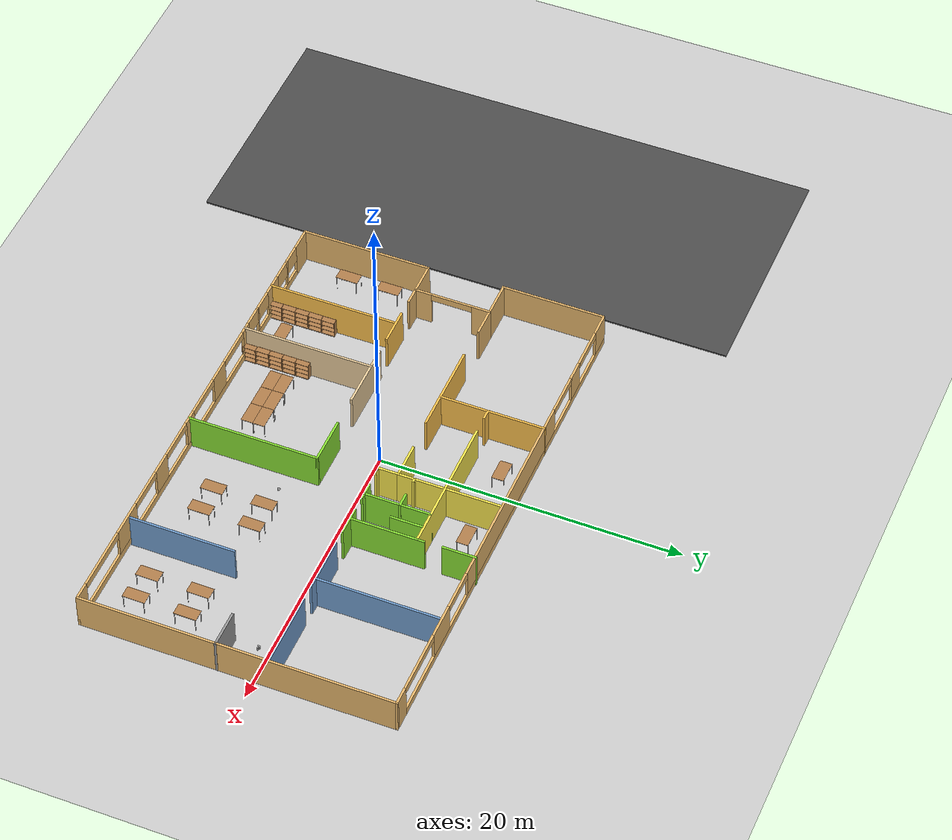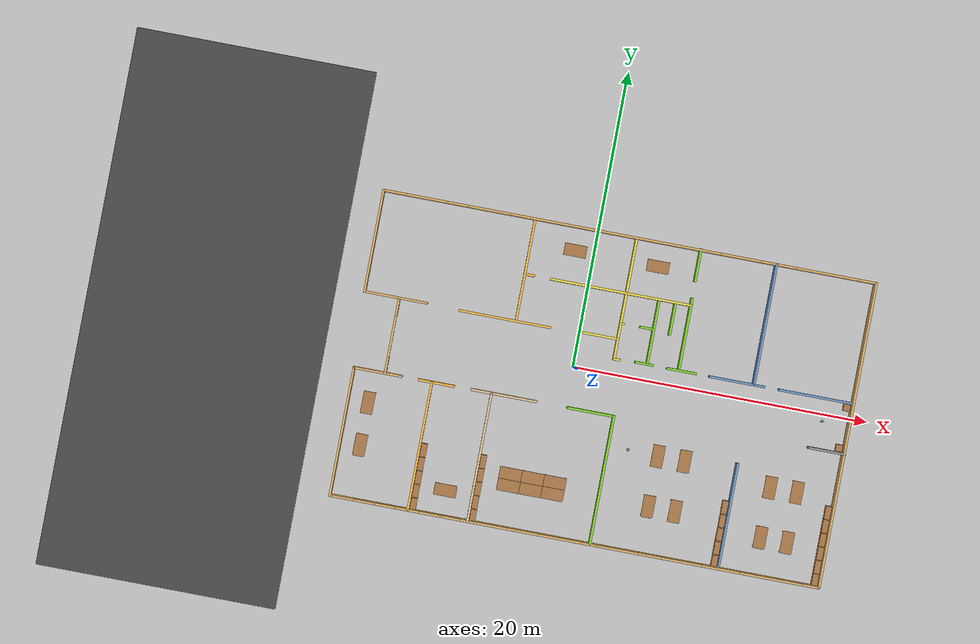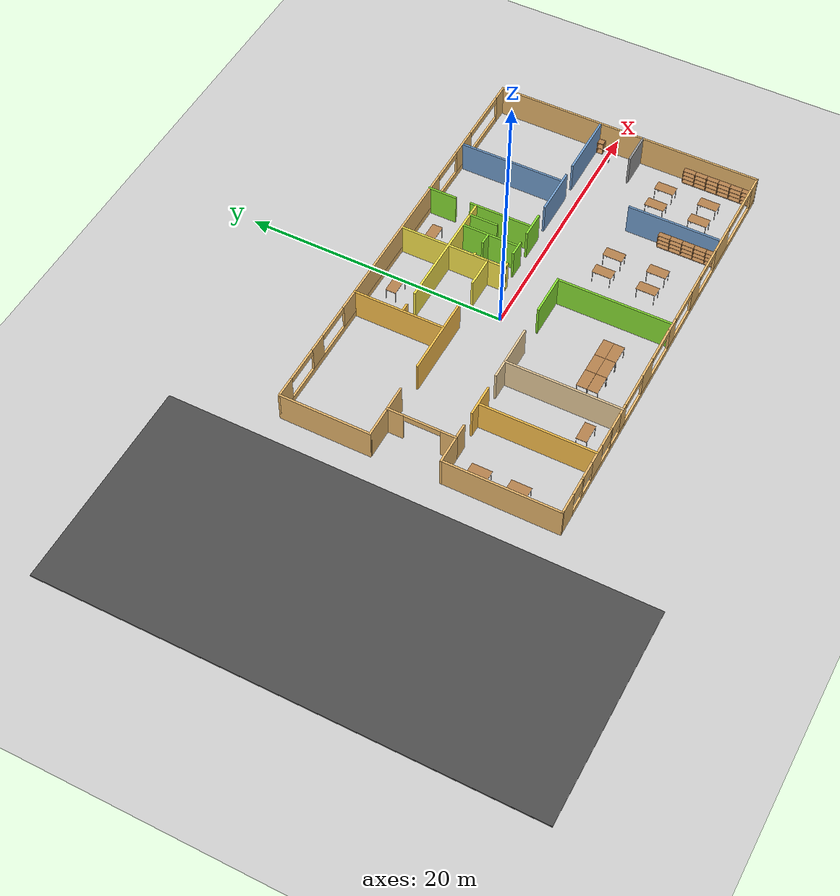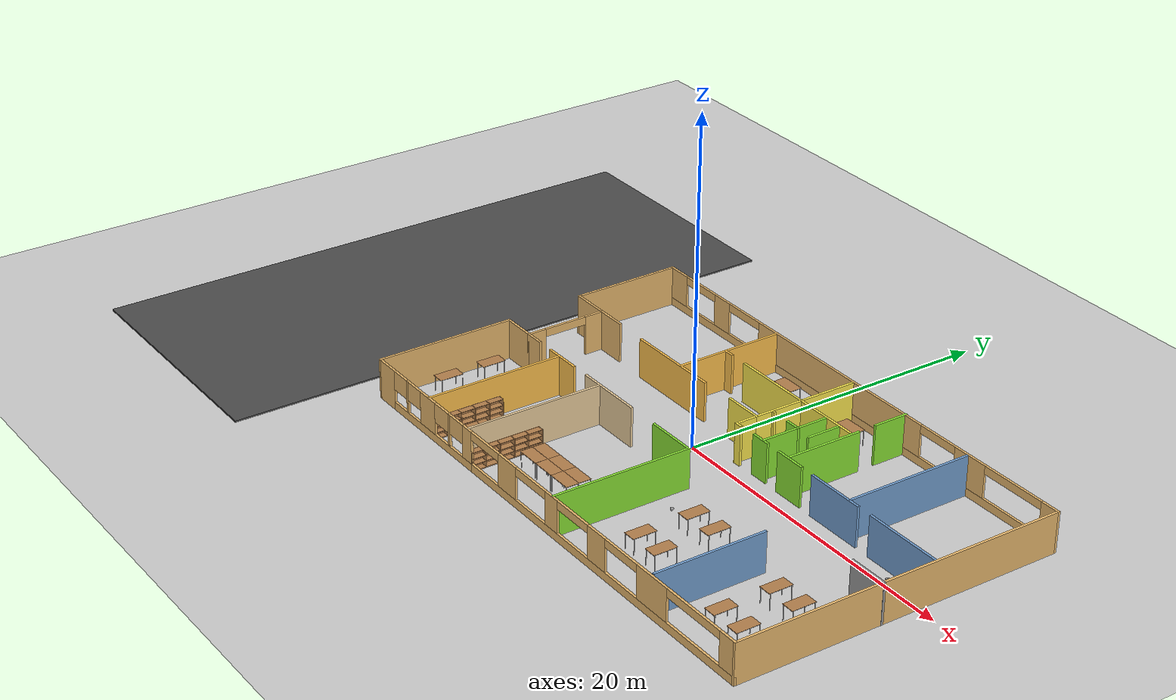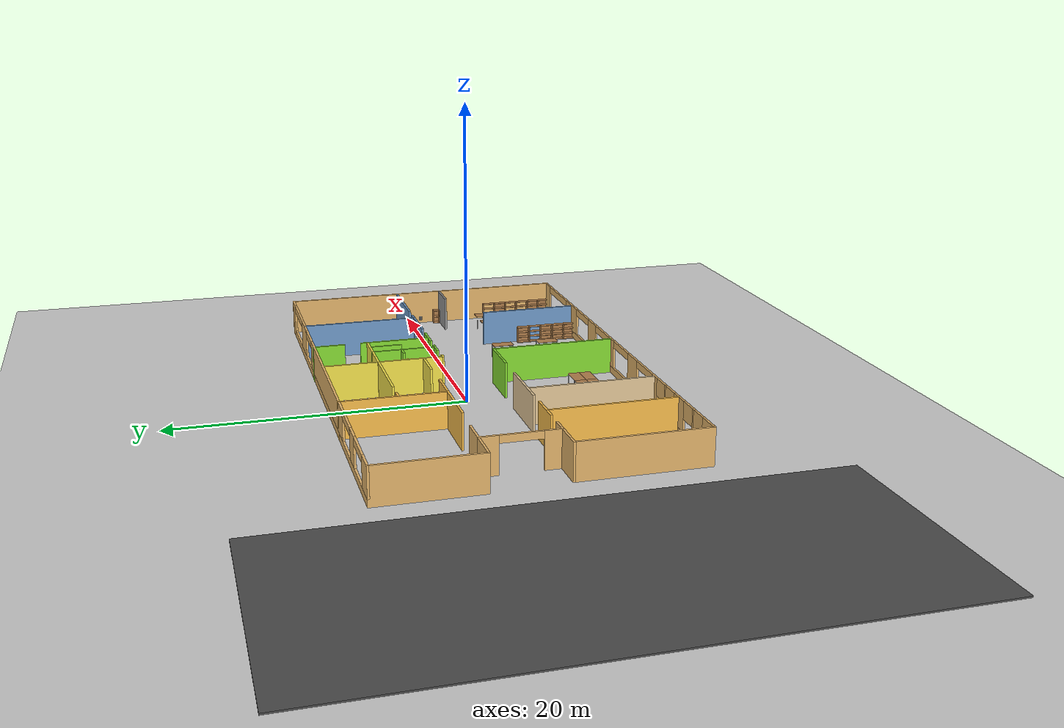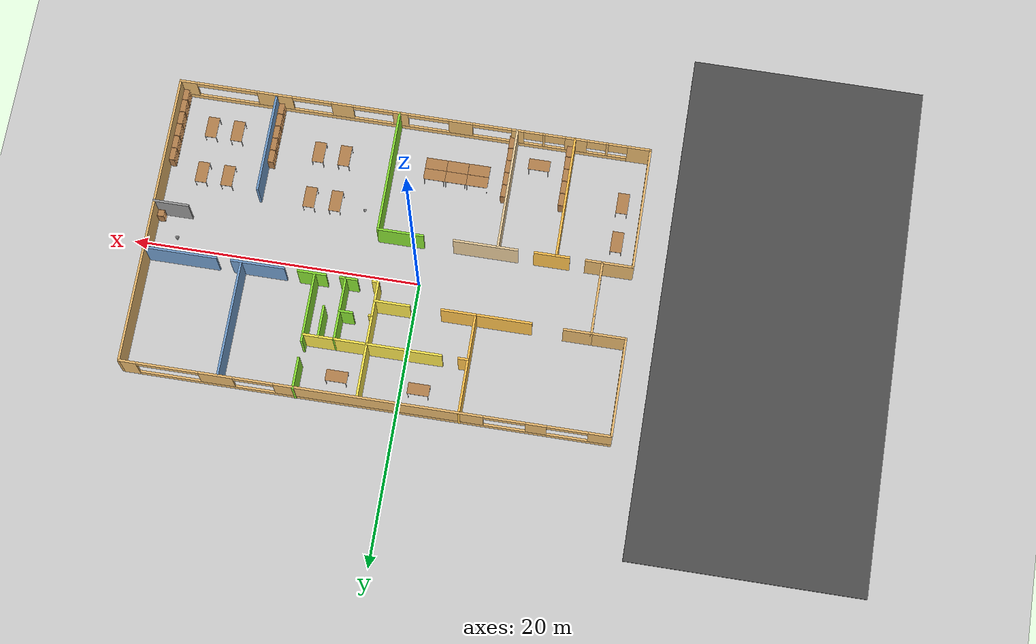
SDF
<sdf version="1.7">
 <world name="default">
  <light name="sun" type="directional">
   <pose>0 0 10 0 -0 0</pose>
   <diffuse>0.8 0.8 0.8 1</diffuse>
   <specular>0.2 0.2 0.2 1</specular>
   <attenuation>
    <range>1000</range>
    <constant>0.9</constant>
    <linear>0.01</linear>
    <quadratic>0.001</quadratic>
   </attenuation>
   <direction>-0.5 0.1 -0.9</direction>
   <spot><inner_angle>0</inner_angle><outer_angle>0</outer_angle><falloff>0</falloff></spot>
  </light>
  <model name="ground_plane">
   <static>1</static>
   <link name="link">
    <collision name="collision">
     <geometry><plane><normal>0 0 1</normal><size>100 100</size></plane></geometry>
     <surface>
      <contact><collide_bitmask>65535</collide_bitmask></contact>
      <friction><ode><mu>100</mu><mu2>50</mu2></ode></friction>
     </surface>
    </collision>
    <visual name="visual">
     <cast_shadows>0</cast_shadows>
     <geometry><plane><normal>0 0 1</normal><size>100 100</size></plane></geometry>
     <material>
      <script><uri>file://media/materials/scripts/gazebo.material</uri><name>Gazebo/Grey</name></script>
     </material>
    </visual>
   </link>
  </model>
  <gravity>0 0 -9.8</gravity>
  <magnetic_field>6e-06 2.3e-05 -4.2e-05</magnetic_field>
  <atmosphere type="adiabatic"/>
  <physics type="ode">
   <max_step_size>0.001</max_step_size>
   <real_time_factor>1</real_time_factor>
   <real_time_update_rate>1000</real_time_update_rate>
  </physics>
  <scene><ambient>0.4 0.4 0.4 1</ambient><background>0.7 0.7 0.7 1</background><shadows>1</shadows></scene>
  <spherical_coordinates>
   <surface_model>EARTH_WGS84</surface_model>
   <latitude_deg>0</latitude_deg>
   <longitude_deg>0</longitude_deg>
   <elevation>0</elevation>
   <heading_deg>0</heading_deg>
  </spherical_coordinates>
  <model name="myNewWorld">
   <pose>2.09066 -1.06842 0 0 -0 0</pose>
   <link name="Wall_0">
    <collision name="Wall_0_Collision">
     <geometry><box><size>8.75 0.15 2.5</size></box></geometry>
     <pose>0 0 1.25 0 -0 0</pose>
    </collision>
    <visual name="Wall_0_Visual">
     <pose>0 0 1.25 0 -0 0</pose>
     <geometry><box><size>8.75 0.15 2.5</size></box></geometry>
     <material>
      <script><uri>file://media/materials/scripts/gazebo.material</uri><name>Gazebo/Grey</name></script>
      <ambient>0.913725 0.72549 0.431373 1</ambient>
     </material>
     <meta><layer>0</layer></meta>
    </visual>
    <pose>-16.4305 -6.02061 0 0 -0 -1.5708</pose>
   </link>
   <link name="Wall_1">
    <pose>0.119547 -10.3206 0 0 -0 0</pose>
    <visual name="Wall_1_Visual_0">
     <pose>-15.7898 0 1.25 0 -0 0</pose>
     <geometry><box><size>1.67032 0.15 2.5</size></box></geometry>
     <material>
      <script><uri>file://media/materials/scripts/gazebo.material</uri><name>Gazebo/Grey</name></script>
      <ambient>0.913725 0.72549 0.431373 1</ambient>
     </material>
     <meta><layer>0</layer></meta>
    </visual>
    <collision name="Wall_1_Collision_0">
     <geometry><box><size>1.67032 0.15 2.5</size></box></geometry>
     <pose>-15.7898 0 1.25 0 -0 0</pose>
    </collision>
    <visual name="Wall_1_Visual_1">
     <pose>-10.8802 0 0.25 0 -0 0</pose>
     <geometry><box><size>8.149 0.15 0.5</size></box></geometry>
     <material>
      <script><uri>file://media/materials/scripts/gazebo.material</uri><name>Gazebo/Grey</name></script>
      <ambient>0.913725 0.72549 0.431373 1</ambient>
     </material>
     <meta><layer>0</layer></meta>
    </visual>
    <collision name="Wall_1_Collision_1">
     <geometry><box><size>8.149 0.15 0.5</size></box></geometry>
     <pose>-10.8802 0 0.25 0 -0 0</pose>
    </collision>
    <visual name="Wall_1_Visual_2">
     <pose>4.90966 0 0.25 0 -0 0</pose>
     <geometry><box><size>23.4307 0.15 0.5</size></box></geometry>
     <material>
      <script><uri>file://media/materials/scripts/gazebo.material</uri><name>Gazebo/Grey</name></script>
      <ambient>0.913725 0.72549 0.431373 1</ambient>
     </material>
     <meta><layer>0</layer></meta>
    </visual>
    <collision name="Wall_1_Collision_2">
     <geometry><box><size>23.4307 0.15 0.5</size></box></geometry>
     <pose>4.90966 0 0.25 0 -0 0</pose>
    </collision>
    <visual name="Wall_1_Visual_3">
     <pose>-3.24471 0 1.5 0 -0 0</pose>
     <geometry><box><size>1.68247 0.15 2</size></box></geometry>
     <material>
      <script><uri>file://media/materials/scripts/gazebo.material</uri><name>Gazebo/Grey</name></script>
      <ambient>0.913725 0.72549 0.431373 1</ambient>
     </material>
     <meta><layer>0</layer></meta>
    </visual>
    <collision name="Wall_1_Collision_3">
     <geometry><box><size>1.68247 0.15 2</size></box></geometry>
     <pose>-3.24471 0 1.5 0 -0 0</pose>
    </collision>
    <visual name="Wall_1_Visual_4">
     <pose>0.991858 0 1.5 0 -0 0</pose>
     <geometry><box><size>1.08666 0.15 2</size></box></geometry>
     <material>
      <script><uri>file://media/materials/scripts/gazebo.material</uri><name>Gazebo/Grey</name></script>
      <ambient>0.913725 0.72549 0.431373 1</ambient>
     </material>
     <meta><layer>0</layer></meta>
    </visual>
    <collision name="Wall_1_Collision_4">
     <geometry><box><size>1.08666 0.15 2</size></box></geometry>
     <pose>0.991858 0 1.5 0 -0 0</pose>
    </collision>
    <visual name="Wall_1_Visual_5">
     <pose>5.09613 0 1.5 0 -0 0</pose>
     <geometry><box><size>1.54989 0.15 2</size></box></geometry>
     <material>
      <script><uri>file://media/materials/scripts/gazebo.material</uri><name>Gazebo/Grey</name></script>
      <ambient>0.913725 0.72549 0.431373 1</ambient>
     </material>
     <meta><layer>0</layer></meta>
    </visual>
    <collision name="Wall_1_Collision_5">
     <geometry><box><size>1.54989 0.15 2</size></box></geometry>
     <pose>5.09613 0 1.5 0 -0 0</pose>
    </collision>
    <visual name="Wall_1_Visual_6">
     <pose>9.87907 0 1.5 0 -0 0</pose>
     <geometry><box><size>2.50998 0.15 2</size></box></geometry>
     <material>
      <script><uri>file://media/materials/scripts/gazebo.material</uri><name>Gazebo/Grey</name></script>
      <ambient>0.913725 0.72549 0.431373 1</ambient>
     </material>
     <meta><layer>0</layer></meta>
    </visual>
    <collision name="Wall_1_Collision_6">
     <geometry><box><size>2.50998 0.15 2</size></box></geometry>
     <pose>9.87907 0 1.5 0 -0 0</pose>
    </collision>
    <visual name="Wall_1_Visual_7">
     <pose>16.017 0 1.5 0 -0 0</pose>
     <geometry><box><size>1.21594 0.15 2</size></box></geometry>
     <material>
      <script><uri>file://media/materials/scripts/gazebo.material</uri><name>Gazebo/Grey</name></script>
      <ambient>0.913725 0.72549 0.431373 1</ambient>
     </material>
     <meta><layer>0</layer></meta>
    </visual>
    <collision name="Wall_1_Collision_7">
     <geometry><box><size>1.21594 0.15 2</size></box></geometry>
     <pose>16.017 0 1.5 0 -0 0</pose>
    </collision>
    <visual name="Wall_1_Visual_8">
     <pose>-13.5437 0 1.5 0 -0 0</pose>
     <geometry><box><size>0.168237 0.15 2</size></box></geometry>
     <material>
      <script><uri>file://media/materials/scripts/gazebo.material</uri><name>Gazebo/Grey</name></script>
      <ambient>0.913725 0.72549 0.431373 1</ambient>
     </material>
     <meta><layer>0</layer></meta>
    </visual>
    <collision name="Wall_1_Collision_8">
     <geometry><box><size>0.168237 0.15 2</size></box></geometry>
     <pose>-13.5437 0 1.5 0 -0 0</pose>
    </collision>
    <visual name="Wall_1_Visual_9">
     <pose>-11.3487 0 1.5 0 -0 0</pose>
     <geometry><box><size>1.53961 0.15 2</size></box></geometry>
     <material>
      <script><uri>file://media/materials/scripts/gazebo.material</uri><name>Gazebo/Grey</name></script>
      <ambient>0.913725 0.72549 0.431373 1</ambient>
     </material>
     <meta><layer>0</layer></meta>
    </visual>
    <collision name="Wall_1_Collision_9">
     <geometry><box><size>1.53961 0.15 2</size></box></geometry>
     <pose>-11.3487 0 1.5 0 -0 0</pose>
    </collision>
    <visual name="Wall_1_Visual_10">
     <pose>-9.10323 0 1.5 0 -0 0</pose>
     <geometry><box><size>0.159865 0.15 2</size></box></geometry>
     <material>
      <script><uri>file://media/materials/scripts/gazebo.material</uri><name>Gazebo/Grey</name></script>
      <ambient>0.913725 0.72549 0.431373 1</ambient>
     </material>
     <meta><layer>0</layer></meta>
    </visual>
    <collision name="Wall_1_Collision_10">
     <geometry><box><size>0.159865 0.15 2</size></box></geometry>
     <pose>-9.10323 0 1.5 0 -0 0</pose>
    </collision>
    <visual name="Wall_1_Visual_11">
     <pose>-7.2497 0 1.5 0 -0 0</pose>
     <geometry><box><size>0.888039 0.15 2</size></box></geometry>
     <material>
      <script><uri>file://media/materials/scripts/gazebo.material</uri><name>Gazebo/Grey</name></script>
      <ambient>0.913725 0.72549 0.431373 1</ambient>
     </material>
     <meta><layer>0</layer></meta>
    </visual>
    <collision name="Wall_1_Collision_11">
     <geometry><box><size>0.888039 0.15 2</size></box></geometry>
     <pose>-7.2497 0 1.5 0 -0 0</pose>
    </collision>
    <visual name="Wall_1_Visual_12">
     <pose>-7.2497 0 1.5 0 -0 0</pose>
     <geometry><box><size>0.888039 0.15 2</size></box></geometry>
     <material>
      <script><uri>file://media/materials/scripts/gazebo.material</uri><name>Gazebo/Grey</name></script>
      <ambient>0.913725 0.72549 0.431373 1</ambient>
     </material>
     <meta><layer>0</layer></meta>
    </visual>
    <collision name="Wall_1_Collision_12">
     <geometry><box><size>0.888039 0.15 2</size></box></geometry>
     <pose>-7.2497 0 1.5 0 -0 0</pose>
    </collision>
    <visual name="Wall_1_Visual_13">
     <pose>-14.2912 0 1.9 0 -0 0</pose>
     <geometry><box><size>1.32689 0.15 1.2</size></box></geometry>
     <material>
      <script><uri>file://media/materials/scripts/gazebo.material</uri><name>Gazebo/Grey</name></script>
      <ambient>0.913725 0.72549 0.431373 1</ambient>
     </material>
     <meta><layer>0</layer></meta>
    </visual>
    <collision name="Wall_1_Collision_13">
     <geometry><box><size>1.32689 0.15 1.2</size></box></geometry>
     <pose>-14.2912 0 1.9 0 -0 0</pose>
    </collision>
    <visual name="Wall_1_Visual_14">
     <pose>-12.789 0 1.9 0 -0 0</pose>
     <geometry><box><size>1.341 0.15 1.2</size></box></geometry>
     <material>
      <script><uri>file://media/materials/scripts/gazebo.material</uri><name>Gazebo/Grey</name></script>
      <ambient>0.913725 0.72549 0.431373 1</ambient>
     </material>
     <meta><layer>0</layer></meta>
    </visual>
    <collision name="Wall_1_Collision_14">
     <geometry><box><size>1.341 0.15 1.2</size></box></geometry>
     <pose>-12.789 0 1.9 0 -0 0</pose>
    </collision>
    <visual name="Wall_1_Visual_15">
     <pose>-9.88105 0 1.9 0 -0 0</pose>
     <geometry><box><size>1.39578 0.15 1.2</size></box></geometry>
     <material>
      <script><uri>file://media/materials/scripts/gazebo.material</uri><name>Gazebo/Grey</name></script>
      <ambient>0.913725 0.72549 0.431373 1</ambient>
     </material>
     <meta><layer>0</layer></meta>
    </visual>
    <collision name="Wall_1_Collision_15">
     <geometry><box><size>1.39578 0.15 1.2</size></box></geometry>
     <pose>-9.88105 0 1.9 0 -0 0</pose>
    </collision>
    <visual name="Wall_1_Visual_16">
     <pose>-8.3585 0 1.9 0 -0 0</pose>
     <geometry><box><size>1.32958 0.15 1.2</size></box></geometry>
     <material>
      <script><uri>file://media/materials/scripts/gazebo.material</uri><name>Gazebo/Grey</name></script>
      <ambient>0.913725 0.72549 0.431373 1</ambient>
     </material>
     <meta><layer>0</layer></meta>
    </visual>
    <collision name="Wall_1_Collision_16">
     <geometry><box><size>1.32958 0.15 1.2</size></box></geometry>
     <pose>-8.3585 0 1.9 0 -0 0</pose>
    </collision>
    <visual name="Wall_1_Visual_17">
     <pose>-0.977472 0 2.25 0 -0 0</pose>
     <geometry><box><size>2.852 0.15 0.5</size></box></geometry>
     <material>
      <script><uri>file://media/materials/scripts/gazebo.material</uri><name>Gazebo/Grey</name></script>
      <ambient>0.913725 0.72549 0.431373 1</ambient>
     </material>
     <meta><layer>0</layer></meta>
    </visual>
    <collision name="Wall_1_Collision_17">
     <geometry><box><size>2.852 0.15 0.5</size></box></geometry>
     <pose>-0.977472 0 2.25 0 -0 0</pose>
    </collision>
    <visual name="Wall_1_Visual_18">
     <pose>2.92819 0 2.25 0 -0 0</pose>
     <geometry><box><size>2.786 0.15 0.5</size></box></geometry>
     <material>
      <script><uri>file://media/materials/scripts/gazebo.material</uri><name>Gazebo/Grey</name></script>
      <ambient>0.913725 0.72549 0.431373 1</ambient>
     </material>
     <meta><layer>0</layer></meta>
    </visual>
    <collision name="Wall_1_Collision_18">
     <geometry><box><size>2.786 0.15 0.5</size></box></geometry>
     <pose>2.92819 0 2.25 0 -0 0</pose>
    </collision>
    <visual name="Wall_1_Visual_19">
     <pose>7.24758 0 2.25 0 -0 0</pose>
     <geometry><box><size>2.753 0.15 0.5</size></box></geometry>
     <material>
      <script><uri>file://media/materials/scripts/gazebo.material</uri><name>Gazebo/Grey</name></script>
      <ambient>0.913725 0.72549 0.431373 1</ambient>
     </material>
     <meta><layer>0</layer></meta>
    </visual>
    <collision name="Wall_1_Collision_19">
     <geometry><box><size>2.753 0.15 0.5</size></box></geometry>
     <pose>7.24758 0 2.25 0 -0 0</pose>
    </collision>
    <visual name="Wall_1_Visual_20">
     <pose>13.2716 0 2.25 0 -0 0</pose>
     <geometry><box><size>4.275 0.15 0.5</size></box></geometry>
     <material>
      <script><uri>file://media/materials/scripts/gazebo.material</uri><name>Gazebo/Grey</name></script>
      <ambient>0.913725 0.72549 0.431373 1</ambient>
     </material>
     <meta><layer>0</layer></meta>
    </visual>
    <collision name="Wall_1_Collision_20">
     <geometry><box><size>4.275 0.15 0.5</size></box></geometry>
     <pose>13.2716 0 2.25 0 -0 0</pose>
    </collision>
    <visual name="Wall_1_Visual_21">
     <pose>-5.44581 0 2.25 0 -0 0</pose>
     <geometry><box><size>2.71973 0.15 0.5</size></box></geometry>
     <material>
      <script><uri>file://media/materials/scripts/gazebo.material</uri><name>Gazebo/Grey</name></script>
      <ambient>0.913725 0.72549 0.431373 1</ambient>
     </material>
     <meta><layer>0</layer></meta>
    </visual>
    <collision name="Wall_1_Collision_21">
     <geometry><box><size>2.71973 0.15 0.5</size></box></geometry>
     <pose>-5.44581 0 2.25 0 -0 0</pose>
    </collision>
    <visual name="Wall_1_Visual_22">
     <pose>-5.44581 0 2.25 0 -0 0</pose>
     <geometry><box><size>2.71973 0.15 0.5</size></box></geometry>
     <material>
      <script><uri>file://media/materials/scripts/gazebo.material</uri><name>Gazebo/Grey</name></script>
      <ambient>0.913725 0.72549 0.431373 1</ambient>
     </material>
     <meta><layer>0</layer></meta>
    </visual>
    <collision name="Wall_1_Collision_22">
     <geometry><box><size>2.71973 0.15 0.5</size></box></geometry>
     <pose>-5.44581 0 2.25 0 -0 0</pose>
    </collision>
   </link>
   <link name="Wall_11">
    <collision name="Wall_11_Collision">
     <geometry><box><size>2.5 0.15 2.5</size></box></geometry>
     <pose>0 0 1.25 0 -0 0</pose>
    </collision>
    <visual name="Wall_11_Visual">
     <pose>0 0 1.25 0 -0 0</pose>
     <geometry><box><size>2.5 0.15 2.5</size></box></geometry>
     <material>
      <script><uri>file://media/materials/scripts/gazebo.material</uri><name>Gazebo/Grey</name></script>
      <ambient>1 0.764706 0.305882 1</ambient>
     </material>
     <meta><layer>0</layer></meta>
    </visual>
    <pose>-10.8599 -1.67429 0 0 -0 0</pose>
   </link>
   <link name="Wall_13">
    <collision name="Wall_13_Collision">
     <geometry><box><size>4.5 0.15 2.5</size></box></geometry>
     <pose>0 0 1.25 0 -0 0</pose>
    </collision>
    <visual name="Wall_13_Visual">
     <pose>0 0 1.25 0 -0 0</pose>
     <geometry><box><size>4.5 0.15 2.5</size></box></geometry>
     <material>
      <script><uri>file://media/materials/scripts/gazebo.material</uri><name>Gazebo/Grey</name></script>
      <ambient>0.921569 0.807843 0.615686 1</ambient>
     </material>
     <meta><layer>0</layer></meta>
    </visual>
    <pose>-6.29523 -1.65724 0 0 -0 0</pose>
   </link>
   <link name="Wall_15">
    <collision name="Wall_15_Collision">
     <geometry><box><size>3.25 0.15 2.5</size></box></geometry>
     <pose>0 0 1.25 0 -0 0</pose>
    </collision>
    <visual name="Wall_15_Visual">
     <pose>0 0 1.25 0 -0 0</pose>
     <geometry><box><size>3.25 0.15 2.5</size></box></geometry>
     <material>
      <script><uri>file://media/materials/scripts/gazebo.material</uri><name>Gazebo/Grey</name></script>
      <ambient>0.541176 0.886275 0.203922 1</ambient>
     </material>
     <meta><layer>0</layer></meta>
    </visual>
    <pose>-0.387876 -1.65724 0 0 -0 0</pose>
   </link>
   <link name="Wall_16">
    <collision name="Wall_16_Collision">
     <geometry><box><size>8.75 0.15 2.5</size></box></geometry>
     <pose>0 0 1.25 0 -0 0</pose>
    </collision>
    <visual name="Wall_16_Visual">
     <pose>0 0 1.25 0 -0 0</pose>
     <geometry><box><size>8.75 0.15 2.5</size></box></geometry>
     <material>
      <script><uri>file://media/materials/scripts/gazebo.material</uri><name>Gazebo/Grey</name></script>
      <ambient>0.541176 0.886275 0.203922 1</ambient>
     </material>
     <meta><layer>0</layer></meta>
    </visual>
    <pose>1.16212 -5.95724 0 0 -0 -1.5708</pose>
   </link>
   <link name="Wall_18">
    <collision name="Wall_18_Collision">
     <geometry><box><size>8.75 0.15 2.5</size></box></geometry>
     <pose>0 0 1.25 0 -0 0</pose>
    </collision>
    <visual name="Wall_18_Visual">
     <pose>0 0 1.25 0 -0 0</pose>
     <geometry><box><size>8.75 0.15 2.5</size></box></geometry>
     <material>
      <script><uri>file://media/materials/scripts/gazebo.material</uri><name>Gazebo/Grey</name></script>
      <ambient>0.921569 0.807843 0.615686 1</ambient>
     </material>
     <meta><layer>0</layer></meta>
    </visual>
    <pose>-7.12178 -6.02056 0 0 -0 1.5708</pose>
   </link>
   <link name="Wall_2">
    <collision name="Wall_2_Collision">
     <geometry><box><size>20.75 0.15 2.5</size></box></geometry>
     <pose>0 0 1.25 0 -0 0</pose>
    </collision>
    <visual name="Wall_2_Visual">
     <pose>0 0 1.25 0 -0 0</pose>
     <geometry><box><size>20.75 0.15 2.5</size></box></geometry>
     <material>
      <script><uri>file://media/materials/scripts/gazebo.material</uri><name>Gazebo/Grey</name></script>
      <ambient>0.913725 0.72549 0.431373 1</ambient>
     </material>
     <meta><layer>0</layer></meta>
    </visual>
    <pose>16.6695 -0.020609 0 0 -0 1.5708</pose>
   </link>
   <link name="Wall_20">
    <collision name="Wall_20_Collision">
     <geometry><box><size>8.75 0.15 2.5</size></box></geometry>
     <pose>0 0 1.25 0 -0 0</pose>
    </collision>
    <visual name="Wall_20_Visual">
     <pose>0 0 1.25 0 -0 0</pose>
     <geometry><box><size>8.75 0.15 2.5</size></box></geometry>
     <material>
      <script><uri>file://media/materials/scripts/gazebo.material</uri><name>Gazebo/Grey</name></script>
      <ambient>1 0.764706 0.305882 1</ambient>
     </material>
     <meta><layer>0</layer></meta>
    </visual>
    <pose>-11.1558 -6.00573 0 0 -0 1.5708</pose>
   </link>
   <link name="Wall_22">
    <collision name="Wall_22_Collision">
     <geometry><box><size>2.5 0.15 2.5</size></box></geometry>
     <pose>0 0 1.25 0 -0 0</pose>
    </collision>
    <visual name="Wall_22_Visual">
     <pose>0 0 1.25 0 -0 0</pose>
     <geometry><box><size>2.5 0.15 2.5</size></box></geometry>
     <material>
      <script><uri>file://media/materials/scripts/gazebo.material</uri><name>Gazebo/Grey</name></script>
      <ambient>1 1 1 1</ambient>
     </material>
     <meta><layer>0</layer></meta>
    </visual>
    <pose>15.5055 -1.28166 0 0 -0 3.14159</pose>
   </link>
   <link name="Wall_24">
    <collision name="Wall_24_Collision">
     <geometry><box><size>5 0.15 2.5</size></box></geometry>
     <pose>0 0 1.25 0 -0 0</pose>
    </collision>
    <visual name="Wall_24_Visual">
     <pose>0 0 1.25 0 -0 0</pose>
     <geometry><box><size>5 0.15 2.5</size></box></geometry>
     <material>
      <script><uri>file://media/materials/scripts/gazebo.material</uri><name>Gazebo/Grey</name></script>
      <ambient>0.447059 0.623529 0.811765 1</ambient>
     </material>
     <meta><layer>0</layer></meta>
    </visual>
    <pose>14.1205 2.12433 0 0 -0 0</pose>
   </link>
   <link name="Wall_26">
    <collision name="Wall_26_Collision">
     <geometry><box><size>3.75 0.15 2.5</size></box></geometry>
     <pose>0 0 1.25 0 -0 0</pose>
    </collision>
    <visual name="Wall_26_Visual">
     <pose>0 0 1.25 0 -0 0</pose>
     <geometry><box><size>3.75 0.15 2.5</size></box></geometry>
     <material>
      <script><uri>file://media/materials/scripts/gazebo.material</uri><name>Gazebo/Grey</name></script>
      <ambient>0.447059 0.623529 0.811765 1</ambient>
     </material>
     <meta><layer>0</layer></meta>
    </visual>
    <pose>8.79119 2.12848 0 0 -0 0</pose>
   </link>
   <link name="Wall_28">
    <collision name="Wall_28_Collision">
     <geometry><box><size>2 0.15 2.5</size></box></geometry>
     <pose>0 0 1.25 0 -0 0</pose>
    </collision>
    <visual name="Wall_28_Visual">
     <pose>0 0 1.25 0 -0 0</pose>
     <geometry><box><size>2 0.15 2.5</size></box></geometry>
     <material>
      <script><uri>file://media/materials/scripts/gazebo.material</uri><name>Gazebo/Grey</name></script>
      <ambient>0.541176 0.886275 0.203922 1</ambient>
     </material>
     <meta><layer>0</layer></meta>
    </visual>
    <pose>5.03377 2.14554 0 0 -0 0</pose>
   </link>
   <link name="Wall_3">
    <pose>-0.005453 10.2794 0 0 -0 3.14159</pose>
    <visual name="Wall_3_Visual_0">
     <pose>-16.1255 0 1.25 0 -0 0</pose>
     <geometry><box><size>1.24899 0.15 2.5</size></box></geometry>
     <material>
      <script><uri>file://media/materials/scripts/gazebo.material</uri><name>Gazebo/Grey</name></script>
      <ambient>0.913725 0.72549 0.431373 1</ambient>
     </material>
     <meta><layer>0</layer></meta>
    </visual>
    <collision name="Wall_3_Collision_0">
     <geometry><box><size>1.24899 0.15 2.5</size></box></geometry>
     <pose>-16.1255 0 1.25 0 -0 0</pose>
    </collision>
    <visual name="Wall_3_Visual_1">
     <pose>0.624493 0 0.25 0 -0 0</pose>
     <geometry><box><size>32.251 0.15 0.5</size></box></geometry>
     <material>
      <script><uri>file://media/materials/scripts/gazebo.material</uri><name>Gazebo/Grey</name></script>
      <ambient>0.913725 0.72549 0.431373 1</ambient>
     </material>
     <meta><layer>0</layer></meta>
    </visual>
    <collision name="Wall_3_Collision_1">
     <geometry><box><size>32.251 0.15 0.5</size></box></geometry>
     <pose>0.624493 0 0.25 0 -0 0</pose>
    </collision>
    <visual name="Wall_3_Visual_2">
     <pose>-10.0868 0 1.5 0 -0 0</pose>
     <geometry><box><size>2.34444 0.15 2</size></box></geometry>
     <material>
      <script><uri>file://media/materials/scripts/gazebo.material</uri><name>Gazebo/Grey</name></script>
      <ambient>0.913725 0.72549 0.431373 1</ambient>
     </material>
     <meta><layer>0</layer></meta>
    </visual>
    <collision name="Wall_3_Collision_2">
     <geometry><box><size>2.34444 0.15 2</size></box></geometry>
     <pose>-10.0868 0 1.5 0 -0 0</pose>
    </collision>
    <visual name="Wall_3_Visual_3">
     <pose>0.951811 0 1.5 0 -0 0</pose>
     <geometry><box><size>14.2268 0.15 2</size></box></geometry>
     <material>
      <script><uri>file://media/materials/scripts/gazebo.material</uri><name>Gazebo/Grey</name></script>
      <ambient>0.913725 0.72549 0.431373 1</ambient>
     </material>
     <meta><layer>0</layer></meta>
    </visual>
    <collision name="Wall_3_Collision_3">
     <geometry><box><size>14.2268 0.15 2</size></box></geometry>
     <pose>0.951811 0 1.5 0 -0 0</pose>
    </collision>
    <visual name="Wall_3_Visual_4">
     <pose>11.6261 0 1.5 0 -0 0</pose>
     <geometry><box><size>1.41759 0.15 2</size></box></geometry>
     <material>
      <script><uri>file://media/materials/scripts/gazebo.material</uri><name>Gazebo/Grey</name></script>
      <ambient>0.913725 0.72549 0.431373 1</ambient>
     </material>
     <meta><layer>0</layer></meta>
    </visual>
    <collision name="Wall_3_Collision_4">
     <geometry><box><size>1.41759 0.15 2</size></box></geometry>
     <pose>11.6261 0 1.5 0 -0 0</pose>
    </collision>
    <visual name="Wall_3_Visual_5">
     <pose>15.9355 0 1.5 0 -0 0</pose>
     <geometry><box><size>1.62909 0.15 2</size></box></geometry>
     <material>
      <script><uri>file://media/materials/scripts/gazebo.material</uri><name>Gazebo/Grey</name></script>
      <ambient>0.913725 0.72549 0.431373 1</ambient>
     </material>
     <meta><layer>0</layer></meta>
    </visual>
    <collision name="Wall_3_Collision_5">
     <geometry><box><size>1.62909 0.15 2</size></box></geometry>
     <pose>15.9355 0 1.5 0 -0 0</pose>
    </collision>
    <visual name="Wall_3_Visual_6">
     <pose>-13.38 0 2.25 0 -0 0</pose>
     <geometry><box><size>4.242 0.15 0.5</size></box></geometry>
     <material>
      <script><uri>file://media/materials/scripts/gazebo.material</uri><name>Gazebo/Grey</name></script>
      <ambient>0.913725 0.72549 0.431373 1</ambient>
     </material>
     <meta><layer>0</layer></meta>
    </visual>
    <collision name="Wall_3_Collision_6">
     <geometry><box><size>4.242 0.15 0.5</size></box></geometry>
     <pose>-13.38 0 2.25 0 -0 0</pose>
    </collision>
    <visual name="Wall_3_Visual_7">
     <pose>-7.53808 0 2.25 0 -0 0</pose>
     <geometry><box><size>2.753 0.15 0.5</size></box></geometry>
     <material>
      <script><uri>file://media/materials/scripts/gazebo.material</uri><name>Gazebo/Grey</name></script>
      <ambient>0.913725 0.72549 0.431373 1</ambient>
     </material>
     <meta><layer>0</layer></meta>
    </visual>
    <collision name="Wall_3_Collision_7">
     <geometry><box><size>2.753 0.15 0.5</size></box></geometry>
     <pose>-7.53808 0 2.25 0 -0 0</pose>
    </collision>
    <visual name="Wall_3_Visual_8">
     <pose>9.49126 0 2.25 0 -0 0</pose>
     <geometry><box><size>2.85213 0.15 0.5</size></box></geometry>
     <material>
      <script><uri>file://media/materials/scripts/gazebo.material</uri><name>Gazebo/Grey</name></script>
      <ambient>0.913725 0.72549 0.431373 1</ambient>
     </material>
     <meta><layer>0</layer></meta>
    </visual>
    <collision name="Wall_3_Collision_8">
     <geometry><box><size>2.85213 0.15 0.5</size></box></geometry>
     <pose>9.49126 0 2.25 0 -0 0</pose>
    </collision>
    <visual name="Wall_3_Visual_9">
     <pose>13.7279 0 2.25 0 -0 0</pose>
     <geometry><box><size>2.786 0.15 0.5</size></box></geometry>
     <material>
      <script><uri>file://media/materials/scripts/gazebo.material</uri><name>Gazebo/Grey</name></script>
      <ambient>0.913725 0.72549 0.431373 1</ambient>
     </material>
     <meta><layer>0</layer></meta>
    </visual>
    <collision name="Wall_3_Collision_9">
     <geometry><box><size>2.786 0.15 0.5</size></box></geometry>
     <pose>13.7279 0 2.25 0 -0 0</pose>
    </collision>
   </link>
   <link name="Wall_30">
    <collision name="Wall_30_Collision">
     <geometry><box><size>1.25 0.15 2.5</size></box></geometry>
     <pose>0 0 1.25 0 -0 0</pose>
    </collision>
    <visual name="Wall_30_Visual">
     <pose>0 0 1.25 0 -0 0</pose>
     <geometry><box><size>1.25 0.15 2.5</size></box></geometry>
     <material>
      <script><uri>file://media/materials/scripts/gazebo.material</uri><name>Gazebo/Grey</name></script>
      <ambient>0.541176 0.886275 0.203922 1</ambient>
     </material>
     <meta><layer>0</layer></meta>
    </visual>
    <pose>2.49269 2.1626 0 0 -0 0</pose>
   </link>
   <link name="Wall_32">
    <collision name="Wall_32_Collision">
     <geometry><box><size>0.5 0.15 2.5</size></box></geometry>
     <pose>0 0 1.25 0 -0 0</pose>
    </collision>
    <visual name="Wall_32_Visual">
     <pose>0 0 1.25 0 -0 0</pose>
     <geometry><box><size>0.5 0.15 2.5</size></box></geometry>
     <material>
      <script><uri>file://media/materials/scripts/gazebo.material</uri><name>Gazebo/Grey</name></script>
      <ambient>0.988235 0.913725 0.309804 1</ambient>
     </material>
     <meta><layer>0</layer></meta>
    </visual>
    <pose>0.642012 2.09437 0 0 -0 3.14159</pose>
   </link>
   <link name="Wall_33">
    <collision name="Wall_33_Collision">
     <geometry><box><size>1.5 0.15 2.5</size></box></geometry>
     <pose>0 0 1.25 0 -0 0</pose>
    </collision>
    <visual name="Wall_33_Visual">
     <pose>0 0 1.25 0 -0 0</pose>
     <geometry><box><size>1.5 0.15 2.5</size></box></geometry>
     <material>
      <script><uri>file://media/materials/scripts/gazebo.material</uri><name>Gazebo/Grey</name></script>
      <ambient>0.988235 0.913725 0.309804 1</ambient>
     </material>
     <meta><layer>0</layer></meta>
    </visual>
    <pose>0.467012 2.76937 0 0 -0 1.5708</pose>
   </link>
   <link name="Wall_34">
    <collision name="Wall_34_Collision">
     <geometry><box><size>2.5 0.15 2.5</size></box></geometry>
     <pose>0 0 1.25 0 -0 0</pose>
    </collision>
    <visual name="Wall_34_Visual">
     <pose>0 0 1.25 0 -0 0</pose>
     <geometry><box><size>2.5 0.15 2.5</size></box></geometry>
     <material>
      <script><uri>file://media/materials/scripts/gazebo.material</uri><name>Gazebo/Grey</name></script>
      <ambient>0.988235 0.913725 0.309804 1</ambient>
     </material>
     <meta><layer>0</layer></meta>
    </visual>
    <pose>-0.707988 3.44437 0 0 -0 3.14159</pose>
   </link>
   <link name="Wall_36">
    <collision name="Wall_36_Collision">
     <geometry><box><size>6.25 0.15 2.5</size></box></geometry>
     <pose>0 0 1.25 0 -0 0</pose>
    </collision>
    <visual name="Wall_36_Visual">
     <pose>0 0 1.25 0 -0 0</pose>
     <geometry><box><size>6.25 0.15 2.5</size></box></geometry>
     <material>
      <script><uri>file://media/materials/scripts/gazebo.material</uri><name>Gazebo/Grey</name></script>
      <ambient>1 0.764706 0.305882 1</ambient>
     </material>
     <meta><layer>0</layer></meta>
    </visual>
    <pose>-7.1621 3.3565 0 0 -0 3.14159</pose>
   </link>
   <link name="Wall_38">
    <collision name="Wall_38_Collision">
     <geometry><box><size>2 0.15 2.5</size></box></geometry>
     <pose>0 0 1.25 0 -0 0</pose>
    </collision>
    <visual name="Wall_38_Visual">
     <pose>0 0 1.25 0 -0 0</pose>
     <geometry><box><size>2 0.15 2.5</size></box></geometry>
     <material>
      <script><uri>file://media/materials/scripts/gazebo.material</uri><name>Gazebo/Grey</name></script>
      <ambient>0.913725 0.72549 0.431373 1</ambient>
     </material>
     <meta><layer>0</layer></meta>
    </visual>
    <pose>-13.4055 3.42939 0 0 -0 3.14159</pose>
   </link>
   <link name="Wall_4">
    <collision name="Wall_4_Collision">
     <geometry><box><size>7 0.15 2.5</size></box></geometry>
     <pose>0 0 1.25 0 -0 0</pose>
    </collision>
    <visual name="Wall_4_Visual">
     <pose>0 0 1.25 0 -0 0</pose>
     <geometry><box><size>7 0.15 2.5</size></box></geometry>
     <material>
      <script><uri>file://media/materials/scripts/gazebo.material</uri><name>Gazebo/Grey</name></script>
      <ambient>0.913725 0.72549 0.431373 1</ambient>
     </material>
     <meta><layer>0</layer></meta>
    </visual>
    <pose>-16.6805 6.85439 0 0 -0 -1.5708</pose>
   </link>
   <link name="Wall_40">
    <collision name="Wall_40_Collision">
     <geometry><box><size>8.25 0.15 2.5</size></box></geometry>
     <pose>0 0 1.25 0 -0 0</pose>
    </collision>
    <visual name="Wall_40_Visual">
     <pose>0 0 1.25 0 -0 0</pose>
     <geometry><box><size>8.25 0.15 2.5</size></box></geometry>
     <material>
      <script><uri>file://media/materials/scripts/gazebo.material</uri><name>Gazebo/Grey</name></script>
      <ambient>0.447059 0.623529 0.811765 1</ambient>
     </material>
     <meta><layer>0</layer></meta>
    </visual>
    <pose>9.92596 6.20216 0 0 -0 1.5708</pose>
   </link>
   <link name="Wall_42">
    <collision name="Wall_42_Collision">
     <geometry><box><size>2.25 0.15 2.5</size></box></geometry>
     <pose>0 0 1.25 0 -0 0</pose>
    </collision>
    <visual name="Wall_42_Visual">
     <pose>0 0 1.25 0 -0 0</pose>
     <geometry><box><size>2.25 0.15 2.5</size></box></geometry>
     <material>
      <script><uri>file://media/materials/scripts/gazebo.material</uri><name>Gazebo/Grey</name></script>
      <ambient>0.541176 0.886275 0.203922 1</ambient>
     </material>
     <meta><layer>0</layer></meta>
    </visual>
    <pose>4.80188 9.27061 0 0 -0 -1.5708</pose>
   </link>
   <link name="Wall_44">
    <collision name="Wall_44_Collision">
     <geometry><box><size>4.85 0.15 2.5</size></box></geometry>
     <pose>0 0 1.25 0 -0 0</pose>
    </collision>
    <visual name="Wall_44_Visual">
     <pose>0 0 1.25 0 -0 0</pose>
     <geometry><box><size>4.85 0.15 2.5</size></box></geometry>
     <material>
      <script><uri>file://media/materials/scripts/gazebo.material</uri><name>Gazebo/Grey</name></script>
      <ambient>0.541176 0.886275 0.203922 1</ambient>
     </material>
     <meta><layer>0</layer></meta>
    </visual>
    <pose>4.83533 4.62528 0 0 -0 -1.5708</pose>
   </link>
   <link name="Wall_46">
    <collision name="Wall_46_Collision">
     <geometry><box><size>9.5 0.15 2.5</size></box></geometry>
     <pose>0 0 1.25 0 -0 0</pose>
    </collision>
    <visual name="Wall_46_Visual">
     <pose>0 0 1.25 0 -0 0</pose>
     <geometry><box><size>9.5 0.15 2.5</size></box></geometry>
     <material>
      <script><uri>file://media/materials/scripts/gazebo.material</uri><name>Gazebo/Grey</name></script>
      <ambient>0.988235 0.913725 0.309804 1</ambient>
     </material>
     <meta><layer>0</layer></meta>
    </visual>
    <pose>0.076498 6.54038 0 0 -0 0</pose>
   </link>
   <link name="Wall_48">
    <collision name="Wall_48_Collision">
     <geometry><box><size>4.5 0.15 2.5</size></box></geometry>
     <pose>0 0 1.25 0 -0 0</pose>
    </collision>
    <visual name="Wall_48_Visual">
     <pose>0 0 1.25 0 -0 0</pose>
     <geometry><box><size>4.5 0.15 2.5</size></box></geometry>
     <material>
      <script><uri>file://media/materials/scripts/gazebo.material</uri><name>Gazebo/Grey</name></script>
      <ambient>0.541176 0.886275 0.203922 1</ambient>
     </material>
     <meta><layer>0</layer></meta>
    </visual>
    <pose>2.69432 4.36538 0 0 -0 -1.5708</pose>
   </link>
   <link name="Wall_5">
    <collision name="Wall_5_Collision">
     <geometry><box><size>2.5 0.15 2.5</size></box></geometry>
     <pose>0 0 1.25 0 -0 0</pose>
    </collision>
    <visual name="Wall_5_Visual">
     <pose>0 0 1.25 0 -0 0</pose>
     <geometry><box><size>2.5 0.15 2.5</size></box></geometry>
     <material>
      <script><uri>file://media/materials/scripts/gazebo.material</uri><name>Gazebo/Grey</name></script>
      <ambient>0.913725 0.72549 0.431373 1</ambient>
     </material>
     <meta><layer>0</layer></meta>
    </visual>
    <pose>-15.5055 3.42939 0 0 -0 0</pose>
   </link>
   <link name="Wall_51">
    <collision name="Wall_51_Collision">
     <geometry><box><size>3.25 0.15 2.5</size></box></geometry>
     <pose>0 0 1.25 0 -0 0</pose>
    </collision>
    <visual name="Wall_51_Visual">
     <pose>0 0 1.25 0 -0 0</pose>
     <geometry><box><size>3.25 0.15 2.5</size></box></geometry>
     <material>
      <script><uri>file://media/materials/scripts/gazebo.material</uri><name>Gazebo/Grey</name></script>
      <ambient>0.988235 0.913725 0.309804 1</ambient>
     </material>
     <meta><layer>0</layer></meta>
    </visual>
    <pose>0.467012 4.99437 0 0 -0 1.5708</pose>
   </link>
   <link name="Wall_53">
    <collision name="Wall_53_Collision">
     <geometry><box><size>0.25 0.15 2.5</size></box></geometry>
     <pose>0 0 1.25 0 -0 0</pose>
    </collision>
    <visual name="Wall_53_Visual">
     <pose>0 0 1.25 0 -0 0</pose>
     <geometry><box><size>0.25 0.15 2.5</size></box></geometry>
     <material>
      <script><uri>file://media/materials/scripts/gazebo.material</uri><name>Gazebo/Grey</name></script>
      <ambient>0.988235 0.913725 0.309804 1</ambient>
     </material>
     <meta><layer>0</layer></meta>
    </visual>
    <pose>0.58832 4.51646 0 0 -0 3.14159</pose>
   </link>
   <link name="Wall_55">
    <collision name="Wall_55_Collision">
     <geometry><box><size>1 0.15 2.5</size></box></geometry>
     <pose>0 0 1.25 0 -0 0</pose>
    </collision>
    <visual name="Wall_55_Visual">
     <pose>0 0 1.25 0 -0 0</pose>
     <geometry><box><size>1 0.15 2.5</size></box></geometry>
     <material>
      <script><uri>file://media/materials/scripts/gazebo.material</uri><name>Gazebo/Grey</name></script>
      <ambient>0.541176 0.886275 0.203922 1</ambient>
     </material>
     <meta><layer>0</layer></meta>
    </visual>
    <pose>2.27316 4.51858 0 0 -0 0</pose>
   </link>
   <link name="Wall_57">
    <collision name="Wall_57_Collision">
     <geometry><box><size>2.25 0.15 2.5</size></box></geometry>
     <pose>0 0 1.25 0 -0 0</pose>
    </collision>
    <visual name="Wall_57_Visual">
     <pose>0 0 1.25 0 -0 0</pose>
     <geometry><box><size>2.25 0.15 2.5</size></box></geometry>
     <material>
      <script><uri>file://media/materials/scripts/gazebo.material</uri><name>Gazebo/Grey</name></script>
      <ambient>0.541176 0.886275 0.203922 1</ambient>
     </material>
     <meta><layer>0</layer></meta>
    </visual>
    <pose>3.7964 5.44298 0 0 -0 -1.5708</pose>
   </link>
   <link name="Wall_59">
    <collision name="Wall_59_Collision">
     <geometry><box><size>7 0.15 2.5</size></box></geometry>
     <pose>0 0 1.25 0 -0 0</pose>
    </collision>
    <visual name="Wall_59_Visual">
     <pose>0 0 1.25 0 -0 0</pose>
     <geometry><box><size>7 0.15 2.5</size></box></geometry>
     <material>
      <script><uri>file://media/materials/scripts/gazebo.material</uri><name>Gazebo/Grey</name></script>
      <ambient>1 0.764706 0.305882 1</ambient>
     </material>
     <meta><layer>0</layer></meta>
    </visual>
    <pose>-6.41664 6.86535 0 0 -0 -1.5708</pose>
   </link>
   <link name="Wall_6">
    <pose>-14.3305 0.879391 0 0 -0 -1.5708</pose>
    <visual name="Wall_6_Visual_0">
     <pose>-1.97877 0 1.25 0 -0 0</pose>
     <geometry><box><size>1.29246 0.15 2.5</size></box></geometry>
     <material>
      <script><uri>file://media/materials/scripts/gazebo.material</uri><name>Gazebo/Grey</name></script>
      <ambient>0.913725 0.72549 0.431373 1</ambient>
     </material>
     <meta><layer>0</layer></meta>
    </visual>
    <collision name="Wall_6_Collision_0">
     <geometry><box><size>1.29246 0.15 2.5</size></box></geometry>
     <pose>-1.97877 0 1.25 0 -0 0</pose>
    </collision>
    <visual name="Wall_6_Visual_1">
     <pose>2.023 0 1.25 0 -0 0</pose>
     <geometry><box><size>1.204 0.15 2.5</size></box></geometry>
     <material>
      <script><uri>file://media/materials/scripts/gazebo.material</uri><name>Gazebo/Grey</name></script>
      <ambient>0.913725 0.72549 0.431373 1</ambient>
     </material>
     <meta><layer>0</layer></meta>
    </visual>
    <collision name="Wall_6_Collision_1">
     <geometry><box><size>1.204 0.15 2.5</size></box></geometry>
     <pose>2.023 0 1.25 0 -0 0</pose>
    </collision>
    <visual name="Wall_6_Visual_2">
     <pose>0.044229 0 2.25 0 -0 0</pose>
     <geometry><box><size>2.75353 0.15 0.5</size></box></geometry>
     <material>
      <script><uri>file://media/materials/scripts/gazebo.material</uri><name>Gazebo/Grey</name></script>
      <ambient>0.913725 0.72549 0.431373 1</ambient>
     </material>
     <meta><layer>0</layer></meta>
    </visual>
    <collision name="Wall_6_Collision_2">
     <geometry><box><size>2.75353 0.15 0.5</size></box></geometry>
     <pose>0.044229 0 2.25 0 -0 0</pose>
    </collision>
   </link>
   <link name="Wall_61">
    <collision name="Wall_61_Collision">
     <geometry><box><size>0.75 0.15 2.5</size></box></geometry>
     <pose>0 0 1.25 0 -0 0</pose>
    </collision>
    <visual name="Wall_61_Visual">
     <pose>0 0 1.25 0 -0 0</pose>
     <geometry><box><size>0.75 0.15 2.5</size></box></geometry>
     <material>
      <script><uri>file://media/materials/scripts/gazebo.material</uri><name>Gazebo/Grey</name></script>
      <ambient>1 0.764706 0.305882 1</ambient>
     </material>
     <meta><layer>0</layer></meta>
    </visual>
    <pose>-6.11236 6.54283 0 0 -0 3.14159</pose>
   </link>
   <link name="Wall_63">
    <collision name="Wall_63_Collision">
     <geometry><box><size>3.75 0.15 2.5</size></box></geometry>
     <pose>0 0 1.25 0 -0 0</pose>
    </collision>
    <visual name="Wall_63_Visual">
     <pose>0 0 1.25 0 -0 0</pose>
     <geometry><box><size>3.75 0.15 2.5</size></box></geometry>
     <material>
      <script><uri>file://media/materials/scripts/gazebo.material</uri><name>Gazebo/Grey</name></script>
      <ambient>0.988235 0.913725 0.309804 1</ambient>
     </material>
     <meta><layer>0</layer></meta>
    </visual>
    <pose>0.467012 8.34437 0 0 -0 1.5708</pose>
   </link>
   <link name="Wall_65">
    <collision name="Wall_65_Collision">
     <geometry><box><size>7 0.15 2.5</size></box></geometry>
     <pose>0 0 1.25 0 -0 0</pose>
    </collision>
    <visual name="Wall_65_Visual">
     <pose>0 0 1.25 0 -0 0</pose>
     <geometry><box><size>7 0.15 2.5</size></box></geometry>
     <material>
      <script><uri>file://media/materials/scripts/gazebo.material</uri><name>Gazebo/Grey</name></script>
      <ambient>0.447059 0.623529 0.811765 1</ambient>
     </material>
     <meta><layer>0</layer></meta>
    </visual>
    <pose>9.852 -6.67855 0 0 -0 1.5708</pose>
   </link>
   <link name="Wall_7">
    <collision name="Wall_7_Collision">
     <geometry><box><size>2.25 0.15 2.5</size></box></geometry>
     <pose>0 0 1.25 0 -0 0</pose>
    </collision>
    <visual name="Wall_7_Visual">
     <pose>0 0 1.25 0 -0 0</pose>
     <geometry><box><size>2.25 0.15 2.5</size></box></geometry>
     <material>
      <script><uri>file://media/materials/scripts/gazebo.material</uri><name>Gazebo/Grey</name></script>
      <ambient>0.913725 0.72549 0.431373 1</ambient>
     </material>
     <meta><layer>0</layer></meta>
    </visual>
    <pose>-15.3805 -1.67061 0 0 -0 3.14159</pose>
   </link>
   <link name="Wall_9">
    <collision name="Wall_9_Collision">
     <geometry><box><size>1.25 0.15 2.5</size></box></geometry>
     <pose>0 0 1.25 0 -0 0</pose>
    </collision>
    <visual name="Wall_9_Visual">
     <pose>0 0 1.25 0 -0 0</pose>
     <geometry><box><size>1.25 0.15 2.5</size></box></geometry>
     <material>
      <script><uri>file://media/materials/scripts/gazebo.material</uri><name>Gazebo/Grey</name></script>
      <ambient>0.913725 0.72549 0.431373 1</ambient>
     </material>
     <meta><layer>0</layer></meta>
    </visual>
    <pose>-13.7805 -1.67061 0 0 -0 0</pose>
   </link>
   <static>1</static>
  </model>
  <model name="myBall">
   <link name="link_0">
    <inertial>
     <mass>10</mass>
     <inertia><ixx>1</ixx><ixy>0</ixy><ixz>0</ixz><iyy>1</iyy><iyz>0</iyz><izz>1</izz></inertia>
    </inertial>
    <visual name="visual">
     <geometry><sphere><radius>0.1</radius></sphere></geometry>
     <material>
      <lighting>1</lighting>
      <script><uri>file://media/materials/scripts/gazebo.material</uri><name>Gazebo/Grey</name></script>
      <shader type="pixel"><normal_map>__default__</normal_map></shader>
      <ambient>1 1 1 1</ambient>
      <diffuse>1 1 1 1</diffuse>
      <specular>1 1 1 1</specular>
      <emissive>1 1 1 1</emissive>
     </material>
    </visual>
    <collision name="collision">
     <geometry><sphere><radius>0.1</radius></sphere></geometry>
     <surface>
      <friction>
       <ode><mu>1</mu><mu2>1</mu2><fdir1>0 0 0</fdir1><slip1>0</slip1><slip2>0</slip2></ode>
       <torsional>
        <coefficient>1</coefficient>
        <patch_radius>0</patch_radius>
        <surface_radius>0</surface_radius>
        <use_patch_radius>1</use_patch_radius>
        <ode><slip>0</slip></ode>
       </torsional>
      </friction>
      <bounce><restitution_coefficient>0</restitution_coefficient><threshold>1e+06</threshold></bounce>
      <contact>
       <collide_without_contact>0</collide_without_contact>
       <collide_without_contact_bitmask>1</collide_without_contact_bitmask>
       <collide_bitmask>1</collide_bitmask>
       <ode>
        <soft_cfm>0</soft_cfm>
        <soft_erp>0.2</soft_erp>
        <kp>1e+13</kp>
        <kd>1</kd>
        <max_vel>0.01</max_vel>
        <min_depth>0</min_depth>
       </ode>
       <bullet>
        <split_impulse>1</split_impulse>
        <split_impulse_penetration_threshold>-0.01</split_impulse_penetration_threshold>
        <soft_cfm>0</soft_cfm>
        <soft_erp>0.2</soft_erp>
        <kp>1e+13</kp>
        <kd>1</kd>
       </bullet>
      </contact>
     </surface>
    </collision>
   </link>
   <static>0</static>
   <pose>4.64987 -4.7603 0.142835 0 -0 0</pose>
  </model>
  <model name="asphalt_plane">
   <static>1</static>
   <link name="link">
    <collision name="collision"><geometry><box><size>16.2909 36.5058 0.1</size></box></geometry></collision>
    <visual name="visual">
     <cast_shadows>0</cast_shadows>
     <geometry><box><size>16.2909 36.5058 0.1</size></box></geometry>
     <material>
      <script>
       <uri>model://asphalt_plane/materials/scripts</uri>
       <uri>model://asphalt_plane/materials/textures</uri>
       <name>vrc/asphalt</name>
      </script>
     </material>
    </visual>
   </link>
   <pose>-24.6928 -1.37234 0 0 -0 0</pose>
  </model>
  <model name="bookshelf">
   <static>1</static>
   <link name="link">
    <inertial><mass>1</mass></inertial>
    <collision name="back">
     <pose>0 0.005 0.6 0 -0 0</pose>
     <geometry><box><size>0.9 0.01 1.2</size></box></geometry>
    </collision>
    <visual name="visual1">
     <pose>0 0.005 0.6 0 -0 0</pose>
     <geometry><box><size>0.9 0.01 1.2</size></box></geometry>
     <material>
      <script><uri>file://media/materials/scripts/gazebo.material</uri><name>Gazebo/Wood</name></script>
     </material>
    </visual>
    <collision name="left_side">
     <pose>0.45 -0.195 0.6 0 -0 0</pose>
     <geometry><box><size>0.02 0.4 1.2</size></box></geometry>
    </collision>
    <visual name="visual2">
     <pose>0.45 -0.195 0.6 0 -0 0</pose>
     <geometry><box><size>0.02 0.4 1.2</size></box></geometry>
     <material>
      <script><uri>file://media/materials/scripts/gazebo.material</uri><name>Gazebo/Wood</name></script>
     </material>
    </visual>
    <collision name="right_side">
     <pose>-0.45 -0.195 0.6 0 -0 0</pose>
     <geometry><box><size>0.02 0.4 1.2</size></box></geometry>
    </collision>
    <visual name="visual3">
     <pose>-0.45 -0.195 0.6 0 -0 0</pose>
     <geometry><box><size>0.02 0.4 1.2</size></box></geometry>
     <material>
      <script><uri>file://media/materials/scripts/gazebo.material</uri><name>Gazebo/Wood</name></script>
     </material>
    </visual>
    <collision name="bottom">
     <pose>0 -0.195 0.03 0 -0 0</pose>
     <geometry><box><size>0.88 0.4 0.06</size></box></geometry>
    </collision>
    <visual name="visual4">
     <pose>0 -0.195 0.03 0 -0 0</pose>
     <geometry><box><size>0.88 0.4 0.06</size></box></geometry>
     <material>
      <script><uri>file://media/materials/scripts/gazebo.material</uri><name>Gazebo/Wood</name></script>
     </material>
    </visual>
    <collision name="top">
     <pose>0 -0.195 1.19 0 -0 0</pose>
     <geometry><box><size>0.88 0.4 0.02</size></box></geometry>
    </collision>
    <visual name="visual5">
     <pose>0 -0.195 1.19 0 -0 0</pose>
     <geometry><box><size>0.88 0.4 0.02</size></box></geometry>
     <material>
      <script><uri>file://media/materials/scripts/gazebo.material</uri><name>Gazebo/Wood</name></script>
     </material>
    </visual>
    <collision name="low_shelf">
     <pose>0 -0.195 0.43 0 -0 0</pose>
     <geometry><box><size>0.88 0.4 0.02</size></box></geometry>
    </collision>
    <visual name="visual6">
     <pose>0 -0.195 0.43 0 -0 0</pose>
     <geometry><box><size>0.88 0.4 0.02</size></box></geometry>
     <material>
      <script><uri>file://media/materials/scripts/gazebo.material</uri><name>Gazebo/Wood</name></script>
     </material>
    </visual>
    <collision name="high_shelf">
     <pose>0 -0.195 0.8 0 -0 0</pose>
     <geometry><box><size>0.88 0.4 0.02</size></box></geometry>
    </collision>
    <visual name="visual7">
     <pose>0 -0.195 0.8 0 -0 0</pose>
     <geometry><box><size>0.88 0.4 0.02</size></box></geometry>
     <material>
      <script><uri>file://media/materials/scripts/gazebo.material</uri><name>Gazebo/Wood</name></script>
     </material>
    </visual>
   </link>
   <pose>18.6815 -10.9838 0 0 0 -1.57057</pose>
  </model>
  <model name="bookshelf_clone">
   <static>1</static>
   <link name="link">
    <inertial><mass>1</mass></inertial>
    <collision name="back">
     <pose>0 0.005 0.6 0 -0 0</pose>
     <geometry><box><size>0.9 0.01 1.2</size></box></geometry>
    </collision>
    <visual name="visual1">
     <pose>0 0.005 0.6 0 -0 0</pose>
     <geometry><box><size>0.9 0.01 1.2</size></box></geometry>
     <material>
      <script><uri>file://media/materials/scripts/gazebo.material</uri><name>Gazebo/Wood</name></script>
     </material>
    </visual>
    <collision name="left_side">
     <pose>0.45 -0.195 0.6 0 -0 0</pose>
     <geometry><box><size>0.02 0.4 1.2</size></box></geometry>
    </collision>
    <visual name="visual2">
     <pose>0.45 -0.195 0.6 0 -0 0</pose>
     <geometry><box><size>0.02 0.4 1.2</size></box></geometry>
     <material>
      <script><uri>file://media/materials/scripts/gazebo.material</uri><name>Gazebo/Wood</name></script>
     </material>
    </visual>
    <collision name="right_side">
     <pose>-0.45 -0.195 0.6 0 -0 0</pose>
     <geometry><box><size>0.02 0.4 1.2</size></box></geometry>
    </collision>
    <visual name="visual3">
     <pose>-0.45 -0.195 0.6 0 -0 0</pose>
     <geometry><box><size>0.02 0.4 1.2</size></box></geometry>
     <material>
      <script><uri>file://media/materials/scripts/gazebo.material</uri><name>Gazebo/Wood</name></script>
     </material>
    </visual>
    <collision name="bottom">
     <pose>0 -0.195 0.03 0 -0 0</pose>
     <geometry><box><size>0.88 0.4 0.06</size></box></geometry>
    </collision>
    <visual name="visual4">
     <pose>0 -0.195 0.03 0 -0 0</pose>
     <geometry><box><size>0.88 0.4 0.06</size></box></geometry>
     <material>
      <script><uri>file://media/materials/scripts/gazebo.material</uri><name>Gazebo/Wood</name></script>
     </material>
    </visual>
    <collision name="top">
     <pose>0 -0.195 1.19 0 -0 0</pose>
     <geometry><box><size>0.88 0.4 0.02</size></box></geometry>
    </collision>
    <visual name="visual5">
     <pose>0 -0.195 1.19 0 -0 0</pose>
     <geometry><box><size>0.88 0.4 0.02</size></box></geometry>
     <material>
      <script><uri>file://media/materials/scripts/gazebo.material</uri><name>Gazebo/Wood</name></script>
     </material>
    </visual>
    <collision name="low_shelf">
     <pose>0 -0.195 0.43 0 -0 0</pose>
     <geometry><box><size>0.88 0.4 0.02</size></box></geometry>
    </collision>
    <visual name="visual6">
     <pose>0 -0.195 0.43 0 -0 0</pose>
     <geometry><box><size>0.88 0.4 0.02</size></box></geometry>
     <material>
      <script><uri>file://media/materials/scripts/gazebo.material</uri><name>Gazebo/Wood</name></script>
     </material>
    </visual>
    <collision name="high_shelf">
     <pose>0 -0.195 0.8 0 -0 0</pose>
     <geometry><box><size>0.88 0.4 0.02</size></box></geometry>
    </collision>
    <visual name="visual7">
     <pose>0 -0.195 0.8 0 -0 0</pose>
     <geometry><box><size>0.88 0.4 0.02</size></box></geometry>
     <material>
      <script><uri>file://media/materials/scripts/gazebo.material</uri><name>Gazebo/Wood</name></script>
     </material>
    </visual>
   </link>
   <pose>18.6824 -10.0747 0 0 0 -1.57057</pose>
  </model>
  <model name="bookshelf_clone_0">
   <static>1</static>
   <link name="link">
    <inertial><mass>1</mass></inertial>
    <collision name="back">
     <pose>0 0.005 0.6 0 -0 0</pose>
     <geometry><box><size>0.9 0.01 1.2</size></box></geometry>
    </collision>
    <visual name="visual1">
     <pose>0 0.005 0.6 0 -0 0</pose>
     <geometry><box><size>0.9 0.01 1.2</size></box></geometry>
     <material>
      <script><uri>file://media/materials/scripts/gazebo.material</uri><name>Gazebo/Wood</name></script>
     </material>
    </visual>
    <collision name="left_side">
     <pose>0.45 -0.195 0.6 0 -0 0</pose>
     <geometry><box><size>0.02 0.4 1.2</size></box></geometry>
    </collision>
    <visual name="visual2">
     <pose>0.45 -0.195 0.6 0 -0 0</pose>
     <geometry><box><size>0.02 0.4 1.2</size></box></geometry>
     <material>
      <script><uri>file://media/materials/scripts/gazebo.material</uri><name>Gazebo/Wood</name></script>
     </material>
    </visual>
    <collision name="right_side">
     <pose>-0.45 -0.195 0.6 0 -0 0</pose>
     <geometry><box><size>0.02 0.4 1.2</size></box></geometry>
    </collision>
    <visual name="visual3">
     <pose>-0.45 -0.195 0.6 0 -0 0</pose>
     <geometry><box><size>0.02 0.4 1.2</size></box></geometry>
     <material>
      <script><uri>file://media/materials/scripts/gazebo.material</uri><name>Gazebo/Wood</name></script>
     </material>
    </visual>
    <collision name="bottom">
     <pose>0 -0.195 0.03 0 -0 0</pose>
     <geometry><box><size>0.88 0.4 0.06</size></box></geometry>
    </collision>
    <visual name="visual4">
     <pose>0 -0.195 0.03 0 -0 0</pose>
     <geometry><box><size>0.88 0.4 0.06</size></box></geometry>
     <material>
      <script><uri>file://media/materials/scripts/gazebo.material</uri><name>Gazebo/Wood</name></script>
     </material>
    </visual>
    <collision name="top">
     <pose>0 -0.195 1.19 0 -0 0</pose>
     <geometry><box><size>0.88 0.4 0.02</size></box></geometry>
    </collision>
    <visual name="visual5">
     <pose>0 -0.195 1.19 0 -0 0</pose>
     <geometry><box><size>0.88 0.4 0.02</size></box></geometry>
     <material>
      <script><uri>file://media/materials/scripts/gazebo.material</uri><name>Gazebo/Wood</name></script>
     </material>
    </visual>
    <collision name="low_shelf">
     <pose>0 -0.195 0.43 0 -0 0</pose>
     <geometry><box><size>0.88 0.4 0.02</size></box></geometry>
    </collision>
    <visual name="visual6">
     <pose>0 -0.195 0.43 0 -0 0</pose>
     <geometry><box><size>0.88 0.4 0.02</size></box></geometry>
     <material>
      <script><uri>file://media/materials/scripts/gazebo.material</uri><name>Gazebo/Wood</name></script>
     </material>
    </visual>
    <collision name="high_shelf">
     <pose>0 -0.195 0.8 0 -0 0</pose>
     <geometry><box><size>0.88 0.4 0.02</size></box></geometry>
    </collision>
    <visual name="visual7">
     <pose>0 -0.195 0.8 0 -0 0</pose>
     <geometry><box><size>0.88 0.4 0.02</size></box></geometry>
     <material>
      <script><uri>file://media/materials/scripts/gazebo.material</uri><name>Gazebo/Wood</name></script>
     </material>
    </visual>
   </link>
   <pose>18.6868 -9.15352 0 0 0 -1.57057</pose>
  </model>
  <model name="bookshelf_clone_1">
   <static>1</static>
   <link name="link">
    <inertial><mass>1</mass></inertial>
    <collision name="back">
     <pose>0 0.005 0.6 0 -0 0</pose>
     <geometry><box><size>0.9 0.01 1.2</size></box></geometry>
    </collision>
    <visual name="visual1">
     <pose>0 0.005 0.6 0 -0 0</pose>
     <geometry><box><size>0.9 0.01 1.2</size></box></geometry>
     <material>
      <script><uri>file://media/materials/scripts/gazebo.material</uri><name>Gazebo/Wood</name></script>
     </material>
    </visual>
    <collision name="left_side">
     <pose>0.45 -0.195 0.6 0 -0 0</pose>
     <geometry><box><size>0.02 0.4 1.2</size></box></geometry>
    </collision>
    <visual name="visual2">
     <pose>0.45 -0.195 0.6 0 -0 0</pose>
     <geometry><box><size>0.02 0.4 1.2</size></box></geometry>
     <material>
      <script><uri>file://media/materials/scripts/gazebo.material</uri><name>Gazebo/Wood</name></script>
     </material>
    </visual>
    <collision name="right_side">
     <pose>-0.45 -0.195 0.6 0 -0 0</pose>
     <geometry><box><size>0.02 0.4 1.2</size></box></geometry>
    </collision>
    <visual name="visual3">
     <pose>-0.45 -0.195 0.6 0 -0 0</pose>
     <geometry><box><size>0.02 0.4 1.2</size></box></geometry>
     <material>
      <script><uri>file://media/materials/scripts/gazebo.material</uri><name>Gazebo/Wood</name></script>
     </material>
    </visual>
    <collision name="bottom">
     <pose>0 -0.195 0.03 0 -0 0</pose>
     <geometry><box><size>0.88 0.4 0.06</size></box></geometry>
    </collision>
    <visual name="visual4">
     <pose>0 -0.195 0.03 0 -0 0</pose>
     <geometry><box><size>0.88 0.4 0.06</size></box></geometry>
     <material>
      <script><uri>file://media/materials/scripts/gazebo.material</uri><name>Gazebo/Wood</name></script>
     </material>
    </visual>
    <collision name="top">
     <pose>0 -0.195 1.19 0 -0 0</pose>
     <geometry><box><size>0.88 0.4 0.02</size></box></geometry>
    </collision>
    <visual name="visual5">
     <pose>0 -0.195 1.19 0 -0 0</pose>
     <geometry><box><size>0.88 0.4 0.02</size></box></geometry>
     <material>
      <script><uri>file://media/materials/scripts/gazebo.material</uri><name>Gazebo/Wood</name></script>
     </material>
    </visual>
    <collision name="low_shelf">
     <pose>0 -0.195 0.43 0 -0 0</pose>
     <geometry><box><size>0.88 0.4 0.02</size></box></geometry>
    </collision>
    <visual name="visual6">
     <pose>0 -0.195 0.43 0 -0 0</pose>
     <geometry><box><size>0.88 0.4 0.02</size></box></geometry>
     <material>
      <script><uri>file://media/materials/scripts/gazebo.material</uri><name>Gazebo/Wood</name></script>
     </material>
    </visual>
    <collision name="high_shelf">
     <pose>0 -0.195 0.8 0 -0 0</pose>
     <geometry><box><size>0.88 0.4 0.02</size></box></geometry>
    </collision>
    <visual name="visual7">
     <pose>0 -0.195 0.8 0 -0 0</pose>
     <geometry><box><size>0.88 0.4 0.02</size></box></geometry>
     <material>
      <script><uri>file://media/materials/scripts/gazebo.material</uri><name>Gazebo/Wood</name></script>
     </material>
    </visual>
   </link>
   <pose>18.6868 -8.23662 0 0 0 -1.57057</pose>
  </model>
  <model name="bookshelf_clone_2">
   <static>1</static>
   <link name="link">
    <inertial><mass>1</mass></inertial>
    <collision name="back">
     <pose>0 0.005 0.6 0 -0 0</pose>
     <geometry><box><size>0.9 0.01 1.2</size></box></geometry>
    </collision>
    <visual name="visual1">
     <pose>0 0.005 0.6 0 -0 0</pose>
     <geometry><box><size>0.9 0.01 1.2</size></box></geometry>
     <material>
      <script><uri>file://media/materials/scripts/gazebo.material</uri><name>Gazebo/Wood</name></script>
     </material>
    </visual>
    <collision name="left_side">
     <pose>0.45 -0.195 0.6 0 -0 0</pose>
     <geometry><box><size>0.02 0.4 1.2</size></box></geometry>
    </collision>
    <visual name="visual2">
     <pose>0.45 -0.195 0.6 0 -0 0</pose>
     <geometry><box><size>0.02 0.4 1.2</size></box></geometry>
     <material>
      <script><uri>file://media/materials/scripts/gazebo.material</uri><name>Gazebo/Wood</name></script>
     </material>
    </visual>
    <collision name="right_side">
     <pose>-0.45 -0.195 0.6 0 -0 0</pose>
     <geometry><box><size>0.02 0.4 1.2</size></box></geometry>
    </collision>
    <visual name="visual3">
     <pose>-0.45 -0.195 0.6 0 -0 0</pose>
     <geometry><box><size>0.02 0.4 1.2</size></box></geometry>
     <material>
      <script><uri>file://media/materials/scripts/gazebo.material</uri><name>Gazebo/Wood</name></script>
     </material>
    </visual>
    <collision name="bottom">
     <pose>0 -0.195 0.03 0 -0 0</pose>
     <geometry><box><size>0.88 0.4 0.06</size></box></geometry>
    </collision>
    <visual name="visual4">
     <pose>0 -0.195 0.03 0 -0 0</pose>
     <geometry><box><size>0.88 0.4 0.06</size></box></geometry>
     <material>
      <script><uri>file://media/materials/scripts/gazebo.material</uri><name>Gazebo/Wood</name></script>
     </material>
    </visual>
    <collision name="top">
     <pose>0 -0.195 1.19 0 -0 0</pose>
     <geometry><box><size>0.88 0.4 0.02</size></box></geometry>
    </collision>
    <visual name="visual5">
     <pose>0 -0.195 1.19 0 -0 0</pose>
     <geometry><box><size>0.88 0.4 0.02</size></box></geometry>
     <material>
      <script><uri>file://media/materials/scripts/gazebo.material</uri><name>Gazebo/Wood</name></script>
     </material>
    </visual>
    <collision name="low_shelf">
     <pose>0 -0.195 0.43 0 -0 0</pose>
     <geometry><box><size>0.88 0.4 0.02</size></box></geometry>
    </collision>
    <visual name="visual6">
     <pose>0 -0.195 0.43 0 -0 0</pose>
     <geometry><box><size>0.88 0.4 0.02</size></box></geometry>
     <material>
      <script><uri>file://media/materials/scripts/gazebo.material</uri><name>Gazebo/Wood</name></script>
     </material>
    </visual>
    <collision name="high_shelf">
     <pose>0 -0.195 0.8 0 -0 0</pose>
     <geometry><box><size>0.88 0.4 0.02</size></box></geometry>
    </collision>
    <visual name="visual7">
     <pose>0 -0.195 0.8 0 -0 0</pose>
     <geometry><box><size>0.88 0.4 0.02</size></box></geometry>
     <material>
      <script><uri>file://media/materials/scripts/gazebo.material</uri><name>Gazebo/Wood</name></script>
     </material>
    </visual>
   </link>
   <pose>18.6839 -7.31566 0 0 0 -1.57057</pose>
  </model>
  <model name="bookshelf_clone_3">
   <static>1</static>
   <link name="link">
    <inertial><mass>1</mass></inertial>
    <collision name="back">
     <pose>0 0.005 0.6 0 -0 0</pose>
     <geometry><box><size>0.9 0.01 1.2</size></box></geometry>
    </collision>
    <visual name="visual1">
     <pose>0 0.005 0.6 0 -0 0</pose>
     <geometry><box><size>0.9 0.01 1.2</size></box></geometry>
     <material>
      <script><uri>file://media/materials/scripts/gazebo.material</uri><name>Gazebo/Wood</name></script>
     </material>
    </visual>
    <collision name="left_side">
     <pose>0.45 -0.195 0.6 0 -0 0</pose>
     <geometry><box><size>0.02 0.4 1.2</size></box></geometry>
    </collision>
    <visual name="visual2">
     <pose>0.45 -0.195 0.6 0 -0 0</pose>
     <geometry><box><size>0.02 0.4 1.2</size></box></geometry>
     <material>
      <script><uri>file://media/materials/scripts/gazebo.material</uri><name>Gazebo/Wood</name></script>
     </material>
    </visual>
    <collision name="right_side">
     <pose>-0.45 -0.195 0.6 0 -0 0</pose>
     <geometry><box><size>0.02 0.4 1.2</size></box></geometry>
    </collision>
    <visual name="visual3">
     <pose>-0.45 -0.195 0.6 0 -0 0</pose>
     <geometry><box><size>0.02 0.4 1.2</size></box></geometry>
     <material>
      <script><uri>file://media/materials/scripts/gazebo.material</uri><name>Gazebo/Wood</name></script>
     </material>
    </visual>
    <collision name="bottom">
     <pose>0 -0.195 0.03 0 -0 0</pose>
     <geometry><box><size>0.88 0.4 0.06</size></box></geometry>
    </collision>
    <visual name="visual4">
     <pose>0 -0.195 0.03 0 -0 0</pose>
     <geometry><box><size>0.88 0.4 0.06</size></box></geometry>
     <material>
      <script><uri>file://media/materials/scripts/gazebo.material</uri><name>Gazebo/Wood</name></script>
     </material>
    </visual>
    <collision name="top">
     <pose>0 -0.195 1.19 0 -0 0</pose>
     <geometry><box><size>0.88 0.4 0.02</size></box></geometry>
    </collision>
    <visual name="visual5">
     <pose>0 -0.195 1.19 0 -0 0</pose>
     <geometry><box><size>0.88 0.4 0.02</size></box></geometry>
     <material>
      <script><uri>file://media/materials/scripts/gazebo.material</uri><name>Gazebo/Wood</name></script>
     </material>
    </visual>
    <collision name="low_shelf">
     <pose>0 -0.195 0.43 0 -0 0</pose>
     <geometry><box><size>0.88 0.4 0.02</size></box></geometry>
    </collision>
    <visual name="visual6">
     <pose>0 -0.195 0.43 0 -0 0</pose>
     <geometry><box><size>0.88 0.4 0.02</size></box></geometry>
     <material>
      <script><uri>file://media/materials/scripts/gazebo.material</uri><name>Gazebo/Wood</name></script>
     </material>
    </visual>
    <collision name="high_shelf">
     <pose>0 -0.195 0.8 0 -0 0</pose>
     <geometry><box><size>0.88 0.4 0.02</size></box></geometry>
    </collision>
    <visual name="visual7">
     <pose>0 -0.195 0.8 0 -0 0</pose>
     <geometry><box><size>0.88 0.4 0.02</size></box></geometry>
     <material>
      <script><uri>file://media/materials/scripts/gazebo.material</uri><name>Gazebo/Wood</name></script>
     </material>
    </visual>
   </link>
   <pose>18.6876 -6.40125 0 0 0 -1.57057</pose>
  </model>
  <model name="bookshelf_clone_4">
   <static>1</static>
   <link name="link">
    <inertial><mass>1</mass></inertial>
    <collision name="back">
     <pose>0 0.005 0.6 0 -0 0</pose>
     <geometry><box><size>0.9 0.01 1.2</size></box></geometry>
    </collision>
    <visual name="visual1">
     <pose>0 0.005 0.6 0 -0 0</pose>
     <geometry><box><size>0.9 0.01 1.2</size></box></geometry>
     <material>
      <script><uri>file://media/materials/scripts/gazebo.material</uri><name>Gazebo/Wood</name></script>
     </material>
    </visual>
    <collision name="left_side">
     <pose>0.45 -0.195 0.6 0 -0 0</pose>
     <geometry><box><size>0.02 0.4 1.2</size></box></geometry>
    </collision>
    <visual name="visual2">
     <pose>0.45 -0.195 0.6 0 -0 0</pose>
     <geometry><box><size>0.02 0.4 1.2</size></box></geometry>
     <material>
      <script><uri>file://media/materials/scripts/gazebo.material</uri><name>Gazebo/Wood</name></script>
     </material>
    </visual>
    <collision name="right_side">
     <pose>-0.45 -0.195 0.6 0 -0 0</pose>
     <geometry><box><size>0.02 0.4 1.2</size></box></geometry>
    </collision>
    <visual name="visual3">
     <pose>-0.45 -0.195 0.6 0 -0 0</pose>
     <geometry><box><size>0.02 0.4 1.2</size></box></geometry>
     <material>
      <script><uri>file://media/materials/scripts/gazebo.material</uri><name>Gazebo/Wood</name></script>
     </material>
    </visual>
    <collision name="bottom">
     <pose>0 -0.195 0.03 0 -0 0</pose>
     <geometry><box><size>0.88 0.4 0.06</size></box></geometry>
    </collision>
    <visual name="visual4">
     <pose>0 -0.195 0.03 0 -0 0</pose>
     <geometry><box><size>0.88 0.4 0.06</size></box></geometry>
     <material>
      <script><uri>file://media/materials/scripts/gazebo.material</uri><name>Gazebo/Wood</name></script>
     </material>
    </visual>
    <collision name="top">
     <pose>0 -0.195 1.19 0 -0 0</pose>
     <geometry><box><size>0.88 0.4 0.02</size></box></geometry>
    </collision>
    <visual name="visual5">
     <pose>0 -0.195 1.19 0 -0 0</pose>
     <geometry><box><size>0.88 0.4 0.02</size></box></geometry>
     <material>
      <script><uri>file://media/materials/scripts/gazebo.material</uri><name>Gazebo/Wood</name></script>
     </material>
    </visual>
    <collision name="low_shelf">
     <pose>0 -0.195 0.43 0 -0 0</pose>
     <geometry><box><size>0.88 0.4 0.02</size></box></geometry>
    </collision>
    <visual name="visual6">
     <pose>0 -0.195 0.43 0 -0 0</pose>
     <geometry><box><size>0.88 0.4 0.02</size></box></geometry>
     <material>
      <script><uri>file://media/materials/scripts/gazebo.material</uri><name>Gazebo/Wood</name></script>
     </material>
    </visual>
    <collision name="high_shelf">
     <pose>0 -0.195 0.8 0 -0 0</pose>
     <geometry><box><size>0.88 0.4 0.02</size></box></geometry>
    </collision>
    <visual name="visual7">
     <pose>0 -0.195 0.8 0 -0 0</pose>
     <geometry><box><size>0.88 0.4 0.02</size></box></geometry>
     <material>
      <script><uri>file://media/materials/scripts/gazebo.material</uri><name>Gazebo/Wood</name></script>
     </material>
    </visual>
   </link>
   <pose>11.8663 -10.9901 0 0 0 -1.57057</pose>
  </model>
  <model name="bookshelf_clone_5">
   <static>1</static>
   <link name="link">
    <inertial><mass>1</mass></inertial>
    <collision name="back">
     <pose>0 0.005 0.6 0 -0 0</pose>
     <geometry><box><size>0.9 0.01 1.2</size></box></geometry>
    </collision>
    <visual name="visual1">
     <pose>0 0.005 0.6 0 -0 0</pose>
     <geometry><box><size>0.9 0.01 1.2</size></box></geometry>
     <material>
      <script><uri>file://media/materials/scripts/gazebo.material</uri><name>Gazebo/Wood</name></script>
     </material>
    </visual>
    <collision name="left_side">
     <pose>0.45 -0.195 0.6 0 -0 0</pose>
     <geometry><box><size>0.02 0.4 1.2</size></box></geometry>
    </collision>
    <visual name="visual2">
     <pose>0.45 -0.195 0.6 0 -0 0</pose>
     <geometry><box><size>0.02 0.4 1.2</size></box></geometry>
     <material>
      <script><uri>file://media/materials/scripts/gazebo.material</uri><name>Gazebo/Wood</name></script>
     </material>
    </visual>
    <collision name="right_side">
     <pose>-0.45 -0.195 0.6 0 -0 0</pose>
     <geometry><box><size>0.02 0.4 1.2</size></box></geometry>
    </collision>
    <visual name="visual3">
     <pose>-0.45 -0.195 0.6 0 -0 0</pose>
     <geometry><box><size>0.02 0.4 1.2</size></box></geometry>
     <material>
      <script><uri>file://media/materials/scripts/gazebo.material</uri><name>Gazebo/Wood</name></script>
     </material>
    </visual>
    <collision name="bottom">
     <pose>0 -0.195 0.03 0 -0 0</pose>
     <geometry><box><size>0.88 0.4 0.06</size></box></geometry>
    </collision>
    <visual name="visual4">
     <pose>0 -0.195 0.03 0 -0 0</pose>
     <geometry><box><size>0.88 0.4 0.06</size></box></geometry>
     <material>
      <script><uri>file://media/materials/scripts/gazebo.material</uri><name>Gazebo/Wood</name></script>
     </material>
    </visual>
    <collision name="top">
     <pose>0 -0.195 1.19 0 -0 0</pose>
     <geometry><box><size>0.88 0.4 0.02</size></box></geometry>
    </collision>
    <visual name="visual5">
     <pose>0 -0.195 1.19 0 -0 0</pose>
     <geometry><box><size>0.88 0.4 0.02</size></box></geometry>
     <material>
      <script><uri>file://media/materials/scripts/gazebo.material</uri><name>Gazebo/Wood</name></script>
     </material>
    </visual>
    <collision name="low_shelf">
     <pose>0 -0.195 0.43 0 -0 0</pose>
     <geometry><box><size>0.88 0.4 0.02</size></box></geometry>
    </collision>
    <visual name="visual6">
     <pose>0 -0.195 0.43 0 -0 0</pose>
     <geometry><box><size>0.88 0.4 0.02</size></box></geometry>
     <material>
      <script><uri>file://media/materials/scripts/gazebo.material</uri><name>Gazebo/Wood</name></script>
     </material>
    </visual>
    <collision name="high_shelf">
     <pose>0 -0.195 0.8 0 -0 0</pose>
     <geometry><box><size>0.88 0.4 0.02</size></box></geometry>
    </collision>
    <visual name="visual7">
     <pose>0 -0.195 0.8 0 -0 0</pose>
     <geometry><box><size>0.88 0.4 0.02</size></box></geometry>
     <material>
      <script><uri>file://media/materials/scripts/gazebo.material</uri><name>Gazebo/Wood</name></script>
     </material>
    </visual>
   </link>
   <pose>11.8617 -10.0713 0 0 0 -1.57057</pose>
  </model>
  <model name="bookshelf_clone_6">
   <static>1</static>
   <link name="link">
    <inertial><mass>1</mass></inertial>
    <collision name="back">
     <pose>0 0.005 0.6 0 -0 0</pose>
     <geometry><box><size>0.9 0.01 1.2</size></box></geometry>
    </collision>
    <visual name="visual1">
     <pose>0 0.005 0.6 0 -0 0</pose>
     <geometry><box><size>0.9 0.01 1.2</size></box></geometry>
     <material>
      <script><uri>file://media/materials/scripts/gazebo.material</uri><name>Gazebo/Wood</name></script>
     </material>
    </visual>
    <collision name="left_side">
     <pose>0.45 -0.195 0.6 0 -0 0</pose>
     <geometry><box><size>0.02 0.4 1.2</size></box></geometry>
    </collision>
    <visual name="visual2">
     <pose>0.45 -0.195 0.6 0 -0 0</pose>
     <geometry><box><size>0.02 0.4 1.2</size></box></geometry>
     <material>
      <script><uri>file://media/materials/scripts/gazebo.material</uri><name>Gazebo/Wood</name></script>
     </material>
    </visual>
    <collision name="right_side">
     <pose>-0.45 -0.195 0.6 0 -0 0</pose>
     <geometry><box><size>0.02 0.4 1.2</size></box></geometry>
    </collision>
    <visual name="visual3">
     <pose>-0.45 -0.195 0.6 0 -0 0</pose>
     <geometry><box><size>0.02 0.4 1.2</size></box></geometry>
     <material>
      <script><uri>file://media/materials/scripts/gazebo.material</uri><name>Gazebo/Wood</name></script>
     </material>
    </visual>
    <collision name="bottom">
     <pose>0 -0.195 0.03 0 -0 0</pose>
     <geometry><box><size>0.88 0.4 0.06</size></box></geometry>
    </collision>
    <visual name="visual4">
     <pose>0 -0.195 0.03 0 -0 0</pose>
     <geometry><box><size>0.88 0.4 0.06</size></box></geometry>
     <material>
      <script><uri>file://media/materials/scripts/gazebo.material</uri><name>Gazebo/Wood</name></script>
     </material>
    </visual>
    <collision name="top">
     <pose>0 -0.195 1.19 0 -0 0</pose>
     <geometry><box><size>0.88 0.4 0.02</size></box></geometry>
    </collision>
    <visual name="visual5">
     <pose>0 -0.195 1.19 0 -0 0</pose>
     <geometry><box><size>0.88 0.4 0.02</size></box></geometry>
     <material>
      <script><uri>file://media/materials/scripts/gazebo.material</uri><name>Gazebo/Wood</name></script>
     </material>
    </visual>
    <collision name="low_shelf">
     <pose>0 -0.195 0.43 0 -0 0</pose>
     <geometry><box><size>0.88 0.4 0.02</size></box></geometry>
    </collision>
    <visual name="visual6">
     <pose>0 -0.195 0.43 0 -0 0</pose>
     <geometry><box><size>0.88 0.4 0.02</size></box></geometry>
     <material>
      <script><uri>file://media/materials/scripts/gazebo.material</uri><name>Gazebo/Wood</name></script>
     </material>
    </visual>
    <collision name="high_shelf">
     <pose>0 -0.195 0.8 0 -0 0</pose>
     <geometry><box><size>0.88 0.4 0.02</size></box></geometry>
    </collision>
    <visual name="visual7">
     <pose>0 -0.195 0.8 0 -0 0</pose>
     <geometry><box><size>0.88 0.4 0.02</size></box></geometry>
     <material>
      <script><uri>file://media/materials/scripts/gazebo.material</uri><name>Gazebo/Wood</name></script>
     </material>
    </visual>
   </link>
   <pose>11.8663 -9.15264 0 0 0 -1.57057</pose>
  </model>
  <model name="bookshelf_clone_7">
   <static>1</static>
   <link name="link">
    <inertial><mass>1</mass></inertial>
    <collision name="back">
     <pose>0 0.005 0.6 0 -0 0</pose>
     <geometry><box><size>0.9 0.01 1.2</size></box></geometry>
    </collision>
    <visual name="visual1">
     <pose>0 0.005 0.6 0 -0 0</pose>
     <geometry><box><size>0.9 0.01 1.2</size></box></geometry>
     <material>
      <script><uri>file://media/materials/scripts/gazebo.material</uri><name>Gazebo/Wood</name></script>
     </material>
    </visual>
    <collision name="left_side">
     <pose>0.45 -0.195 0.6 0 -0 0</pose>
     <geometry><box><size>0.02 0.4 1.2</size></box></geometry>
    </collision>
    <visual name="visual2">
     <pose>0.45 -0.195 0.6 0 -0 0</pose>
     <geometry><box><size>0.02 0.4 1.2</size></box></geometry>
     <material>
      <script><uri>file://media/materials/scripts/gazebo.material</uri><name>Gazebo/Wood</name></script>
     </material>
    </visual>
    <collision name="right_side">
     <pose>-0.45 -0.195 0.6 0 -0 0</pose>
     <geometry><box><size>0.02 0.4 1.2</size></box></geometry>
    </collision>
    <visual name="visual3">
     <pose>-0.45 -0.195 0.6 0 -0 0</pose>
     <geometry><box><size>0.02 0.4 1.2</size></box></geometry>
     <material>
      <script><uri>file://media/materials/scripts/gazebo.material</uri><name>Gazebo/Wood</name></script>
     </material>
    </visual>
    <collision name="bottom">
     <pose>0 -0.195 0.03 0 -0 0</pose>
     <geometry><box><size>0.88 0.4 0.06</size></box></geometry>
    </collision>
    <visual name="visual4">
     <pose>0 -0.195 0.03 0 -0 0</pose>
     <geometry><box><size>0.88 0.4 0.06</size></box></geometry>
     <material>
      <script><uri>file://media/materials/scripts/gazebo.material</uri><name>Gazebo/Wood</name></script>
     </material>
    </visual>
    <collision name="top">
     <pose>0 -0.195 1.19 0 -0 0</pose>
     <geometry><box><size>0.88 0.4 0.02</size></box></geometry>
    </collision>
    <visual name="visual5">
     <pose>0 -0.195 1.19 0 -0 0</pose>
     <geometry><box><size>0.88 0.4 0.02</size></box></geometry>
     <material>
      <script><uri>file://media/materials/scripts/gazebo.material</uri><name>Gazebo/Wood</name></script>
     </material>
    </visual>
    <collision name="low_shelf">
     <pose>0 -0.195 0.43 0 -0 0</pose>
     <geometry><box><size>0.88 0.4 0.02</size></box></geometry>
    </collision>
    <visual name="visual6">
     <pose>0 -0.195 0.43 0 -0 0</pose>
     <geometry><box><size>0.88 0.4 0.02</size></box></geometry>
     <material>
      <script><uri>file://media/materials/scripts/gazebo.material</uri><name>Gazebo/Wood</name></script>
     </material>
    </visual>
    <collision name="high_shelf">
     <pose>0 -0.195 0.8 0 -0 0</pose>
     <geometry><box><size>0.88 0.4 0.02</size></box></geometry>
    </collision>
    <visual name="visual7">
     <pose>0 -0.195 0.8 0 -0 0</pose>
     <geometry><box><size>0.88 0.4 0.02</size></box></geometry>
     <material>
      <script><uri>file://media/materials/scripts/gazebo.material</uri><name>Gazebo/Wood</name></script>
     </material>
    </visual>
   </link>
   <pose>11.8709 -8.23393 0 0 0 -1.57057</pose>
  </model>
  <model name="bookshelf_clone_8">
   <static>1</static>
   <link name="link">
    <inertial><mass>1</mass></inertial>
    <collision name="back">
     <pose>0 0.005 0.6 0 -0 0</pose>
     <geometry><box><size>0.9 0.01 1.2</size></box></geometry>
    </collision>
    <visual name="visual1">
     <pose>0 0.005 0.6 0 -0 0</pose>
     <geometry><box><size>0.9 0.01 1.2</size></box></geometry>
     <material>
      <script><uri>file://media/materials/scripts/gazebo.material</uri><name>Gazebo/Wood</name></script>
     </material>
    </visual>
    <collision name="left_side">
     <pose>0.45 -0.195 0.6 0 -0 0</pose>
     <geometry><box><size>0.02 0.4 1.2</size></box></geometry>
    </collision>
    <visual name="visual2">
     <pose>0.45 -0.195 0.6 0 -0 0</pose>
     <geometry><box><size>0.02 0.4 1.2</size></box></geometry>
     <material>
      <script><uri>file://media/materials/scripts/gazebo.material</uri><name>Gazebo/Wood</name></script>
     </material>
    </visual>
    <collision name="right_side">
     <pose>-0.45 -0.195 0.6 0 -0 0</pose>
     <geometry><box><size>0.02 0.4 1.2</size></box></geometry>
    </collision>
    <visual name="visual3">
     <pose>-0.45 -0.195 0.6 0 -0 0</pose>
     <geometry><box><size>0.02 0.4 1.2</size></box></geometry>
     <material>
      <script><uri>file://media/materials/scripts/gazebo.material</uri><name>Gazebo/Wood</name></script>
     </material>
    </visual>
    <collision name="bottom">
     <pose>0 -0.195 0.03 0 -0 0</pose>
     <geometry><box><size>0.88 0.4 0.06</size></box></geometry>
    </collision>
    <visual name="visual4">
     <pose>0 -0.195 0.03 0 -0 0</pose>
     <geometry><box><size>0.88 0.4 0.06</size></box></geometry>
     <material>
      <script><uri>file://media/materials/scripts/gazebo.material</uri><name>Gazebo/Wood</name></script>
     </material>
    </visual>
    <collision name="top">
     <pose>0 -0.195 1.19 0 -0 0</pose>
     <geometry><box><size>0.88 0.4 0.02</size></box></geometry>
    </collision>
    <visual name="visual5">
     <pose>0 -0.195 1.19 0 -0 0</pose>
     <geometry><box><size>0.88 0.4 0.02</size></box></geometry>
     <material>
      <script><uri>file://media/materials/scripts/gazebo.material</uri><name>Gazebo/Wood</name></script>
     </material>
    </visual>
    <collision name="low_shelf">
     <pose>0 -0.195 0.43 0 -0 0</pose>
     <geometry><box><size>0.88 0.4 0.02</size></box></geometry>
    </collision>
    <visual name="visual6">
     <pose>0 -0.195 0.43 0 -0 0</pose>
     <geometry><box><size>0.88 0.4 0.02</size></box></geometry>
     <material>
      <script><uri>file://media/materials/scripts/gazebo.material</uri><name>Gazebo/Wood</name></script>
     </material>
    </visual>
    <collision name="high_shelf">
     <pose>0 -0.195 0.8 0 -0 0</pose>
     <geometry><box><size>0.88 0.4 0.02</size></box></geometry>
    </collision>
    <visual name="visual7">
     <pose>0 -0.195 0.8 0 -0 0</pose>
     <geometry><box><size>0.88 0.4 0.02</size></box></geometry>
     <material>
      <script><uri>file://media/materials/scripts/gazebo.material</uri><name>Gazebo/Wood</name></script>
     </material>
    </visual>
   </link>
   <pose>11.8617 -7.31522 0 0 0 -1.57057</pose>
  </model>
  <model name="bookshelf_clone_9">
   <static>1</static>
   <link name="link">
    <inertial><mass>1</mass></inertial>
    <collision name="back">
     <pose>0 0.005 0.6 0 -0 0</pose>
     <geometry><box><size>0.9 0.01 1.2</size></box></geometry>
    </collision>
    <visual name="visual1">
     <pose>0 0.005 0.6 0 -0 0</pose>
     <geometry><box><size>0.9 0.01 1.2</size></box></geometry>
     <material>
      <script><uri>file://media/materials/scripts/gazebo.material</uri><name>Gazebo/Wood</name></script>
     </material>
    </visual>
    <collision name="left_side">
     <pose>0.45 -0.195 0.6 0 -0 0</pose>
     <geometry><box><size>0.02 0.4 1.2</size></box></geometry>
    </collision>
    <visual name="visual2">
     <pose>0.45 -0.195 0.6 0 -0 0</pose>
     <geometry><box><size>0.02 0.4 1.2</size></box></geometry>
     <material>
      <script><uri>file://media/materials/scripts/gazebo.material</uri><name>Gazebo/Wood</name></script>
     </material>
    </visual>
    <collision name="right_side">
     <pose>-0.45 -0.195 0.6 0 -0 0</pose>
     <geometry><box><size>0.02 0.4 1.2</size></box></geometry>
    </collision>
    <visual name="visual3">
     <pose>-0.45 -0.195 0.6 0 -0 0</pose>
     <geometry><box><size>0.02 0.4 1.2</size></box></geometry>
     <material>
      <script><uri>file://media/materials/scripts/gazebo.material</uri><name>Gazebo/Wood</name></script>
     </material>
    </visual>
    <collision name="bottom">
     <pose>0 -0.195 0.03 0 -0 0</pose>
     <geometry><box><size>0.88 0.4 0.06</size></box></geometry>
    </collision>
    <visual name="visual4">
     <pose>0 -0.195 0.03 0 -0 0</pose>
     <geometry><box><size>0.88 0.4 0.06</size></box></geometry>
     <material>
      <script><uri>file://media/materials/scripts/gazebo.material</uri><name>Gazebo/Wood</name></script>
     </material>
    </visual>
    <collision name="top">
     <pose>0 -0.195 1.19 0 -0 0</pose>
     <geometry><box><size>0.88 0.4 0.02</size></box></geometry>
    </collision>
    <visual name="visual5">
     <pose>0 -0.195 1.19 0 -0 0</pose>
     <geometry><box><size>0.88 0.4 0.02</size></box></geometry>
     <material>
      <script><uri>file://media/materials/scripts/gazebo.material</uri><name>Gazebo/Wood</name></script>
     </material>
    </visual>
    <collision name="low_shelf">
     <pose>0 -0.195 0.43 0 -0 0</pose>
     <geometry><box><size>0.88 0.4 0.02</size></box></geometry>
    </collision>
    <visual name="visual6">
     <pose>0 -0.195 0.43 0 -0 0</pose>
     <geometry><box><size>0.88 0.4 0.02</size></box></geometry>
     <material>
      <script><uri>file://media/materials/scripts/gazebo.material</uri><name>Gazebo/Wood</name></script>
     </material>
    </visual>
    <collision name="high_shelf">
     <pose>0 -0.195 0.8 0 -0 0</pose>
     <geometry><box><size>0.88 0.4 0.02</size></box></geometry>
    </collision>
    <visual name="visual7">
     <pose>0 -0.195 0.8 0 -0 0</pose>
     <geometry><box><size>0.88 0.4 0.02</size></box></geometry>
     <material>
      <script><uri>file://media/materials/scripts/gazebo.material</uri><name>Gazebo/Wood</name></script>
     </material>
    </visual>
   </link>
   <pose>-8.95778 -10.9832 0 0 -0 1.56963</pose>
  </model>
  <model name="bookshelf_clone_9_clone">
   <static>1</static>
   <link name="link">
    <inertial><mass>1</mass></inertial>
    <collision name="back">
     <pose>0 0.005 0.6 0 -0 0</pose>
     <geometry><box><size>0.9 0.01 1.2</size></box></geometry>
    </collision>
    <visual name="visual1">
     <pose>0 0.005 0.6 0 -0 0</pose>
     <geometry><box><size>0.9 0.01 1.2</size></box></geometry>
     <material>
      <script><uri>file://media/materials/scripts/gazebo.material</uri><name>Gazebo/Wood</name></script>
     </material>
    </visual>
    <collision name="left_side">
     <pose>0.45 -0.195 0.6 0 -0 0</pose>
     <geometry><box><size>0.02 0.4 1.2</size></box></geometry>
    </collision>
    <visual name="visual2">
     <pose>0.45 -0.195 0.6 0 -0 0</pose>
     <geometry><box><size>0.02 0.4 1.2</size></box></geometry>
     <material>
      <script><uri>file://media/materials/scripts/gazebo.material</uri><name>Gazebo/Wood</name></script>
     </material>
    </visual>
    <collision name="right_side">
     <pose>-0.45 -0.195 0.6 0 -0 0</pose>
     <geometry><box><size>0.02 0.4 1.2</size></box></geometry>
    </collision>
    <visual name="visual3">
     <pose>-0.45 -0.195 0.6 0 -0 0</pose>
     <geometry><box><size>0.02 0.4 1.2</size></box></geometry>
     <material>
      <script><uri>file://media/materials/scripts/gazebo.material</uri><name>Gazebo/Wood</name></script>
     </material>
    </visual>
    <collision name="bottom">
     <pose>0 -0.195 0.03 0 -0 0</pose>
     <geometry><box><size>0.88 0.4 0.06</size></box></geometry>
    </collision>
    <visual name="visual4">
     <pose>0 -0.195 0.03 0 -0 0</pose>
     <geometry><box><size>0.88 0.4 0.06</size></box></geometry>
     <material>
      <script><uri>file://media/materials/scripts/gazebo.material</uri><name>Gazebo/Wood</name></script>
     </material>
    </visual>
    <collision name="top">
     <pose>0 -0.195 1.19 0 -0 0</pose>
     <geometry><box><size>0.88 0.4 0.02</size></box></geometry>
    </collision>
    <visual name="visual5">
     <pose>0 -0.195 1.19 0 -0 0</pose>
     <geometry><box><size>0.88 0.4 0.02</size></box></geometry>
     <material>
      <script><uri>file://media/materials/scripts/gazebo.material</uri><name>Gazebo/Wood</name></script>
     </material>
    </visual>
    <collision name="low_shelf">
     <pose>0 -0.195 0.43 0 -0 0</pose>
     <geometry><box><size>0.88 0.4 0.02</size></box></geometry>
    </collision>
    <visual name="visual6">
     <pose>0 -0.195 0.43 0 -0 0</pose>
     <geometry><box><size>0.88 0.4 0.02</size></box></geometry>
     <material>
      <script><uri>file://media/materials/scripts/gazebo.material</uri><name>Gazebo/Wood</name></script>
     </material>
    </visual>
    <collision name="high_shelf">
     <pose>0 -0.195 0.8 0 -0 0</pose>
     <geometry><box><size>0.88 0.4 0.02</size></box></geometry>
    </collision>
    <visual name="visual7">
     <pose>0 -0.195 0.8 0 -0 0</pose>
     <geometry><box><size>0.88 0.4 0.02</size></box></geometry>
     <material>
      <script><uri>file://media/materials/scripts/gazebo.material</uri><name>Gazebo/Wood</name></script>
     </material>
    </visual>
   </link>
   <pose>-8.96815 -10.0588 0 0 -0 1.56963</pose>
  </model>
  <model name="bookshelf_clone_9_clone_0">
   <static>1</static>
   <link name="link">
    <inertial><mass>1</mass></inertial>
    <collision name="back">
     <pose>0 0.005 0.6 0 -0 0</pose>
     <geometry><box><size>0.9 0.01 1.2</size></box></geometry>
    </collision>
    <visual name="visual1">
     <pose>0 0.005 0.6 0 -0 0</pose>
     <geometry><box><size>0.9 0.01 1.2</size></box></geometry>
     <material>
      <script><uri>file://media/materials/scripts/gazebo.material</uri><name>Gazebo/Wood</name></script>
     </material>
    </visual>
    <collision name="left_side">
     <pose>0.45 -0.195 0.6 0 -0 0</pose>
     <geometry><box><size>0.02 0.4 1.2</size></box></geometry>
    </collision>
    <visual name="visual2">
     <pose>0.45 -0.195 0.6 0 -0 0</pose>
     <geometry><box><size>0.02 0.4 1.2</size></box></geometry>
     <material>
      <script><uri>file://media/materials/scripts/gazebo.material</uri><name>Gazebo/Wood</name></script>
     </material>
    </visual>
    <collision name="right_side">
     <pose>-0.45 -0.195 0.6 0 -0 0</pose>
     <geometry><box><size>0.02 0.4 1.2</size></box></geometry>
    </collision>
    <visual name="visual3">
     <pose>-0.45 -0.195 0.6 0 -0 0</pose>
     <geometry><box><size>0.02 0.4 1.2</size></box></geometry>
     <material>
      <script><uri>file://media/materials/scripts/gazebo.material</uri><name>Gazebo/Wood</name></script>
     </material>
    </visual>
    <collision name="bottom">
     <pose>0 -0.195 0.03 0 -0 0</pose>
     <geometry><box><size>0.88 0.4 0.06</size></box></geometry>
    </collision>
    <visual name="visual4">
     <pose>0 -0.195 0.03 0 -0 0</pose>
     <geometry><box><size>0.88 0.4 0.06</size></box></geometry>
     <material>
      <script><uri>file://media/materials/scripts/gazebo.material</uri><name>Gazebo/Wood</name></script>
     </material>
    </visual>
    <collision name="top">
     <pose>0 -0.195 1.19 0 -0 0</pose>
     <geometry><box><size>0.88 0.4 0.02</size></box></geometry>
    </collision>
    <visual name="visual5">
     <pose>0 -0.195 1.19 0 -0 0</pose>
     <geometry><box><size>0.88 0.4 0.02</size></box></geometry>
     <material>
      <script><uri>file://media/materials/scripts/gazebo.material</uri><name>Gazebo/Wood</name></script>
     </material>
    </visual>
    <collision name="low_shelf">
     <pose>0 -0.195 0.43 0 -0 0</pose>
     <geometry><box><size>0.88 0.4 0.02</size></box></geometry>
    </collision>
    <visual name="visual6">
     <pose>0 -0.195 0.43 0 -0 0</pose>
     <geometry><box><size>0.88 0.4 0.02</size></box></geometry>
     <material>
      <script><uri>file://media/materials/scripts/gazebo.material</uri><name>Gazebo/Wood</name></script>
     </material>
    </visual>
    <collision name="high_shelf">
     <pose>0 -0.195 0.8 0 -0 0</pose>
     <geometry><box><size>0.88 0.4 0.02</size></box></geometry>
    </collision>
    <visual name="visual7">
     <pose>0 -0.195 0.8 0 -0 0</pose>
     <geometry><box><size>0.88 0.4 0.02</size></box></geometry>
     <material>
      <script><uri>file://media/materials/scripts/gazebo.material</uri><name>Gazebo/Wood</name></script>
     </material>
    </visual>
   </link>
   <pose>-8.96815 -9.15068 0 0 -0 1.56963</pose>
  </model>
  <model name="bookshelf_clone_9_clone_1">
   <static>1</static>
   <link name="link">
    <inertial><mass>1</mass></inertial>
    <collision name="back">
     <pose>0 0.005 0.6 0 -0 0</pose>
     <geometry><box><size>0.9 0.01 1.2</size></box></geometry>
    </collision>
    <visual name="visual1">
     <pose>0 0.005 0.6 0 -0 0</pose>
     <geometry><box><size>0.9 0.01 1.2</size></box></geometry>
     <material>
      <script><uri>file://media/materials/scripts/gazebo.material</uri><name>Gazebo/Wood</name></script>
     </material>
    </visual>
    <collision name="left_side">
     <pose>0.45 -0.195 0.6 0 -0 0</pose>
     <geometry><box><size>0.02 0.4 1.2</size></box></geometry>
    </collision>
    <visual name="visual2">
     <pose>0.45 -0.195 0.6 0 -0 0</pose>
     <geometry><box><size>0.02 0.4 1.2</size></box></geometry>
     <material>
      <script><uri>file://media/materials/scripts/gazebo.material</uri><name>Gazebo/Wood</name></script>
     </material>
    </visual>
    <collision name="right_side">
     <pose>-0.45 -0.195 0.6 0 -0 0</pose>
     <geometry><box><size>0.02 0.4 1.2</size></box></geometry>
    </collision>
    <visual name="visual3">
     <pose>-0.45 -0.195 0.6 0 -0 0</pose>
     <geometry><box><size>0.02 0.4 1.2</size></box></geometry>
     <material>
      <script><uri>file://media/materials/scripts/gazebo.material</uri><name>Gazebo/Wood</name></script>
     </material>
    </visual>
    <collision name="bottom">
     <pose>0 -0.195 0.03 0 -0 0</pose>
     <geometry><box><size>0.88 0.4 0.06</size></box></geometry>
    </collision>
    <visual name="visual4">
     <pose>0 -0.195 0.03 0 -0 0</pose>
     <geometry><box><size>0.88 0.4 0.06</size></box></geometry>
     <material>
      <script><uri>file://media/materials/scripts/gazebo.material</uri><name>Gazebo/Wood</name></script>
     </material>
    </visual>
    <collision name="top">
     <pose>0 -0.195 1.19 0 -0 0</pose>
     <geometry><box><size>0.88 0.4 0.02</size></box></geometry>
    </collision>
    <visual name="visual5">
     <pose>0 -0.195 1.19 0 -0 0</pose>
     <geometry><box><size>0.88 0.4 0.02</size></box></geometry>
     <material>
      <script><uri>file://media/materials/scripts/gazebo.material</uri><name>Gazebo/Wood</name></script>
     </material>
    </visual>
    <collision name="low_shelf">
     <pose>0 -0.195 0.43 0 -0 0</pose>
     <geometry><box><size>0.88 0.4 0.02</size></box></geometry>
    </collision>
    <visual name="visual6">
     <pose>0 -0.195 0.43 0 -0 0</pose>
     <geometry><box><size>0.88 0.4 0.02</size></box></geometry>
     <material>
      <script><uri>file://media/materials/scripts/gazebo.material</uri><name>Gazebo/Wood</name></script>
     </material>
    </visual>
    <collision name="high_shelf">
     <pose>0 -0.195 0.8 0 -0 0</pose>
     <geometry><box><size>0.88 0.4 0.02</size></box></geometry>
    </collision>
    <visual name="visual7">
     <pose>0 -0.195 0.8 0 -0 0</pose>
     <geometry><box><size>0.88 0.4 0.02</size></box></geometry>
     <material>
      <script><uri>file://media/materials/scripts/gazebo.material</uri><name>Gazebo/Wood</name></script>
     </material>
    </visual>
   </link>
   <pose>-8.97455 -8.2298 0 0 -0 1.56963</pose>
  </model>
  <model name="bookshelf_clone_9_clone_2">
   <static>1</static>
   <link name="link">
    <inertial><mass>1</mass></inertial>
    <collision name="back">
     <pose>0 0.005 0.6 0 -0 0</pose>
     <geometry><box><size>0.9 0.01 1.2</size></box></geometry>
    </collision>
    <visual name="visual1">
     <pose>0 0.005 0.6 0 -0 0</pose>
     <geometry><box><size>0.9 0.01 1.2</size></box></geometry>
     <material>
      <script><uri>file://media/materials/scripts/gazebo.material</uri><name>Gazebo/Wood</name></script>
     </material>
    </visual>
    <collision name="left_side">
     <pose>0.45 -0.195 0.6 0 -0 0</pose>
     <geometry><box><size>0.02 0.4 1.2</size></box></geometry>
    </collision>
    <visual name="visual2">
     <pose>0.45 -0.195 0.6 0 -0 0</pose>
     <geometry><box><size>0.02 0.4 1.2</size></box></geometry>
     <material>
      <script><uri>file://media/materials/scripts/gazebo.material</uri><name>Gazebo/Wood</name></script>
     </material>
    </visual>
    <collision name="right_side">
     <pose>-0.45 -0.195 0.6 0 -0 0</pose>
     <geometry><box><size>0.02 0.4 1.2</size></box></geometry>
    </collision>
    <visual name="visual3">
     <pose>-0.45 -0.195 0.6 0 -0 0</pose>
     <geometry><box><size>0.02 0.4 1.2</size></box></geometry>
     <material>
      <script><uri>file://media/materials/scripts/gazebo.material</uri><name>Gazebo/Wood</name></script>
     </material>
    </visual>
    <collision name="bottom">
     <pose>0 -0.195 0.03 0 -0 0</pose>
     <geometry><box><size>0.88 0.4 0.06</size></box></geometry>
    </collision>
    <visual name="visual4">
     <pose>0 -0.195 0.03 0 -0 0</pose>
     <geometry><box><size>0.88 0.4 0.06</size></box></geometry>
     <material>
      <script><uri>file://media/materials/scripts/gazebo.material</uri><name>Gazebo/Wood</name></script>
     </material>
    </visual>
    <collision name="top">
     <pose>0 -0.195 1.19 0 -0 0</pose>
     <geometry><box><size>0.88 0.4 0.02</size></box></geometry>
    </collision>
    <visual name="visual5">
     <pose>0 -0.195 1.19 0 -0 0</pose>
     <geometry><box><size>0.88 0.4 0.02</size></box></geometry>
     <material>
      <script><uri>file://media/materials/scripts/gazebo.material</uri><name>Gazebo/Wood</name></script>
     </material>
    </visual>
    <collision name="low_shelf">
     <pose>0 -0.195 0.43 0 -0 0</pose>
     <geometry><box><size>0.88 0.4 0.02</size></box></geometry>
    </collision>
    <visual name="visual6">
     <pose>0 -0.195 0.43 0 -0 0</pose>
     <geometry><box><size>0.88 0.4 0.02</size></box></geometry>
     <material>
      <script><uri>file://media/materials/scripts/gazebo.material</uri><name>Gazebo/Wood</name></script>
     </material>
    </visual>
    <collision name="high_shelf">
     <pose>0 -0.195 0.8 0 -0 0</pose>
     <geometry><box><size>0.88 0.4 0.02</size></box></geometry>
    </collision>
    <visual name="visual7">
     <pose>0 -0.195 0.8 0 -0 0</pose>
     <geometry><box><size>0.88 0.4 0.02</size></box></geometry>
     <material>
      <script><uri>file://media/materials/scripts/gazebo.material</uri><name>Gazebo/Wood</name></script>
     </material>
    </visual>
   </link>
   <pose>-8.96815 -7.30892 0 0 -0 1.56963</pose>
  </model>
  <model name="bookshelf_clone_9_clone_3">
   <static>1</static>
   <link name="link">
    <inertial><mass>1</mass></inertial>
    <collision name="back">
     <pose>0 0.005 0.6 0 -0 0</pose>
     <geometry><box><size>0.9 0.01 1.2</size></box></geometry>
    </collision>
    <visual name="visual1">
     <pose>0 0.005 0.6 0 -0 0</pose>
     <geometry><box><size>0.9 0.01 1.2</size></box></geometry>
     <material>
      <script><uri>file://media/materials/scripts/gazebo.material</uri><name>Gazebo/Wood</name></script>
     </material>
    </visual>
    <collision name="left_side">
     <pose>0.45 -0.195 0.6 0 -0 0</pose>
     <geometry><box><size>0.02 0.4 1.2</size></box></geometry>
    </collision>
    <visual name="visual2">
     <pose>0.45 -0.195 0.6 0 -0 0</pose>
     <geometry><box><size>0.02 0.4 1.2</size></box></geometry>
     <material>
      <script><uri>file://media/materials/scripts/gazebo.material</uri><name>Gazebo/Wood</name></script>
     </material>
    </visual>
    <collision name="right_side">
     <pose>-0.45 -0.195 0.6 0 -0 0</pose>
     <geometry><box><size>0.02 0.4 1.2</size></box></geometry>
    </collision>
    <visual name="visual3">
     <pose>-0.45 -0.195 0.6 0 -0 0</pose>
     <geometry><box><size>0.02 0.4 1.2</size></box></geometry>
     <material>
      <script><uri>file://media/materials/scripts/gazebo.material</uri><name>Gazebo/Wood</name></script>
     </material>
    </visual>
    <collision name="bottom">
     <pose>0 -0.195 0.03 0 -0 0</pose>
     <geometry><box><size>0.88 0.4 0.06</size></box></geometry>
    </collision>
    <visual name="visual4">
     <pose>0 -0.195 0.03 0 -0 0</pose>
     <geometry><box><size>0.88 0.4 0.06</size></box></geometry>
     <material>
      <script><uri>file://media/materials/scripts/gazebo.material</uri><name>Gazebo/Wood</name></script>
     </material>
    </visual>
    <collision name="top">
     <pose>0 -0.195 1.19 0 -0 0</pose>
     <geometry><box><size>0.88 0.4 0.02</size></box></geometry>
    </collision>
    <visual name="visual5">
     <pose>0 -0.195 1.19 0 -0 0</pose>
     <geometry><box><size>0.88 0.4 0.02</size></box></geometry>
     <material>
      <script><uri>file://media/materials/scripts/gazebo.material</uri><name>Gazebo/Wood</name></script>
     </material>
    </visual>
    <collision name="low_shelf">
     <pose>0 -0.195 0.43 0 -0 0</pose>
     <geometry><box><size>0.88 0.4 0.02</size></box></geometry>
    </collision>
    <visual name="visual6">
     <pose>0 -0.195 0.43 0 -0 0</pose>
     <geometry><box><size>0.88 0.4 0.02</size></box></geometry>
     <material>
      <script><uri>file://media/materials/scripts/gazebo.material</uri><name>Gazebo/Wood</name></script>
     </material>
    </visual>
    <collision name="high_shelf">
     <pose>0 -0.195 0.8 0 -0 0</pose>
     <geometry><box><size>0.88 0.4 0.02</size></box></geometry>
    </collision>
    <visual name="visual7">
     <pose>0 -0.195 0.8 0 -0 0</pose>
     <geometry><box><size>0.88 0.4 0.02</size></box></geometry>
     <material>
      <script><uri>file://media/materials/scripts/gazebo.material</uri><name>Gazebo/Wood</name></script>
     </material>
    </visual>
   </link>
   <pose>-4.91877 -10.9849 0 0 -0 1.56963</pose>
  </model>
  <model name="bookshelf_clone_9_clone_4">
   <static>1</static>
   <link name="link">
    <inertial><mass>1</mass></inertial>
    <collision name="back">
     <pose>0 0.005 0.6 0 -0 0</pose>
     <geometry><box><size>0.9 0.01 1.2</size></box></geometry>
    </collision>
    <visual name="visual1">
     <pose>0 0.005 0.6 0 -0 0</pose>
     <geometry><box><size>0.9 0.01 1.2</size></box></geometry>
     <material>
      <script><uri>file://media/materials/scripts/gazebo.material</uri><name>Gazebo/Wood</name></script>
     </material>
    </visual>
    <collision name="left_side">
     <pose>0.45 -0.195 0.6 0 -0 0</pose>
     <geometry><box><size>0.02 0.4 1.2</size></box></geometry>
    </collision>
    <visual name="visual2">
     <pose>0.45 -0.195 0.6 0 -0 0</pose>
     <geometry><box><size>0.02 0.4 1.2</size></box></geometry>
     <material>
      <script><uri>file://media/materials/scripts/gazebo.material</uri><name>Gazebo/Wood</name></script>
     </material>
    </visual>
    <collision name="right_side">
     <pose>-0.45 -0.195 0.6 0 -0 0</pose>
     <geometry><box><size>0.02 0.4 1.2</size></box></geometry>
    </collision>
    <visual name="visual3">
     <pose>-0.45 -0.195 0.6 0 -0 0</pose>
     <geometry><box><size>0.02 0.4 1.2</size></box></geometry>
     <material>
      <script><uri>file://media/materials/scripts/gazebo.material</uri><name>Gazebo/Wood</name></script>
     </material>
    </visual>
    <collision name="bottom">
     <pose>0 -0.195 0.03 0 -0 0</pose>
     <geometry><box><size>0.88 0.4 0.06</size></box></geometry>
    </collision>
    <visual name="visual4">
     <pose>0 -0.195 0.03 0 -0 0</pose>
     <geometry><box><size>0.88 0.4 0.06</size></box></geometry>
     <material>
      <script><uri>file://media/materials/scripts/gazebo.material</uri><name>Gazebo/Wood</name></script>
     </material>
    </visual>
    <collision name="top">
     <pose>0 -0.195 1.19 0 -0 0</pose>
     <geometry><box><size>0.88 0.4 0.02</size></box></geometry>
    </collision>
    <visual name="visual5">
     <pose>0 -0.195 1.19 0 -0 0</pose>
     <geometry><box><size>0.88 0.4 0.02</size></box></geometry>
     <material>
      <script><uri>file://media/materials/scripts/gazebo.material</uri><name>Gazebo/Wood</name></script>
     </material>
    </visual>
    <collision name="low_shelf">
     <pose>0 -0.195 0.43 0 -0 0</pose>
     <geometry><box><size>0.88 0.4 0.02</size></box></geometry>
    </collision>
    <visual name="visual6">
     <pose>0 -0.195 0.43 0 -0 0</pose>
     <geometry><box><size>0.88 0.4 0.02</size></box></geometry>
     <material>
      <script><uri>file://media/materials/scripts/gazebo.material</uri><name>Gazebo/Wood</name></script>
     </material>
    </visual>
    <collision name="high_shelf">
     <pose>0 -0.195 0.8 0 -0 0</pose>
     <geometry><box><size>0.88 0.4 0.02</size></box></geometry>
    </collision>
    <visual name="visual7">
     <pose>0 -0.195 0.8 0 -0 0</pose>
     <geometry><box><size>0.88 0.4 0.02</size></box></geometry>
     <material>
      <script><uri>file://media/materials/scripts/gazebo.material</uri><name>Gazebo/Wood</name></script>
     </material>
    </visual>
   </link>
   <pose>-4.93739 -10.0691 0 0 -0 1.56963</pose>
  </model>
  <model name="bookshelf_clone_9_clone_5">
   <static>1</static>
   <link name="link">
    <inertial><mass>1</mass></inertial>
    <collision name="back">
     <pose>0 0.005 0.6 0 -0 0</pose>
     <geometry><box><size>0.9 0.01 1.2</size></box></geometry>
    </collision>
    <visual name="visual1">
     <pose>0 0.005 0.6 0 -0 0</pose>
     <geometry><box><size>0.9 0.01 1.2</size></box></geometry>
     <material>
      <script><uri>file://media/materials/scripts/gazebo.material</uri><name>Gazebo/Wood</name></script>
     </material>
    </visual>
    <collision name="left_side">
     <pose>0.45 -0.195 0.6 0 -0 0</pose>
     <geometry><box><size>0.02 0.4 1.2</size></box></geometry>
    </collision>
    <visual name="visual2">
     <pose>0.45 -0.195 0.6 0 -0 0</pose>
     <geometry><box><size>0.02 0.4 1.2</size></box></geometry>
     <material>
      <script><uri>file://media/materials/scripts/gazebo.material</uri><name>Gazebo/Wood</name></script>
     </material>
    </visual>
    <collision name="right_side">
     <pose>-0.45 -0.195 0.6 0 -0 0</pose>
     <geometry><box><size>0.02 0.4 1.2</size></box></geometry>
    </collision>
    <visual name="visual3">
     <pose>-0.45 -0.195 0.6 0 -0 0</pose>
     <geometry><box><size>0.02 0.4 1.2</size></box></geometry>
     <material>
      <script><uri>file://media/materials/scripts/gazebo.material</uri><name>Gazebo/Wood</name></script>
     </material>
    </visual>
    <collision name="bottom">
     <pose>0 -0.195 0.03 0 -0 0</pose>
     <geometry><box><size>0.88 0.4 0.06</size></box></geometry>
    </collision>
    <visual name="visual4">
     <pose>0 -0.195 0.03 0 -0 0</pose>
     <geometry><box><size>0.88 0.4 0.06</size></box></geometry>
     <material>
      <script><uri>file://media/materials/scripts/gazebo.material</uri><name>Gazebo/Wood</name></script>
     </material>
    </visual>
    <collision name="top">
     <pose>0 -0.195 1.19 0 -0 0</pose>
     <geometry><box><size>0.88 0.4 0.02</size></box></geometry>
    </collision>
    <visual name="visual5">
     <pose>0 -0.195 1.19 0 -0 0</pose>
     <geometry><box><size>0.88 0.4 0.02</size></box></geometry>
     <material>
      <script><uri>file://media/materials/scripts/gazebo.material</uri><name>Gazebo/Wood</name></script>
     </material>
    </visual>
    <collision name="low_shelf">
     <pose>0 -0.195 0.43 0 -0 0</pose>
     <geometry><box><size>0.88 0.4 0.02</size></box></geometry>
    </collision>
    <visual name="visual6">
     <pose>0 -0.195 0.43 0 -0 0</pose>
     <geometry><box><size>0.88 0.4 0.02</size></box></geometry>
     <material>
      <script><uri>file://media/materials/scripts/gazebo.material</uri><name>Gazebo/Wood</name></script>
     </material>
    </visual>
    <collision name="high_shelf">
     <pose>0 -0.195 0.8 0 -0 0</pose>
     <geometry><box><size>0.88 0.4 0.02</size></box></geometry>
    </collision>
    <visual name="visual7">
     <pose>0 -0.195 0.8 0 -0 0</pose>
     <geometry><box><size>0.88 0.4 0.02</size></box></geometry>
     <material>
      <script><uri>file://media/materials/scripts/gazebo.material</uri><name>Gazebo/Wood</name></script>
     </material>
    </visual>
   </link>
   <pose>-4.93278 -9.15554 0 0 -0 1.56963</pose>
  </model>
  <model name="bookshelf_clone_9_clone_6">
   <static>1</static>
   <link name="link">
    <inertial><mass>1</mass></inertial>
    <collision name="back">
     <pose>0 0.005 0.6 0 -0 0</pose>
     <geometry><box><size>0.9 0.01 1.2</size></box></geometry>
    </collision>
    <visual name="visual1">
     <pose>0 0.005 0.6 0 -0 0</pose>
     <geometry><box><size>0.9 0.01 1.2</size></box></geometry>
     <material>
      <script><uri>file://media/materials/scripts/gazebo.material</uri><name>Gazebo/Wood</name></script>
     </material>
    </visual>
    <collision name="left_side">
     <pose>0.45 -0.195 0.6 0 -0 0</pose>
     <geometry><box><size>0.02 0.4 1.2</size></box></geometry>
    </collision>
    <visual name="visual2">
     <pose>0.45 -0.195 0.6 0 -0 0</pose>
     <geometry><box><size>0.02 0.4 1.2</size></box></geometry>
     <material>
      <script><uri>file://media/materials/scripts/gazebo.material</uri><name>Gazebo/Wood</name></script>
     </material>
    </visual>
    <collision name="right_side">
     <pose>-0.45 -0.195 0.6 0 -0 0</pose>
     <geometry><box><size>0.02 0.4 1.2</size></box></geometry>
    </collision>
    <visual name="visual3">
     <pose>-0.45 -0.195 0.6 0 -0 0</pose>
     <geometry><box><size>0.02 0.4 1.2</size></box></geometry>
     <material>
      <script><uri>file://media/materials/scripts/gazebo.material</uri><name>Gazebo/Wood</name></script>
     </material>
    </visual>
    <collision name="bottom">
     <pose>0 -0.195 0.03 0 -0 0</pose>
     <geometry><box><size>0.88 0.4 0.06</size></box></geometry>
    </collision>
    <visual name="visual4">
     <pose>0 -0.195 0.03 0 -0 0</pose>
     <geometry><box><size>0.88 0.4 0.06</size></box></geometry>
     <material>
      <script><uri>file://media/materials/scripts/gazebo.material</uri><name>Gazebo/Wood</name></script>
     </material>
    </visual>
    <collision name="top">
     <pose>0 -0.195 1.19 0 -0 0</pose>
     <geometry><box><size>0.88 0.4 0.02</size></box></geometry>
    </collision>
    <visual name="visual5">
     <pose>0 -0.195 1.19 0 -0 0</pose>
     <geometry><box><size>0.88 0.4 0.02</size></box></geometry>
     <material>
      <script><uri>file://media/materials/scripts/gazebo.material</uri><name>Gazebo/Wood</name></script>
     </material>
    </visual>
    <collision name="low_shelf">
     <pose>0 -0.195 0.43 0 -0 0</pose>
     <geometry><box><size>0.88 0.4 0.02</size></box></geometry>
    </collision>
    <visual name="visual6">
     <pose>0 -0.195 0.43 0 -0 0</pose>
     <geometry><box><size>0.88 0.4 0.02</size></box></geometry>
     <material>
      <script><uri>file://media/materials/scripts/gazebo.material</uri><name>Gazebo/Wood</name></script>
     </material>
    </visual>
    <collision name="high_shelf">
     <pose>0 -0.195 0.8 0 -0 0</pose>
     <geometry><box><size>0.88 0.4 0.02</size></box></geometry>
    </collision>
    <visual name="visual7">
     <pose>0 -0.195 0.8 0 -0 0</pose>
     <geometry><box><size>0.88 0.4 0.02</size></box></geometry>
     <material>
      <script><uri>file://media/materials/scripts/gazebo.material</uri><name>Gazebo/Wood</name></script>
     </material>
    </visual>
   </link>
   <pose>-4.93278 -8.2374 0 0 -0 1.56963</pose>
  </model>
  <model name="bookshelf_clone_9_clone_7">
   <static>1</static>
   <link name="link">
    <inertial><mass>1</mass></inertial>
    <collision name="back">
     <pose>0 0.005 0.6 0 -0 0</pose>
     <geometry><box><size>0.9 0.01 1.2</size></box></geometry>
    </collision>
    <visual name="visual1">
     <pose>0 0.005 0.6 0 -0 0</pose>
     <geometry><box><size>0.9 0.01 1.2</size></box></geometry>
     <material>
      <script><uri>file://media/materials/scripts/gazebo.material</uri><name>Gazebo/Wood</name></script>
     </material>
    </visual>
    <collision name="left_side">
     <pose>0.45 -0.195 0.6 0 -0 0</pose>
     <geometry><box><size>0.02 0.4 1.2</size></box></geometry>
    </collision>
    <visual name="visual2">
     <pose>0.45 -0.195 0.6 0 -0 0</pose>
     <geometry><box><size>0.02 0.4 1.2</size></box></geometry>
     <material>
      <script><uri>file://media/materials/scripts/gazebo.material</uri><name>Gazebo/Wood</name></script>
     </material>
    </visual>
    <collision name="right_side">
     <pose>-0.45 -0.195 0.6 0 -0 0</pose>
     <geometry><box><size>0.02 0.4 1.2</size></box></geometry>
    </collision>
    <visual name="visual3">
     <pose>-0.45 -0.195 0.6 0 -0 0</pose>
     <geometry><box><size>0.02 0.4 1.2</size></box></geometry>
     <material>
      <script><uri>file://media/materials/scripts/gazebo.material</uri><name>Gazebo/Wood</name></script>
     </material>
    </visual>
    <collision name="bottom">
     <pose>0 -0.195 0.03 0 -0 0</pose>
     <geometry><box><size>0.88 0.4 0.06</size></box></geometry>
    </collision>
    <visual name="visual4">
     <pose>0 -0.195 0.03 0 -0 0</pose>
     <geometry><box><size>0.88 0.4 0.06</size></box></geometry>
     <material>
      <script><uri>file://media/materials/scripts/gazebo.material</uri><name>Gazebo/Wood</name></script>
     </material>
    </visual>
    <collision name="top">
     <pose>0 -0.195 1.19 0 -0 0</pose>
     <geometry><box><size>0.88 0.4 0.02</size></box></geometry>
    </collision>
    <visual name="visual5">
     <pose>0 -0.195 1.19 0 -0 0</pose>
     <geometry><box><size>0.88 0.4 0.02</size></box></geometry>
     <material>
      <script><uri>file://media/materials/scripts/gazebo.material</uri><name>Gazebo/Wood</name></script>
     </material>
    </visual>
    <collision name="low_shelf">
     <pose>0 -0.195 0.43 0 -0 0</pose>
     <geometry><box><size>0.88 0.4 0.02</size></box></geometry>
    </collision>
    <visual name="visual6">
     <pose>0 -0.195 0.43 0 -0 0</pose>
     <geometry><box><size>0.88 0.4 0.02</size></box></geometry>
     <material>
      <script><uri>file://media/materials/scripts/gazebo.material</uri><name>Gazebo/Wood</name></script>
     </material>
    </visual>
    <collision name="high_shelf">
     <pose>0 -0.195 0.8 0 -0 0</pose>
     <geometry><box><size>0.88 0.4 0.02</size></box></geometry>
    </collision>
    <visual name="visual7">
     <pose>0 -0.195 0.8 0 -0 0</pose>
     <geometry><box><size>0.88 0.4 0.02</size></box></geometry>
     <material>
      <script><uri>file://media/materials/scripts/gazebo.material</uri><name>Gazebo/Wood</name></script>
     </material>
    </visual>
   </link>
   <pose>-4.93278 -7.31926 0 0 -0 1.56963</pose>
  </model>
  <model name="table">
   <static>1</static>
   <link name="link">
    <collision name="surface">
     <pose>0 0 1 0 -0 0</pose>
     <geometry><box><size>1.5 0.8 0.03</size></box></geometry>
     <surface><friction><ode><mu>0.6</mu><mu2>0.6</mu2></ode></friction></surface>
    </collision>
    <visual name="visual1">
     <pose>0 0 1 0 -0 0</pose>
     <geometry><box><size>1.5 0.8 0.03</size></box></geometry>
     <material>
      <script><uri>file://media/materials/scripts/gazebo.material</uri><name>Gazebo/Wood</name></script>
     </material>
    </visual>
    <collision name="front_left_leg">
     <pose>0.68 0.38 0.5 0 -0 0</pose>
     <geometry><cylinder><radius>0.02</radius><length>1</length></cylinder></geometry>
    </collision>
    <visual name="front_left_leg">
     <pose>0.68 0.38 0.5 0 -0 0</pose>
     <geometry><cylinder><radius>0.02</radius><length>1</length></cylinder></geometry>
     <material>
      <script><uri>file://media/materials/scripts/gazebo.material</uri><name>Gazebo/Grey</name></script>
     </material>
    </visual>
    <collision name="front_right_leg">
     <pose>0.68 -0.38 0.5 0 -0 0</pose>
     <geometry><cylinder><radius>0.02</radius><length>1</length></cylinder></geometry>
    </collision>
    <visual name="front_right_leg">
     <pose>0.68 -0.38 0.5 0 -0 0</pose>
     <geometry><cylinder><radius>0.02</radius><length>1</length></cylinder></geometry>
     <material>
      <script><uri>file://media/materials/scripts/gazebo.material</uri><name>Gazebo/Grey</name></script>
     </material>
    </visual>
    <collision name="back_right_leg">
     <pose>-0.68 -0.38 0.5 0 -0 0</pose>
     <geometry><cylinder><radius>0.02</radius><length>1</length></cylinder></geometry>
    </collision>
    <visual name="back_right_leg">
     <pose>-0.68 -0.38 0.5 0 -0 0</pose>
     <geometry><cylinder><radius>0.02</radius><length>1</length></cylinder></geometry>
     <material>
      <script><uri>file://media/materials/scripts/gazebo.material</uri><name>Gazebo/Grey</name></script>
     </material>
    </visual>
    <collision name="back_left_leg">
     <pose>-0.68 0.38 0.5 0 -0 0</pose>
     <geometry><cylinder><radius>0.02</radius><length>1</length></cylinder></geometry>
    </collision>
    <visual name="back_left_leg">
     <pose>-0.68 0.38 0.5 0 -0 0</pose>
     <geometry><cylinder><radius>0.02</radius><length>1</length></cylinder></geometry>
     <material>
      <script><uri>file://media/materials/scripts/gazebo.material</uri><name>Gazebo/Grey</name></script>
     </material>
    </visual>
   </link>
   <pose>-6.8515 -9.65952 0 0 -0 0</pose>
  </model>
  <model name="table_clone">
   <static>1</static>
   <link name="link">
    <collision name="surface">
     <pose>0 0 1 0 -0 0</pose>
     <geometry><box><size>1.5 0.8 0.03</size></box></geometry>
     <surface><friction><ode><mu>0.6</mu><mu2>0.6</mu2></ode></friction></surface>
    </collision>
    <visual name="visual1">
     <pose>0 0 1 0 -0 0</pose>
     <geometry><box><size>1.5 0.8 0.03</size></box></geometry>
     <material>
      <script><uri>file://media/materials/scripts/gazebo.material</uri><name>Gazebo/Wood</name></script>
     </material>
    </visual>
    <collision name="front_left_leg">
     <pose>0.68 0.38 0.5 0 -0 0</pose>
     <geometry><cylinder><radius>0.02</radius><length>1</length></cylinder></geometry>
    </collision>
    <visual name="front_left_leg">
     <pose>0.68 0.38 0.5 0 -0 0</pose>
     <geometry><cylinder><radius>0.02</radius><length>1</length></cylinder></geometry>
     <material>
      <script><uri>file://media/materials/scripts/gazebo.material</uri><name>Gazebo/Grey</name></script>
     </material>
    </visual>
    <collision name="front_right_leg">
     <pose>0.68 -0.38 0.5 0 -0 0</pose>
     <geometry><cylinder><radius>0.02</radius><length>1</length></cylinder></geometry>
    </collision>
    <visual name="front_right_leg">
     <pose>0.68 -0.38 0.5 0 -0 0</pose>
     <geometry><cylinder><radius>0.02</radius><length>1</length></cylinder></geometry>
     <material>
      <script><uri>file://media/materials/scripts/gazebo.material</uri><name>Gazebo/Grey</name></script>
     </material>
    </visual>
    <collision name="back_right_leg">
     <pose>-0.68 -0.38 0.5 0 -0 0</pose>
     <geometry><cylinder><radius>0.02</radius><length>1</length></cylinder></geometry>
    </collision>
    <visual name="back_right_leg">
     <pose>-0.68 -0.38 0.5 0 -0 0</pose>
     <geometry><cylinder><radius>0.02</radius><length>1</length></cylinder></geometry>
     <material>
      <script><uri>file://media/materials/scripts/gazebo.material</uri><name>Gazebo/Grey</name></script>
     </material>
    </visual>
    <collision name="back_left_leg">
     <pose>-0.68 0.38 0.5 0 -0 0</pose>
     <geometry><cylinder><radius>0.02</radius><length>1</length></cylinder></geometry>
    </collision>
    <visual name="back_left_leg">
     <pose>-0.68 0.38 0.5 0 -0 0</pose>
     <geometry><cylinder><radius>0.02</radius><length>1</length></cylinder></geometry>
     <material>
      <script><uri>file://media/materials/scripts/gazebo.material</uri><name>Gazebo/Grey</name></script>
     </material>
    </visual>
   </link>
   <pose>-1.30278 7.65042 0 0 -0 0</pose>
  </model>
  <model name="table_clone_clone">
   <static>1</static>
   <link name="link">
    <collision name="surface">
     <pose>0 0 1 0 -0 0</pose>
     <geometry><box><size>1.5 0.8 0.03</size></box></geometry>
     <surface><friction><ode><mu>0.6</mu><mu2>0.6</mu2></ode></friction></surface>
    </collision>
    <visual name="visual1">
     <pose>0 0 1 0 -0 0</pose>
     <geometry><box><size>1.5 0.8 0.03</size></box></geometry>
     <material>
      <script><uri>file://media/materials/scripts/gazebo.material</uri><name>Gazebo/Wood</name></script>
     </material>
    </visual>
    <collision name="front_left_leg">
     <pose>0.68 0.38 0.5 0 -0 0</pose>
     <geometry><cylinder><radius>0.02</radius><length>1</length></cylinder></geometry>
    </collision>
    <visual name="front_left_leg">
     <pose>0.68 0.38 0.5 0 -0 0</pose>
     <geometry><cylinder><radius>0.02</radius><length>1</length></cylinder></geometry>
     <material>
      <script><uri>file://media/materials/scripts/gazebo.material</uri><name>Gazebo/Grey</name></script>
     </material>
    </visual>
    <collision name="front_right_leg">
     <pose>0.68 -0.38 0.5 0 -0 0</pose>
     <geometry><cylinder><radius>0.02</radius><length>1</length></cylinder></geometry>
    </collision>
    <visual name="front_right_leg">
     <pose>0.68 -0.38 0.5 0 -0 0</pose>
     <geometry><cylinder><radius>0.02</radius><length>1</length></cylinder></geometry>
     <material>
      <script><uri>file://media/materials/scripts/gazebo.material</uri><name>Gazebo/Grey</name></script>
     </material>
    </visual>
    <collision name="back_right_leg">
     <pose>-0.68 -0.38 0.5 0 -0 0</pose>
     <geometry><cylinder><radius>0.02</radius><length>1</length></cylinder></geometry>
    </collision>
    <visual name="back_right_leg">
     <pose>-0.68 -0.38 0.5 0 -0 0</pose>
     <geometry><cylinder><radius>0.02</radius><length>1</length></cylinder></geometry>
     <material>
      <script><uri>file://media/materials/scripts/gazebo.material</uri><name>Gazebo/Grey</name></script>
     </material>
    </visual>
    <collision name="back_left_leg">
     <pose>-0.68 0.38 0.5 0 -0 0</pose>
     <geometry><cylinder><radius>0.02</radius><length>1</length></cylinder></geometry>
    </collision>
    <visual name="back_left_leg">
     <pose>-0.68 0.38 0.5 0 -0 0</pose>
     <geometry><cylinder><radius>0.02</radius><length>1</length></cylinder></geometry>
     <material>
      <script><uri>file://media/materials/scripts/gazebo.material</uri><name>Gazebo/Grey</name></script>
     </material>
    </visual>
   </link>
   <pose>4.31345 7.61468 0 0 -0 0</pose>
  </model>
  <model name="table_clone_0">
   <static>1</static>
   <link name="link">
    <collision name="surface">
     <pose>0 0 1 0 -0 0</pose>
     <geometry><box><size>1.5 0.8 0.03</size></box></geometry>
     <surface><friction><ode><mu>0.6</mu><mu2>0.6</mu2></ode></friction></surface>
    </collision>
    <visual name="visual1">
     <pose>0 0 1 0 -0 0</pose>
     <geometry><box><size>1.5 0.8 0.03</size></box></geometry>
     <material>
      <script><uri>file://media/materials/scripts/gazebo.material</uri><name>Gazebo/Wood</name></script>
     </material>
    </visual>
    <collision name="front_left_leg">
     <pose>0.68 0.38 0.5 0 -0 0</pose>
     <geometry><cylinder><radius>0.02</radius><length>1</length></cylinder></geometry>
    </collision>
    <visual name="front_left_leg">
     <pose>0.68 0.38 0.5 0 -0 0</pose>
     <geometry><cylinder><radius>0.02</radius><length>1</length></cylinder></geometry>
     <material>
      <script><uri>file://media/materials/scripts/gazebo.material</uri><name>Gazebo/Grey</name></script>
     </material>
    </visual>
    <collision name="front_right_leg">
     <pose>0.68 -0.38 0.5 0 -0 0</pose>
     <geometry><cylinder><radius>0.02</radius><length>1</length></cylinder></geometry>
    </collision>
    <visual name="front_right_leg">
     <pose>0.68 -0.38 0.5 0 -0 0</pose>
     <geometry><cylinder><radius>0.02</radius><length>1</length></cylinder></geometry>
     <material>
      <script><uri>file://media/materials/scripts/gazebo.material</uri><name>Gazebo/Grey</name></script>
     </material>
    </visual>
    <collision name="back_right_leg">
     <pose>-0.68 -0.38 0.5 0 -0 0</pose>
     <geometry><cylinder><radius>0.02</radius><length>1</length></cylinder></geometry>
    </collision>
    <visual name="back_right_leg">
     <pose>-0.68 -0.38 0.5 0 -0 0</pose>
     <geometry><cylinder><radius>0.02</radius><length>1</length></cylinder></geometry>
     <material>
      <script><uri>file://media/materials/scripts/gazebo.material</uri><name>Gazebo/Grey</name></script>
     </material>
    </visual>
    <collision name="back_left_leg">
     <pose>-0.68 0.38 0.5 0 -0 0</pose>
     <geometry><cylinder><radius>0.02</radius><length>1</length></cylinder></geometry>
    </collision>
    <visual name="back_left_leg">
     <pose>-0.68 0.38 0.5 0 -0 0</pose>
     <geometry><cylinder><radius>0.02</radius><length>1</length></cylinder></geometry>
     <material>
      <script><uri>file://media/materials/scripts/gazebo.material</uri><name>Gazebo/Grey</name></script>
     </material>
    </visual>
   </link>
   <pose>-12.9953 -7.75092 0 0 0 -1.57488</pose>
  </model>
  <model name="table_clone_0_clone">
   <static>1</static>
   <link name="link">
    <collision name="surface">
     <pose>0 0 1 0 -0 0</pose>
     <geometry><box><size>1.5 0.8 0.03</size></box></geometry>
     <surface><friction><ode><mu>0.6</mu><mu2>0.6</mu2></ode></friction></surface>
    </collision>
    <visual name="visual1">
     <pose>0 0 1 0 -0 0</pose>
     <geometry><box><size>1.5 0.8 0.03</size></box></geometry>
     <material>
      <script><uri>file://media/materials/scripts/gazebo.material</uri><name>Gazebo/Wood</name></script>
     </material>
    </visual>
    <collision name="front_left_leg">
     <pose>0.68 0.38 0.5 0 -0 0</pose>
     <geometry><cylinder><radius>0.02</radius><length>1</length></cylinder></geometry>
    </collision>
    <visual name="front_left_leg">
     <pose>0.68 0.38 0.5 0 -0 0</pose>
     <geometry><cylinder><radius>0.02</radius><length>1</length></cylinder></geometry>
     <material>
      <script><uri>file://media/materials/scripts/gazebo.material</uri><name>Gazebo/Grey</name></script>
     </material>
    </visual>
    <collision name="front_right_leg">
     <pose>0.68 -0.38 0.5 0 -0 0</pose>
     <geometry><cylinder><radius>0.02</radius><length>1</length></cylinder></geometry>
    </collision>
    <visual name="front_right_leg">
     <pose>0.68 -0.38 0.5 0 -0 0</pose>
     <geometry><cylinder><radius>0.02</radius><length>1</length></cylinder></geometry>
     <material>
      <script><uri>file://media/materials/scripts/gazebo.material</uri><name>Gazebo/Grey</name></script>
     </material>
    </visual>
    <collision name="back_right_leg">
     <pose>-0.68 -0.38 0.5 0 -0 0</pose>
     <geometry><cylinder><radius>0.02</radius><length>1</length></cylinder></geometry>
    </collision>
    <visual name="back_right_leg">
     <pose>-0.68 -0.38 0.5 0 -0 0</pose>
     <geometry><cylinder><radius>0.02</radius><length>1</length></cylinder></geometry>
     <material>
      <script><uri>file://media/materials/scripts/gazebo.material</uri><name>Gazebo/Grey</name></script>
     </material>
    </visual>
    <collision name="back_left_leg">
     <pose>-0.68 0.38 0.5 0 -0 0</pose>
     <geometry><cylinder><radius>0.02</radius><length>1</length></cylinder></geometry>
    </collision>
    <visual name="back_left_leg">
     <pose>-0.68 0.38 0.5 0 -0 0</pose>
     <geometry><cylinder><radius>0.02</radius><length>1</length></cylinder></geometry>
     <material>
      <script><uri>file://media/materials/scripts/gazebo.material</uri><name>Gazebo/Grey</name></script>
     </material>
    </visual>
   </link>
   <pose>-13.0038 -4.88774 0 0 0 -1.57488</pose>
  </model>
  <model name="table_clone_1_clone">
   <static>1</static>
   <link name="link">
    <collision name="surface">
     <pose>0 0 1 0 -0 0</pose>
     <geometry><box><size>1.5 0.8 0.03</size></box></geometry>
     <surface><friction><ode><mu>0.6</mu><mu2>0.6</mu2></ode></friction></surface>
    </collision>
    <visual name="visual1">
     <pose>0 0 1 0 -0 0</pose>
     <geometry><box><size>1.5 0.8 0.03</size></box></geometry>
     <material>
      <script><uri>file://media/materials/scripts/gazebo.material</uri><name>Gazebo/Wood</name></script>
     </material>
    </visual>
    <collision name="front_left_leg">
     <pose>0.68 0.38 0.5 0 -0 0</pose>
     <geometry><cylinder><radius>0.02</radius><length>1</length></cylinder></geometry>
    </collision>
    <visual name="front_left_leg">
     <pose>0.68 0.38 0.5 0 -0 0</pose>
     <geometry><cylinder><radius>0.02</radius><length>1</length></cylinder></geometry>
     <material>
      <script><uri>file://media/materials/scripts/gazebo.material</uri><name>Gazebo/Grey</name></script>
     </material>
    </visual>
    <collision name="front_right_leg">
     <pose>0.68 -0.38 0.5 0 -0 0</pose>
     <geometry><cylinder><radius>0.02</radius><length>1</length></cylinder></geometry>
    </collision>
    <visual name="front_right_leg">
     <pose>0.68 -0.38 0.5 0 -0 0</pose>
     <geometry><cylinder><radius>0.02</radius><length>1</length></cylinder></geometry>
     <material>
      <script><uri>file://media/materials/scripts/gazebo.material</uri><name>Gazebo/Grey</name></script>
     </material>
    </visual>
    <collision name="back_right_leg">
     <pose>-0.68 -0.38 0.5 0 -0 0</pose>
     <geometry><cylinder><radius>0.02</radius><length>1</length></cylinder></geometry>
    </collision>
    <visual name="back_right_leg">
     <pose>-0.68 -0.38 0.5 0 -0 0</pose>
     <geometry><cylinder><radius>0.02</radius><length>1</length></cylinder></geometry>
     <material>
      <script><uri>file://media/materials/scripts/gazebo.material</uri><name>Gazebo/Grey</name></script>
     </material>
    </visual>
    <collision name="back_left_leg">
     <pose>-0.68 0.38 0.5 0 -0 0</pose>
     <geometry><cylinder><radius>0.02</radius><length>1</length></cylinder></geometry>
    </collision>
    <visual name="back_left_leg">
     <pose>-0.68 0.38 0.5 0 -0 0</pose>
     <geometry><cylinder><radius>0.02</radius><length>1</length></cylinder></geometry>
     <material>
      <script><uri>file://media/materials/scripts/gazebo.material</uri><name>Gazebo/Grey</name></script>
     </material>
    </visual>
   </link>
   <pose>0.214974 -8.58442 0 0 -0 0</pose>
  </model>
  <model name="table_clone_1_clone_0">
   <static>1</static>
   <link name="link">
    <collision name="surface">
     <pose>0 0 1 0 -0 0</pose>
     <geometry><box><size>1.5 0.8 0.03</size></box></geometry>
     <surface><friction><ode><mu>0.6</mu><mu2>0.6</mu2></ode></friction></surface>
    </collision>
    <visual name="visual1">
     <pose>0 0 1 0 -0 0</pose>
     <geometry><box><size>1.5 0.8 0.03</size></box></geometry>
     <material>
      <script><uri>file://media/materials/scripts/gazebo.material</uri><name>Gazebo/Wood</name></script>
     </material>
    </visual>
    <collision name="front_left_leg">
     <pose>0.68 0.38 0.5 0 -0 0</pose>
     <geometry><cylinder><radius>0.02</radius><length>1</length></cylinder></geometry>
    </collision>
    <visual name="front_left_leg">
     <pose>0.68 0.38 0.5 0 -0 0</pose>
     <geometry><cylinder><radius>0.02</radius><length>1</length></cylinder></geometry>
     <material>
      <script><uri>file://media/materials/scripts/gazebo.material</uri><name>Gazebo/Grey</name></script>
     </material>
    </visual>
    <collision name="front_right_leg">
     <pose>0.68 -0.38 0.5 0 -0 0</pose>
     <geometry><cylinder><radius>0.02</radius><length>1</length></cylinder></geometry>
    </collision>
    <visual name="front_right_leg">
     <pose>0.68 -0.38 0.5 0 -0 0</pose>
     <geometry><cylinder><radius>0.02</radius><length>1</length></cylinder></geometry>
     <material>
      <script><uri>file://media/materials/scripts/gazebo.material</uri><name>Gazebo/Grey</name></script>
     </material>
    </visual>
    <collision name="back_right_leg">
     <pose>-0.68 -0.38 0.5 0 -0 0</pose>
     <geometry><cylinder><radius>0.02</radius><length>1</length></cylinder></geometry>
    </collision>
    <visual name="back_right_leg">
     <pose>-0.68 -0.38 0.5 0 -0 0</pose>
     <geometry><cylinder><radius>0.02</radius><length>1</length></cylinder></geometry>
     <material>
      <script><uri>file://media/materials/scripts/gazebo.material</uri><name>Gazebo/Grey</name></script>
     </material>
    </visual>
    <collision name="back_left_leg">
     <pose>-0.68 0.38 0.5 0 -0 0</pose>
     <geometry><cylinder><radius>0.02</radius><length>1</length></cylinder></geometry>
    </collision>
    <visual name="back_left_leg">
     <pose>-0.68 0.38 0.5 0 -0 0</pose>
     <geometry><cylinder><radius>0.02</radius><length>1</length></cylinder></geometry>
     <material>
      <script><uri>file://media/materials/scripts/gazebo.material</uri><name>Gazebo/Grey</name></script>
     </material>
    </visual>
   </link>
   <pose>0.214974 -7.79545 0 0 -0 0</pose>
  </model>
  <model name="table_clone_1_clone_0_clone">
   <static>1</static>
   <link name="link">
    <collision name="surface">
     <pose>0 0 1 0 -0 0</pose>
     <geometry><box><size>1.5 0.8 0.03</size></box></geometry>
     <surface><friction><ode><mu>0.6</mu><mu2>0.6</mu2></ode></friction></surface>
    </collision>
    <visual name="visual1">
     <pose>0 0 1 0 -0 0</pose>
     <geometry><box><size>1.5 0.8 0.03</size></box></geometry>
     <material>
      <script><uri>file://media/materials/scripts/gazebo.material</uri><name>Gazebo/Wood</name></script>
     </material>
    </visual>
    <collision name="front_left_leg">
     <pose>0.68 0.38 0.5 0 -0 0</pose>
     <geometry><cylinder><radius>0.02</radius><length>1</length></cylinder></geometry>
    </collision>
    <visual name="front_left_leg">
     <pose>0.68 0.38 0.5 0 -0 0</pose>
     <geometry><cylinder><radius>0.02</radius><length>1</length></cylinder></geometry>
     <material>
      <script><uri>file://media/materials/scripts/gazebo.material</uri><name>Gazebo/Grey</name></script>
     </material>
    </visual>
    <collision name="front_right_leg">
     <pose>0.68 -0.38 0.5 0 -0 0</pose>
     <geometry><cylinder><radius>0.02</radius><length>1</length></cylinder></geometry>
    </collision>
    <visual name="front_right_leg">
     <pose>0.68 -0.38 0.5 0 -0 0</pose>
     <geometry><cylinder><radius>0.02</radius><length>1</length></cylinder></geometry>
     <material>
      <script><uri>file://media/materials/scripts/gazebo.material</uri><name>Gazebo/Grey</name></script>
     </material>
    </visual>
    <collision name="back_right_leg">
     <pose>-0.68 -0.38 0.5 0 -0 0</pose>
     <geometry><cylinder><radius>0.02</radius><length>1</length></cylinder></geometry>
    </collision>
    <visual name="back_right_leg">
     <pose>-0.68 -0.38 0.5 0 -0 0</pose>
     <geometry><cylinder><radius>0.02</radius><length>1</length></cylinder></geometry>
     <material>
      <script><uri>file://media/materials/scripts/gazebo.material</uri><name>Gazebo/Grey</name></script>
     </material>
    </visual>
    <collision name="back_left_leg">
     <pose>-0.68 0.38 0.5 0 -0 0</pose>
     <geometry><cylinder><radius>0.02</radius><length>1</length></cylinder></geometry>
    </collision>
    <visual name="back_left_leg">
     <pose>-0.68 0.38 0.5 0 -0 0</pose>
     <geometry><cylinder><radius>0.02</radius><length>1</length></cylinder></geometry>
     <material>
      <script><uri>file://media/materials/scripts/gazebo.material</uri><name>Gazebo/Grey</name></script>
     </material>
    </visual>
   </link>
   <pose>-1.28488 -7.79546 0 0 -0 0</pose>
  </model>
  <model name="table_clone_1_clone_0_clone_0">
   <static>1</static>
   <link name="link">
    <collision name="surface">
     <pose>0 0 1 0 -0 0</pose>
     <geometry><box><size>1.5 0.8 0.03</size></box></geometry>
     <surface><friction><ode><mu>0.6</mu><mu2>0.6</mu2></ode></friction></surface>
    </collision>
    <visual name="visual1">
     <pose>0 0 1 0 -0 0</pose>
     <geometry><box><size>1.5 0.8 0.03</size></box></geometry>
     <material>
      <script><uri>file://media/materials/scripts/gazebo.material</uri><name>Gazebo/Wood</name></script>
     </material>
    </visual>
    <collision name="front_left_leg">
     <pose>0.68 0.38 0.5 0 -0 0</pose>
     <geometry><cylinder><radius>0.02</radius><length>1</length></cylinder></geometry>
    </collision>
    <visual name="front_left_leg">
     <pose>0.68 0.38 0.5 0 -0 0</pose>
     <geometry><cylinder><radius>0.02</radius><length>1</length></cylinder></geometry>
     <material>
      <script><uri>file://media/materials/scripts/gazebo.material</uri><name>Gazebo/Grey</name></script>
     </material>
    </visual>
    <collision name="front_right_leg">
     <pose>0.68 -0.38 0.5 0 -0 0</pose>
     <geometry><cylinder><radius>0.02</radius><length>1</length></cylinder></geometry>
    </collision>
    <visual name="front_right_leg">
     <pose>0.68 -0.38 0.5 0 -0 0</pose>
     <geometry><cylinder><radius>0.02</radius><length>1</length></cylinder></geometry>
     <material>
      <script><uri>file://media/materials/scripts/gazebo.material</uri><name>Gazebo/Grey</name></script>
     </material>
    </visual>
    <collision name="back_right_leg">
     <pose>-0.68 -0.38 0.5 0 -0 0</pose>
     <geometry><cylinder><radius>0.02</radius><length>1</length></cylinder></geometry>
    </collision>
    <visual name="back_right_leg">
     <pose>-0.68 -0.38 0.5 0 -0 0</pose>
     <geometry><cylinder><radius>0.02</radius><length>1</length></cylinder></geometry>
     <material>
      <script><uri>file://media/materials/scripts/gazebo.material</uri><name>Gazebo/Grey</name></script>
     </material>
    </visual>
    <collision name="back_left_leg">
     <pose>-0.68 0.38 0.5 0 -0 0</pose>
     <geometry><cylinder><radius>0.02</radius><length>1</length></cylinder></geometry>
    </collision>
    <visual name="back_left_leg">
     <pose>-0.68 0.38 0.5 0 -0 0</pose>
     <geometry><cylinder><radius>0.02</radius><length>1</length></cylinder></geometry>
     <material>
      <script><uri>file://media/materials/scripts/gazebo.material</uri><name>Gazebo/Grey</name></script>
     </material>
    </visual>
   </link>
   <pose>-1.27819 -8.58827 0 0 -0 0</pose>
  </model>
  <model name="table_clone_1_clone_0_clone_1">
   <static>1</static>
   <link name="link">
    <collision name="surface">
     <pose>0 0 1 0 -0 0</pose>
     <geometry><box><size>1.5 0.8 0.03</size></box></geometry>
     <surface><friction><ode><mu>0.6</mu><mu2>0.6</mu2></ode></friction></surface>
    </collision>
    <visual name="visual1">
     <pose>0 0 1 0 -0 0</pose>
     <geometry><box><size>1.5 0.8 0.03</size></box></geometry>
     <material>
      <script><uri>file://media/materials/scripts/gazebo.material</uri><name>Gazebo/Wood</name></script>
     </material>
    </visual>
    <collision name="front_left_leg">
     <pose>0.68 0.38 0.5 0 -0 0</pose>
     <geometry><cylinder><radius>0.02</radius><length>1</length></cylinder></geometry>
    </collision>
    <visual name="front_left_leg">
     <pose>0.68 0.38 0.5 0 -0 0</pose>
     <geometry><cylinder><radius>0.02</radius><length>1</length></cylinder></geometry>
     <material>
      <script><uri>file://media/materials/scripts/gazebo.material</uri><name>Gazebo/Grey</name></script>
     </material>
    </visual>
    <collision name="front_right_leg">
     <pose>0.68 -0.38 0.5 0 -0 0</pose>
     <geometry><cylinder><radius>0.02</radius><length>1</length></cylinder></geometry>
    </collision>
    <visual name="front_right_leg">
     <pose>0.68 -0.38 0.5 0 -0 0</pose>
     <geometry><cylinder><radius>0.02</radius><length>1</length></cylinder></geometry>
     <material>
      <script><uri>file://media/materials/scripts/gazebo.material</uri><name>Gazebo/Grey</name></script>
     </material>
    </visual>
    <collision name="back_right_leg">
     <pose>-0.68 -0.38 0.5 0 -0 0</pose>
     <geometry><cylinder><radius>0.02</radius><length>1</length></cylinder></geometry>
    </collision>
    <visual name="back_right_leg">
     <pose>-0.68 -0.38 0.5 0 -0 0</pose>
     <geometry><cylinder><radius>0.02</radius><length>1</length></cylinder></geometry>
     <material>
      <script><uri>file://media/materials/scripts/gazebo.material</uri><name>Gazebo/Grey</name></script>
     </material>
    </visual>
    <collision name="back_left_leg">
     <pose>-0.68 0.38 0.5 0 -0 0</pose>
     <geometry><cylinder><radius>0.02</radius><length>1</length></cylinder></geometry>
    </collision>
    <visual name="back_left_leg">
     <pose>-0.68 0.38 0.5 0 -0 0</pose>
     <geometry><cylinder><radius>0.02</radius><length>1</length></cylinder></geometry>
     <material>
      <script><uri>file://media/materials/scripts/gazebo.material</uri><name>Gazebo/Grey</name></script>
     </material>
    </visual>
   </link>
   <pose>-2.78532 -8.59273 0 0 -0 0</pose>
  </model>
  <model name="table_clone_1_clone_0_clone_2">
   <static>1</static>
   <link name="link">
    <collision name="surface">
     <pose>0 0 1 0 -0 0</pose>
     <geometry><box><size>1.5 0.8 0.03</size></box></geometry>
     <surface><friction><ode><mu>0.6</mu><mu2>0.6</mu2></ode></friction></surface>
    </collision>
    <visual name="visual1">
     <pose>0 0 1 0 -0 0</pose>
     <geometry><box><size>1.5 0.8 0.03</size></box></geometry>
     <material>
      <script><uri>file://media/materials/scripts/gazebo.material</uri><name>Gazebo/Wood</name></script>
     </material>
    </visual>
    <collision name="front_left_leg">
     <pose>0.68 0.38 0.5 0 -0 0</pose>
     <geometry><cylinder><radius>0.02</radius><length>1</length></cylinder></geometry>
    </collision>
    <visual name="front_left_leg">
     <pose>0.68 0.38 0.5 0 -0 0</pose>
     <geometry><cylinder><radius>0.02</radius><length>1</length></cylinder></geometry>
     <material>
      <script><uri>file://media/materials/scripts/gazebo.material</uri><name>Gazebo/Grey</name></script>
     </material>
    </visual>
    <collision name="front_right_leg">
     <pose>0.68 -0.38 0.5 0 -0 0</pose>
     <geometry><cylinder><radius>0.02</radius><length>1</length></cylinder></geometry>
    </collision>
    <visual name="front_right_leg">
     <pose>0.68 -0.38 0.5 0 -0 0</pose>
     <geometry><cylinder><radius>0.02</radius><length>1</length></cylinder></geometry>
     <material>
      <script><uri>file://media/materials/scripts/gazebo.material</uri><name>Gazebo/Grey</name></script>
     </material>
    </visual>
    <collision name="back_right_leg">
     <pose>-0.68 -0.38 0.5 0 -0 0</pose>
     <geometry><cylinder><radius>0.02</radius><length>1</length></cylinder></geometry>
    </collision>
    <visual name="back_right_leg">
     <pose>-0.68 -0.38 0.5 0 -0 0</pose>
     <geometry><cylinder><radius>0.02</radius><length>1</length></cylinder></geometry>
     <material>
      <script><uri>file://media/materials/scripts/gazebo.material</uri><name>Gazebo/Grey</name></script>
     </material>
    </visual>
    <collision name="back_left_leg">
     <pose>-0.68 0.38 0.5 0 -0 0</pose>
     <geometry><cylinder><radius>0.02</radius><length>1</length></cylinder></geometry>
    </collision>
    <visual name="back_left_leg">
     <pose>-0.68 0.38 0.5 0 -0 0</pose>
     <geometry><cylinder><radius>0.02</radius><length>1</length></cylinder></geometry>
     <material>
      <script><uri>file://media/materials/scripts/gazebo.material</uri><name>Gazebo/Grey</name></script>
     </material>
    </visual>
   </link>
   <pose>-2.78532 -7.79055 0 0 -0 0</pose>
  </model>
  <model name="table_clone_0_clone_clone">
   <static>1</static>
   <link name="link">
    <collision name="surface">
     <pose>0 0 1 0 -0 0</pose>
     <geometry><box><size>1.5 0.8 0.03</size></box></geometry>
     <surface><friction><ode><mu>0.6</mu><mu2>0.6</mu2></ode></friction></surface>
    </collision>
    <visual name="visual1">
     <pose>0 0 1 0 -0 0</pose>
     <geometry><box><size>1.5 0.8 0.03</size></box></geometry>
     <material>
      <script><uri>file://media/materials/scripts/gazebo.material</uri><name>Gazebo/Wood</name></script>
     </material>
    </visual>
    <collision name="front_left_leg">
     <pose>0.68 0.38 0.5 0 -0 0</pose>
     <geometry><cylinder><radius>0.02</radius><length>1</length></cylinder></geometry>
    </collision>
    <visual name="front_left_leg">
     <pose>0.68 0.38 0.5 0 -0 0</pose>
     <geometry><cylinder><radius>0.02</radius><length>1</length></cylinder></geometry>
     <material>
      <script><uri>file://media/materials/scripts/gazebo.material</uri><name>Gazebo/Grey</name></script>
     </material>
    </visual>
    <collision name="front_right_leg">
     <pose>0.68 -0.38 0.5 0 -0 0</pose>
     <geometry><cylinder><radius>0.02</radius><length>1</length></cylinder></geometry>
    </collision>
    <visual name="front_right_leg">
     <pose>0.68 -0.38 0.5 0 -0 0</pose>
     <geometry><cylinder><radius>0.02</radius><length>1</length></cylinder></geometry>
     <material>
      <script><uri>file://media/materials/scripts/gazebo.material</uri><name>Gazebo/Grey</name></script>
     </material>
    </visual>
    <collision name="back_right_leg">
     <pose>-0.68 -0.38 0.5 0 -0 0</pose>
     <geometry><cylinder><radius>0.02</radius><length>1</length></cylinder></geometry>
    </collision>
    <visual name="back_right_leg">
     <pose>-0.68 -0.38 0.5 0 -0 0</pose>
     <geometry><cylinder><radius>0.02</radius><length>1</length></cylinder></geometry>
     <material>
      <script><uri>file://media/materials/scripts/gazebo.material</uri><name>Gazebo/Grey</name></script>
     </material>
    </visual>
    <collision name="back_left_leg">
     <pose>-0.68 0.38 0.5 0 -0 0</pose>
     <geometry><cylinder><radius>0.02</radius><length>1</length></cylinder></geometry>
    </collision>
    <visual name="back_left_leg">
     <pose>-0.68 0.38 0.5 0 -0 0</pose>
     <geometry><cylinder><radius>0.02</radius><length>1</length></cylinder></geometry>
     <material>
      <script><uri>file://media/materials/scripts/gazebo.material</uri><name>Gazebo/Grey</name></script>
     </material>
    </visual>
   </link>
   <pose>6.64519 -8.20524 0 0 0 -1.57488</pose>
  </model>
  <model name="table_clone_0_clone_clone_0">
   <static>1</static>
   <link name="link">
    <collision name="surface">
     <pose>0 0 1 0 -0 0</pose>
     <geometry><box><size>1.5 0.8 0.03</size></box></geometry>
     <surface><friction><ode><mu>0.6</mu><mu2>0.6</mu2></ode></friction></surface>
    </collision>
    <visual name="visual1">
     <pose>0 0 1 0 -0 0</pose>
     <geometry><box><size>1.5 0.8 0.03</size></box></geometry>
     <material>
      <script><uri>file://media/materials/scripts/gazebo.material</uri><name>Gazebo/Wood</name></script>
     </material>
    </visual>
    <collision name="front_left_leg">
     <pose>0.68 0.38 0.5 0 -0 0</pose>
     <geometry><cylinder><radius>0.02</radius><length>1</length></cylinder></geometry>
    </collision>
    <visual name="front_left_leg">
     <pose>0.68 0.38 0.5 0 -0 0</pose>
     <geometry><cylinder><radius>0.02</radius><length>1</length></cylinder></geometry>
     <material>
      <script><uri>file://media/materials/scripts/gazebo.material</uri><name>Gazebo/Grey</name></script>
     </material>
    </visual>
    <collision name="front_right_leg">
     <pose>0.68 -0.38 0.5 0 -0 0</pose>
     <geometry><cylinder><radius>0.02</radius><length>1</length></cylinder></geometry>
    </collision>
    <visual name="front_right_leg">
     <pose>0.68 -0.38 0.5 0 -0 0</pose>
     <geometry><cylinder><radius>0.02</radius><length>1</length></cylinder></geometry>
     <material>
      <script><uri>file://media/materials/scripts/gazebo.material</uri><name>Gazebo/Grey</name></script>
     </material>
    </visual>
    <collision name="back_right_leg">
     <pose>-0.68 -0.38 0.5 0 -0 0</pose>
     <geometry><cylinder><radius>0.02</radius><length>1</length></cylinder></geometry>
    </collision>
    <visual name="back_right_leg">
     <pose>-0.68 -0.38 0.5 0 -0 0</pose>
     <geometry><cylinder><radius>0.02</radius><length>1</length></cylinder></geometry>
     <material>
      <script><uri>file://media/materials/scripts/gazebo.material</uri><name>Gazebo/Grey</name></script>
     </material>
    </visual>
    <collision name="back_left_leg">
     <pose>-0.68 0.38 0.5 0 -0 0</pose>
     <geometry><cylinder><radius>0.02</radius><length>1</length></cylinder></geometry>
    </collision>
    <visual name="back_left_leg">
     <pose>-0.68 0.38 0.5 0 -0 0</pose>
     <geometry><cylinder><radius>0.02</radius><length>1</length></cylinder></geometry>
     <material>
      <script><uri>file://media/materials/scripts/gazebo.material</uri><name>Gazebo/Grey</name></script>
     </material>
    </visual>
   </link>
   <pose>8.45975 -8.20291 0 0 0 -1.57488</pose>
  </model>
  <model name="table_clone_0_clone_clone_1">
   <static>1</static>
   <link name="link">
    <collision name="surface">
     <pose>0 0 1 0 -0 0</pose>
     <geometry><box><size>1.5 0.8 0.03</size></box></geometry>
     <surface><friction><ode><mu>0.6</mu><mu2>0.6</mu2></ode></friction></surface>
    </collision>
    <visual name="visual1">
     <pose>0 0 1 0 -0 0</pose>
     <geometry><box><size>1.5 0.8 0.03</size></box></geometry>
     <material>
      <script><uri>file://media/materials/scripts/gazebo.material</uri><name>Gazebo/Wood</name></script>
     </material>
    </visual>
    <collision name="front_left_leg">
     <pose>0.68 0.38 0.5 0 -0 0</pose>
     <geometry><cylinder><radius>0.02</radius><length>1</length></cylinder></geometry>
    </collision>
    <visual name="front_left_leg">
     <pose>0.68 0.38 0.5 0 -0 0</pose>
     <geometry><cylinder><radius>0.02</radius><length>1</length></cylinder></geometry>
     <material>
      <script><uri>file://media/materials/scripts/gazebo.material</uri><name>Gazebo/Grey</name></script>
     </material>
    </visual>
    <collision name="front_right_leg">
     <pose>0.68 -0.38 0.5 0 -0 0</pose>
     <geometry><cylinder><radius>0.02</radius><length>1</length></cylinder></geometry>
    </collision>
    <visual name="front_right_leg">
     <pose>0.68 -0.38 0.5 0 -0 0</pose>
     <geometry><cylinder><radius>0.02</radius><length>1</length></cylinder></geometry>
     <material>
      <script><uri>file://media/materials/scripts/gazebo.material</uri><name>Gazebo/Grey</name></script>
     </material>
    </visual>
    <collision name="back_right_leg">
     <pose>-0.68 -0.38 0.5 0 -0 0</pose>
     <geometry><cylinder><radius>0.02</radius><length>1</length></cylinder></geometry>
    </collision>
    <visual name="back_right_leg">
     <pose>-0.68 -0.38 0.5 0 -0 0</pose>
     <geometry><cylinder><radius>0.02</radius><length>1</length></cylinder></geometry>
     <material>
      <script><uri>file://media/materials/scripts/gazebo.material</uri><name>Gazebo/Grey</name></script>
     </material>
    </visual>
    <collision name="back_left_leg">
     <pose>-0.68 0.38 0.5 0 -0 0</pose>
     <geometry><cylinder><radius>0.02</radius><length>1</length></cylinder></geometry>
    </collision>
    <visual name="back_left_leg">
     <pose>-0.68 0.38 0.5 0 -0 0</pose>
     <geometry><cylinder><radius>0.02</radius><length>1</length></cylinder></geometry>
     <material>
      <script><uri>file://media/materials/scripts/gazebo.material</uri><name>Gazebo/Grey</name></script>
     </material>
    </visual>
   </link>
   <pose>8.47482 -4.80973 0 0 0 -1.57488</pose>
  </model>
  <model name="table_clone_0_clone_clone_2">
   <static>1</static>
   <link name="link">
    <collision name="surface">
     <pose>0 0 1 0 -0 0</pose>
     <geometry><box><size>1.5 0.8 0.03</size></box></geometry>
     <surface><friction><ode><mu>0.6</mu><mu2>0.6</mu2></ode></friction></surface>
    </collision>
    <visual name="visual1">
     <pose>0 0 1 0 -0 0</pose>
     <geometry><box><size>1.5 0.8 0.03</size></box></geometry>
     <material>
      <script><uri>file://media/materials/scripts/gazebo.material</uri><name>Gazebo/Wood</name></script>
     </material>
    </visual>
    <collision name="front_left_leg">
     <pose>0.68 0.38 0.5 0 -0 0</pose>
     <geometry><cylinder><radius>0.02</radius><length>1</length></cylinder></geometry>
    </collision>
    <visual name="front_left_leg">
     <pose>0.68 0.38 0.5 0 -0 0</pose>
     <geometry><cylinder><radius>0.02</radius><length>1</length></cylinder></geometry>
     <material>
      <script><uri>file://media/materials/scripts/gazebo.material</uri><name>Gazebo/Grey</name></script>
     </material>
    </visual>
    <collision name="front_right_leg">
     <pose>0.68 -0.38 0.5 0 -0 0</pose>
     <geometry><cylinder><radius>0.02</radius><length>1</length></cylinder></geometry>
    </collision>
    <visual name="front_right_leg">
     <pose>0.68 -0.38 0.5 0 -0 0</pose>
     <geometry><cylinder><radius>0.02</radius><length>1</length></cylinder></geometry>
     <material>
      <script><uri>file://media/materials/scripts/gazebo.material</uri><name>Gazebo/Grey</name></script>
     </material>
    </visual>
    <collision name="back_right_leg">
     <pose>-0.68 -0.38 0.5 0 -0 0</pose>
     <geometry><cylinder><radius>0.02</radius><length>1</length></cylinder></geometry>
    </collision>
    <visual name="back_right_leg">
     <pose>-0.68 -0.38 0.5 0 -0 0</pose>
     <geometry><cylinder><radius>0.02</radius><length>1</length></cylinder></geometry>
     <material>
      <script><uri>file://media/materials/scripts/gazebo.material</uri><name>Gazebo/Grey</name></script>
     </material>
    </visual>
    <collision name="back_left_leg">
     <pose>-0.68 0.38 0.5 0 -0 0</pose>
     <geometry><cylinder><radius>0.02</radius><length>1</length></cylinder></geometry>
    </collision>
    <visual name="back_left_leg">
     <pose>-0.68 0.38 0.5 0 -0 0</pose>
     <geometry><cylinder><radius>0.02</radius><length>1</length></cylinder></geometry>
     <material>
      <script><uri>file://media/materials/scripts/gazebo.material</uri><name>Gazebo/Grey</name></script>
     </material>
    </visual>
   </link>
   <pose>6.65252 -4.80411 0 0 0 -1.57488</pose>
  </model>
  <model name="table_clone_0_clone_clone_0_clone">
   <static>1</static>
   <link name="link">
    <collision name="surface">
     <pose>0 0 1 0 -0 0</pose>
     <geometry><box><size>1.5 0.8 0.03</size></box></geometry>
     <surface><friction><ode><mu>0.6</mu><mu2>0.6</mu2></ode></friction></surface>
    </collision>
    <visual name="visual1">
     <pose>0 0 1 0 -0 0</pose>
     <geometry><box><size>1.5 0.8 0.03</size></box></geometry>
     <material>
      <script><uri>file://media/materials/scripts/gazebo.material</uri><name>Gazebo/Wood</name></script>
     </material>
    </visual>
    <collision name="front_left_leg">
     <pose>0.68 0.38 0.5 0 -0 0</pose>
     <geometry><cylinder><radius>0.02</radius><length>1</length></cylinder></geometry>
    </collision>
    <visual name="front_left_leg">
     <pose>0.68 0.38 0.5 0 -0 0</pose>
     <geometry><cylinder><radius>0.02</radius><length>1</length></cylinder></geometry>
     <material>
      <script><uri>file://media/materials/scripts/gazebo.material</uri><name>Gazebo/Grey</name></script>
     </material>
    </visual>
    <collision name="front_right_leg">
     <pose>0.68 -0.38 0.5 0 -0 0</pose>
     <geometry><cylinder><radius>0.02</radius><length>1</length></cylinder></geometry>
    </collision>
    <visual name="front_right_leg">
     <pose>0.68 -0.38 0.5 0 -0 0</pose>
     <geometry><cylinder><radius>0.02</radius><length>1</length></cylinder></geometry>
     <material>
      <script><uri>file://media/materials/scripts/gazebo.material</uri><name>Gazebo/Grey</name></script>
     </material>
    </visual>
    <collision name="back_right_leg">
     <pose>-0.68 -0.38 0.5 0 -0 0</pose>
     <geometry><cylinder><radius>0.02</radius><length>1</length></cylinder></geometry>
    </collision>
    <visual name="back_right_leg">
     <pose>-0.68 -0.38 0.5 0 -0 0</pose>
     <geometry><cylinder><radius>0.02</radius><length>1</length></cylinder></geometry>
     <material>
      <script><uri>file://media/materials/scripts/gazebo.material</uri><name>Gazebo/Grey</name></script>
     </material>
    </visual>
    <collision name="back_left_leg">
     <pose>-0.68 0.38 0.5 0 -0 0</pose>
     <geometry><cylinder><radius>0.02</radius><length>1</length></cylinder></geometry>
    </collision>
    <visual name="back_left_leg">
     <pose>-0.68 0.38 0.5 0 -0 0</pose>
     <geometry><cylinder><radius>0.02</radius><length>1</length></cylinder></geometry>
     <material>
      <script><uri>file://media/materials/scripts/gazebo.material</uri><name>Gazebo/Grey</name></script>
     </material>
    </visual>
   </link>
   <pose>16.1935 -8.85964 0 0 0 -1.57488</pose>
  </model>
  <model name="table_clone_0_clone_clone_0_clone_0">
   <static>1</static>
   <link name="link">
    <collision name="surface">
     <pose>0 0 1 0 -0 0</pose>
     <geometry><box><size>1.5 0.8 0.03</size></box></geometry>
     <surface><friction><ode><mu>0.6</mu><mu2>0.6</mu2></ode></friction></surface>
    </collision>
    <visual name="visual1">
     <pose>0 0 1 0 -0 0</pose>
     <geometry><box><size>1.5 0.8 0.03</size></box></geometry>
     <material>
      <script><uri>file://media/materials/scripts/gazebo.material</uri><name>Gazebo/Wood</name></script>
     </material>
    </visual>
    <collision name="front_left_leg">
     <pose>0.68 0.38 0.5 0 -0 0</pose>
     <geometry><cylinder><radius>0.02</radius><length>1</length></cylinder></geometry>
    </collision>
    <visual name="front_left_leg">
     <pose>0.68 0.38 0.5 0 -0 0</pose>
     <geometry><cylinder><radius>0.02</radius><length>1</length></cylinder></geometry>
     <material>
      <script><uri>file://media/materials/scripts/gazebo.material</uri><name>Gazebo/Grey</name></script>
     </material>
    </visual>
    <collision name="front_right_leg">
     <pose>0.68 -0.38 0.5 0 -0 0</pose>
     <geometry><cylinder><radius>0.02</radius><length>1</length></cylinder></geometry>
    </collision>
    <visual name="front_right_leg">
     <pose>0.68 -0.38 0.5 0 -0 0</pose>
     <geometry><cylinder><radius>0.02</radius><length>1</length></cylinder></geometry>
     <material>
      <script><uri>file://media/materials/scripts/gazebo.material</uri><name>Gazebo/Grey</name></script>
     </material>
    </visual>
    <collision name="back_right_leg">
     <pose>-0.68 -0.38 0.5 0 -0 0</pose>
     <geometry><cylinder><radius>0.02</radius><length>1</length></cylinder></geometry>
    </collision>
    <visual name="back_right_leg">
     <pose>-0.68 -0.38 0.5 0 -0 0</pose>
     <geometry><cylinder><radius>0.02</radius><length>1</length></cylinder></geometry>
     <material>
      <script><uri>file://media/materials/scripts/gazebo.material</uri><name>Gazebo/Grey</name></script>
     </material>
    </visual>
    <collision name="back_left_leg">
     <pose>-0.68 0.38 0.5 0 -0 0</pose>
     <geometry><cylinder><radius>0.02</radius><length>1</length></cylinder></geometry>
    </collision>
    <visual name="back_left_leg">
     <pose>-0.68 0.38 0.5 0 -0 0</pose>
     <geometry><cylinder><radius>0.02</radius><length>1</length></cylinder></geometry>
     <material>
      <script><uri>file://media/materials/scripts/gazebo.material</uri><name>Gazebo/Grey</name></script>
     </material>
    </visual>
   </link>
   <pose>14.3778 -8.85286 0 0 0 -1.57488</pose>
  </model>
  <model name="table_clone_0_clone_clone_0_clone_1">
   <static>1</static>
   <link name="link">
    <collision name="surface">
     <pose>0 0 1 0 -0 0</pose>
     <geometry><box><size>1.5 0.8 0.03</size></box></geometry>
     <surface><friction><ode><mu>0.6</mu><mu2>0.6</mu2></ode></friction></surface>
    </collision>
    <visual name="visual1">
     <pose>0 0 1 0 -0 0</pose>
     <geometry><box><size>1.5 0.8 0.03</size></box></geometry>
     <material>
      <script><uri>file://media/materials/scripts/gazebo.material</uri><name>Gazebo/Wood</name></script>
     </material>
    </visual>
    <collision name="front_left_leg">
     <pose>0.68 0.38 0.5 0 -0 0</pose>
     <geometry><cylinder><radius>0.02</radius><length>1</length></cylinder></geometry>
    </collision>
    <visual name="front_left_leg">
     <pose>0.68 0.38 0.5 0 -0 0</pose>
     <geometry><cylinder><radius>0.02</radius><length>1</length></cylinder></geometry>
     <material>
      <script><uri>file://media/materials/scripts/gazebo.material</uri><name>Gazebo/Grey</name></script>
     </material>
    </visual>
    <collision name="front_right_leg">
     <pose>0.68 -0.38 0.5 0 -0 0</pose>
     <geometry><cylinder><radius>0.02</radius><length>1</length></cylinder></geometry>
    </collision>
    <visual name="front_right_leg">
     <pose>0.68 -0.38 0.5 0 -0 0</pose>
     <geometry><cylinder><radius>0.02</radius><length>1</length></cylinder></geometry>
     <material>
      <script><uri>file://media/materials/scripts/gazebo.material</uri><name>Gazebo/Grey</name></script>
     </material>
    </visual>
    <collision name="back_right_leg">
     <pose>-0.68 -0.38 0.5 0 -0 0</pose>
     <geometry><cylinder><radius>0.02</radius><length>1</length></cylinder></geometry>
    </collision>
    <visual name="back_right_leg">
     <pose>-0.68 -0.38 0.5 0 -0 0</pose>
     <geometry><cylinder><radius>0.02</radius><length>1</length></cylinder></geometry>
     <material>
      <script><uri>file://media/materials/scripts/gazebo.material</uri><name>Gazebo/Grey</name></script>
     </material>
    </visual>
    <collision name="back_left_leg">
     <pose>-0.68 0.38 0.5 0 -0 0</pose>
     <geometry><cylinder><radius>0.02</radius><length>1</length></cylinder></geometry>
    </collision>
    <visual name="back_left_leg">
     <pose>-0.68 0.38 0.5 0 -0 0</pose>
     <geometry><cylinder><radius>0.02</radius><length>1</length></cylinder></geometry>
     <material>
      <script><uri>file://media/materials/scripts/gazebo.material</uri><name>Gazebo/Grey</name></script>
     </material>
    </visual>
   </link>
   <pose>16.2155 -5.45535 0 0 0 -1.57488</pose>
  </model>
  <model name="table_clone_0_clone_clone_0_clone_2">
   <static>1</static>
   <link name="link">
    <collision name="surface">
     <pose>0 0 1 0 -0 0</pose>
     <geometry><box><size>1.5 0.8 0.03</size></box></geometry>
     <surface><friction><ode><mu>0.6</mu><mu2>0.6</mu2></ode></friction></surface>
    </collision>
    <visual name="visual1">
     <pose>0 0 1 0 -0 0</pose>
     <geometry><box><size>1.5 0.8 0.03</size></box></geometry>
     <material>
      <script><uri>file://media/materials/scripts/gazebo.material</uri><name>Gazebo/Wood</name></script>
     </material>
    </visual>
    <collision name="front_left_leg">
     <pose>0.68 0.38 0.5 0 -0 0</pose>
     <geometry><cylinder><radius>0.02</radius><length>1</length></cylinder></geometry>
    </collision>
    <visual name="front_left_leg">
     <pose>0.68 0.38 0.5 0 -0 0</pose>
     <geometry><cylinder><radius>0.02</radius><length>1</length></cylinder></geometry>
     <material>
      <script><uri>file://media/materials/scripts/gazebo.material</uri><name>Gazebo/Grey</name></script>
     </material>
    </visual>
    <collision name="front_right_leg">
     <pose>0.68 -0.38 0.5 0 -0 0</pose>
     <geometry><cylinder><radius>0.02</radius><length>1</length></cylinder></geometry>
    </collision>
    <visual name="front_right_leg">
     <pose>0.68 -0.38 0.5 0 -0 0</pose>
     <geometry><cylinder><radius>0.02</radius><length>1</length></cylinder></geometry>
     <material>
      <script><uri>file://media/materials/scripts/gazebo.material</uri><name>Gazebo/Grey</name></script>
     </material>
    </visual>
    <collision name="back_right_leg">
     <pose>-0.68 -0.38 0.5 0 -0 0</pose>
     <geometry><cylinder><radius>0.02</radius><length>1</length></cylinder></geometry>
    </collision>
    <visual name="back_right_leg">
     <pose>-0.68 -0.38 0.5 0 -0 0</pose>
     <geometry><cylinder><radius>0.02</radius><length>1</length></cylinder></geometry>
     <material>
      <script><uri>file://media/materials/scripts/gazebo.material</uri><name>Gazebo/Grey</name></script>
     </material>
    </visual>
    <collision name="back_left_leg">
     <pose>-0.68 0.38 0.5 0 -0 0</pose>
     <geometry><cylinder><radius>0.02</radius><length>1</length></cylinder></geometry>
    </collision>
    <visual name="back_left_leg">
     <pose>-0.68 0.38 0.5 0 -0 0</pose>
     <geometry><cylinder><radius>0.02</radius><length>1</length></cylinder></geometry>
     <material>
      <script><uri>file://media/materials/scripts/gazebo.material</uri><name>Gazebo/Grey</name></script>
     </material>
    </visual>
   </link>
   <pose>14.4005 -5.46082 0 0 0 -1.57488</pose>
  </model>
  <model name="beer">
   <link name="link">
    <pose>0 0 0.115 0 -0 0</pose>
    <inertial>
     <mass>0.39</mass>
     <inertia><ixx>0.00058</ixx><ixy>0</ixy><ixz>0</ixz><iyy>0.00058</iyy><iyz>0</iyz><izz>0.00019</izz></inertia>
    </inertial>
    <collision name="collision">
     <geometry><cylinder><radius>0.055</radius><length>0.23</length></cylinder></geometry>
    </collision>
    <visual name="visual">
     <geometry><cylinder><radius>0.055</radius><length>0.23</length></cylinder></geometry>
     <material>
      <script>
       <uri>model://beer/materials/scripts</uri>
       <uri>model://beer/materials/textures</uri>
       <name>Beer/Diffuse</name>
      </script>
     </material>
    </visual>
   </link>
   <pose>17.0555 -0.477548 0.777824 0 -0 0</pose>
  </model>
  <model name="cabinet">
   <static>1</static>
   <link name="cabinet_bottom_plate">
    <inertial>
     <pose>0 0 -1 0 -0 0</pose>
     <inertia><ixx>2.05</ixx><ixy>0</ixy><ixz>0</ixz><iyy>2.05</iyy><iyz>0</iyz><izz>2.05</izz></inertia>
     <mass>25</mass>
    </inertial>
    <collision name="cabinet_bottom_plate_geom">
     <pose>0 0 0.01 0 -0 0</pose>
     <geometry><box><size>0.45 0.45 0.02</size></box></geometry>
    </collision>
    <visual name="cabinet_bottom_plate_geom_visual">
     <pose>0 0 0.01 0 -0 0</pose>
     <geometry><box><size>0.45 0.45 0.02</size></box></geometry>
     <material>
      <script><uri>file://media/materials/scripts/gazebo.material</uri><name>Gazebo/Wood</name></script>
     </material>
    </visual>
    <collision name="cabinet_bottom_plate_geom_cabinet_back_plate">
     <pose>0.235 0 0.51 0 -0 0</pose>
     <geometry><box><size>0.02 0.45 1.02</size></box></geometry>
    </collision>
    <visual name="cabinet_bottom_plate_geom_cabinet_back_plate_visual">
     <pose>0.235 0 0.51 0 -0 0</pose>
     <geometry><box><size>0.02 0.45 1.02</size></box></geometry>
     <material>
      <script><uri>file://media/materials/scripts/gazebo.material</uri><name>Gazebo/Wood</name></script>
     </material>
    </visual>
    <collision name="cabinet_bottom_plate_geom_cabinet_left_plate">
     <pose>0 0.235 0.51 0 -0 0</pose>
     <geometry><box><size>0.45 0.02 1.02</size></box></geometry>
    </collision>
    <visual name="cabinet_bottom_plate_geom_cabinet_left_plate_visual">
     <pose>0 0.235 0.51 0 -0 0</pose>
     <geometry><box><size>0.45 0.02 1.02</size></box></geometry>
     <material>
      <script><uri>file://media/materials/scripts/gazebo.material</uri><name>Gazebo/Wood</name></script>
     </material>
    </visual>
    <collision name="cabinet_bottom_plate_geom_cabinet_middle_plate">
     <pose>0 0 0.51 0 -0 0</pose>
     <geometry><box><size>0.45 0.45 0.02</size></box></geometry>
    </collision>
    <visual name="cabinet_bottom_plate_geom_cabinet_middle_plate_visual">
     <pose>0 0 0.51 0 -0 0</pose>
     <geometry><box><size>0.45 0.45 0.02</size></box></geometry>
     <material>
      <script><uri>file://media/materials/scripts/gazebo.material</uri><name>Gazebo/Wood</name></script>
     </material>
    </visual>
    <collision name="cabinet_bottom_plate_geom_cabinet_right_plate">
     <pose>0 -0.235 0.51 0 -0 0</pose>
     <geometry><box><size>0.45 0.02 1.02</size></box></geometry>
    </collision>
    <visual name="cabinet_bottom_plate_geom_cabinet_right_plate_visual">
     <pose>0 -0.235 0.51 0 -0 0</pose>
     <geometry><box><size>0.45 0.02 1.02</size></box></geometry>
     <material>
      <script><uri>file://media/materials/scripts/gazebo.material</uri><name>Gazebo/Wood</name></script>
     </material>
    </visual>
    <collision name="cabinet_bottom_plate_geom_cabinet_top_plate">
     <pose>0 0 1.01 0 -0 0</pose>
     <geometry><box><size>0.45 0.45 0.02</size></box></geometry>
    </collision>
    <visual name="cabinet_bottom_plate_geom_cabinet_top_plate_visual">
     <pose>0 0 1.01 0 -0 0</pose>
     <geometry><box><size>0.45 0.45 0.02</size></box></geometry>
     <material>
      <script><uri>file://media/materials/scripts/gazebo.material</uri><name>Gazebo/Wood</name></script>
     </material>
    </visual>
   </link>
   <pose>18.435 0.729999 0 0 -0 0</pose>
  </model>
  <model name="cabinet_clone">
   <static>1</static>
   <link name="cabinet_bottom_plate">
    <inertial>
     <pose>0 0 -1 0 -0 0</pose>
     <inertia><ixx>2.05</ixx><ixy>0</ixy><ixz>0</ixz><iyy>2.05</iyy><iyz>0</iyz><izz>2.05</izz></inertia>
     <mass>25</mass>
    </inertial>
    <collision name="cabinet_bottom_plate_geom">
     <pose>0 0 0.01 0 -0 0</pose>
     <geometry><box><size>0.45 0.45 0.02</size></box></geometry>
    </collision>
    <visual name="cabinet_bottom_plate_geom_visual">
     <pose>0 0 0.01 0 -0 0</pose>
     <geometry><box><size>0.45 0.45 0.02</size></box></geometry>
     <material>
      <script><uri>file://media/materials/scripts/gazebo.material</uri><name>Gazebo/Wood</name></script>
     </material>
    </visual>
    <collision name="cabinet_bottom_plate_geom_cabinet_back_plate">
     <pose>0.235 0 0.51 0 -0 0</pose>
     <geometry><box><size>0.02 0.45 1.02</size></box></geometry>
    </collision>
    <visual name="cabinet_bottom_plate_geom_cabinet_back_plate_visual">
     <pose>0.235 0 0.51 0 -0 0</pose>
     <geometry><box><size>0.02 0.45 1.02</size></box></geometry>
     <material>
      <script><uri>file://media/materials/scripts/gazebo.material</uri><name>Gazebo/Wood</name></script>
     </material>
    </visual>
    <collision name="cabinet_bottom_plate_geom_cabinet_left_plate">
     <pose>0 0.235 0.51 0 -0 0</pose>
     <geometry><box><size>0.45 0.02 1.02</size></box></geometry>
    </collision>
    <visual name="cabinet_bottom_plate_geom_cabinet_left_plate_visual">
     <pose>0 0.235 0.51 0 -0 0</pose>
     <geometry><box><size>0.45 0.02 1.02</size></box></geometry>
     <material>
      <script><uri>file://media/materials/scripts/gazebo.material</uri><name>Gazebo/Wood</name></script>
     </material>
    </visual>
    <collision name="cabinet_bottom_plate_geom_cabinet_middle_plate">
     <pose>0 0 0.51 0 -0 0</pose>
     <geometry><box><size>0.45 0.45 0.02</size></box></geometry>
    </collision>
    <visual name="cabinet_bottom_plate_geom_cabinet_middle_plate_visual">
     <pose>0 0 0.51 0 -0 0</pose>
     <geometry><box><size>0.45 0.45 0.02</size></box></geometry>
     <material>
      <script><uri>file://media/materials/scripts/gazebo.material</uri><name>Gazebo/Wood</name></script>
     </material>
    </visual>
    <collision name="cabinet_bottom_plate_geom_cabinet_right_plate">
     <pose>0 -0.235 0.51 0 -0 0</pose>
     <geometry><box><size>0.45 0.02 1.02</size></box></geometry>
    </collision>
    <visual name="cabinet_bottom_plate_geom_cabinet_right_plate_visual">
     <pose>0 -0.235 0.51 0 -0 0</pose>
     <geometry><box><size>0.45 0.02 1.02</size></box></geometry>
     <material>
      <script><uri>file://media/materials/scripts/gazebo.material</uri><name>Gazebo/Wood</name></script>
     </material>
    </visual>
    <collision name="cabinet_bottom_plate_geom_cabinet_top_plate">
     <pose>0 0 1.01 0 -0 0</pose>
     <geometry><box><size>0.45 0.45 0.02</size></box></geometry>
    </collision>
    <visual name="cabinet_bottom_plate_geom_cabinet_top_plate_visual">
     <pose>0 0 1.01 0 -0 0</pose>
     <geometry><box><size>0.45 0.45 0.02</size></box></geometry>
     <material>
      <script><uri>file://media/materials/scripts/gazebo.material</uri><name>Gazebo/Wood</name></script>
     </material>
    </visual>
   </link>
   <pose>18.43 -2.02 0 0 -0 0</pose>
  </model>
  <model name="beer_clone">
   <link name="link">
    <pose>0 0 0.115 0 -0 0</pose>
    <inertial>
     <mass>0.39</mass>
     <inertia><ixx>0.00058</ixx><ixy>0</ixy><ixz>0</ixz><iyy>0.00058</iyy><iyz>0</iyz><izz>0.00019</izz></inertia>
    </inertial>
    <collision name="collision">
     <geometry><cylinder><radius>0.055</radius><length>0.23</length></cylinder></geometry>
    </collision>
    <visual name="visual">
     <geometry><cylinder><radius>0.055</radius><length>0.23</length></cylinder></geometry>
     <material>
      <script>
       <uri>model://beer/materials/scripts</uri>
       <uri>model://beer/materials/textures</uri>
       <name>Beer/Diffuse</name>
      </script>
     </material>
    </visual>
   </link>
   <pose>16.9606 -0.397024 0.777824 0 -0 0</pose>
  </model>
  <model name="beer_clone_0">
   <link name="link">
    <pose>0 0 0.115 0 -0 0</pose>
    <inertial>
     <mass>0.39</mass>
     <inertia><ixx>0.00058</ixx><ixy>0</ixy><ixz>0</ixz><iyy>0.00058</iyy><iyz>0</iyz><izz>0.00019</izz></inertia>
    </inertial>
    <collision name="collision">
     <geometry><cylinder><radius>0.055</radius><length>0.23</length></cylinder></geometry>
    </collision>
    <visual name="visual">
     <geometry><cylinder><radius>0.055</radius><length>0.23</length></cylinder></geometry>
     <material>
      <script>
       <uri>model://beer/materials/scripts</uri>
       <uri>model://beer/materials/textures</uri>
       <name>Beer/Diffuse</name>
      </script>
     </material>
    </visual>
   </link>
   <pose>16.9312 -0.513392 0.777824 0 -0 0</pose>
  </model>
 </world>
</sdf>
